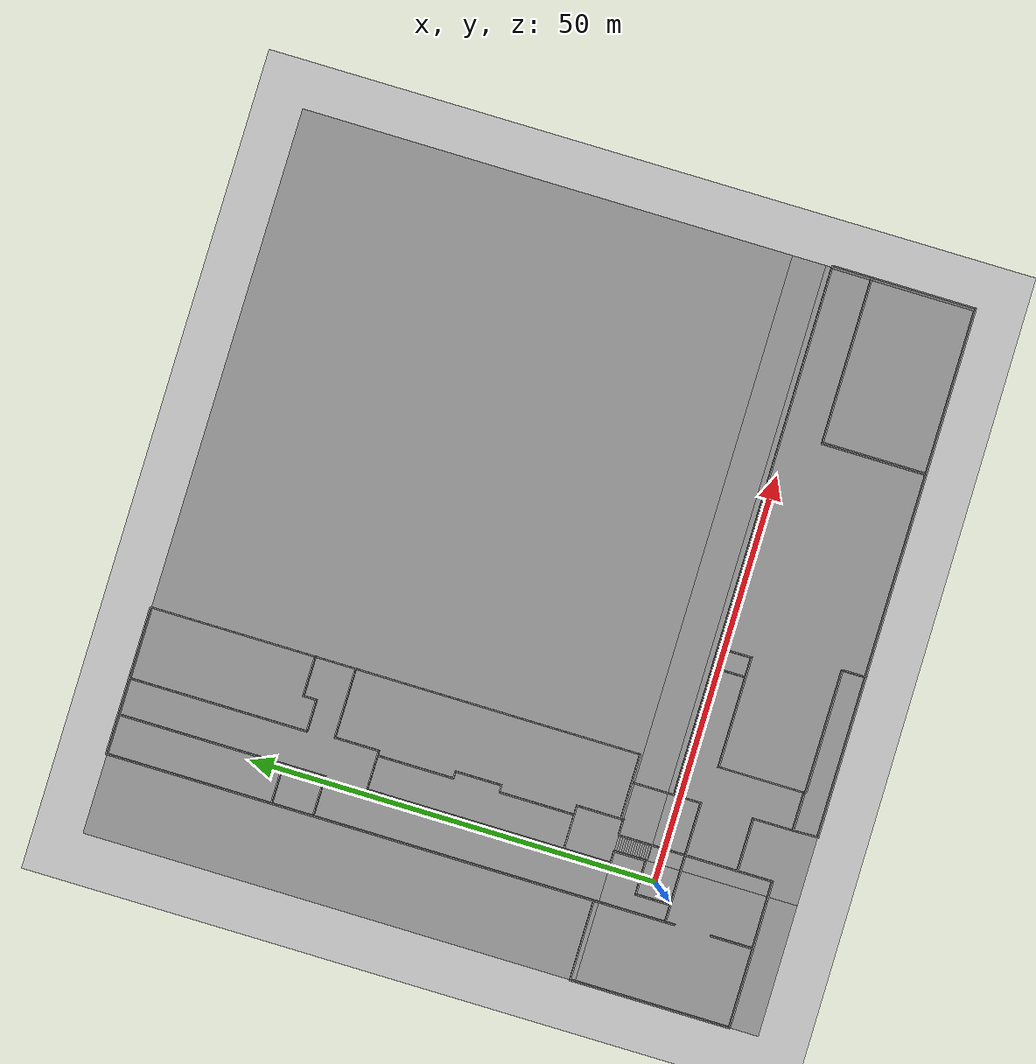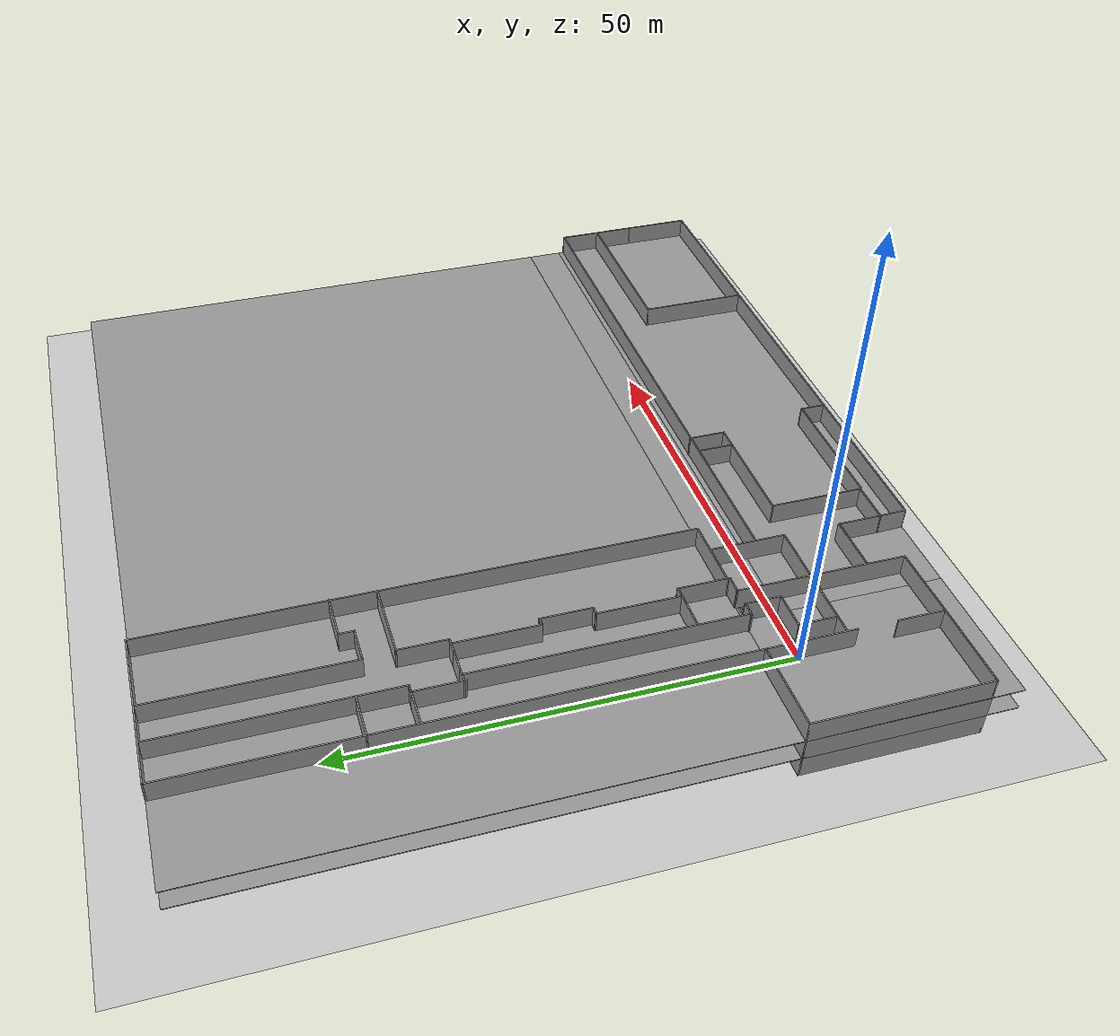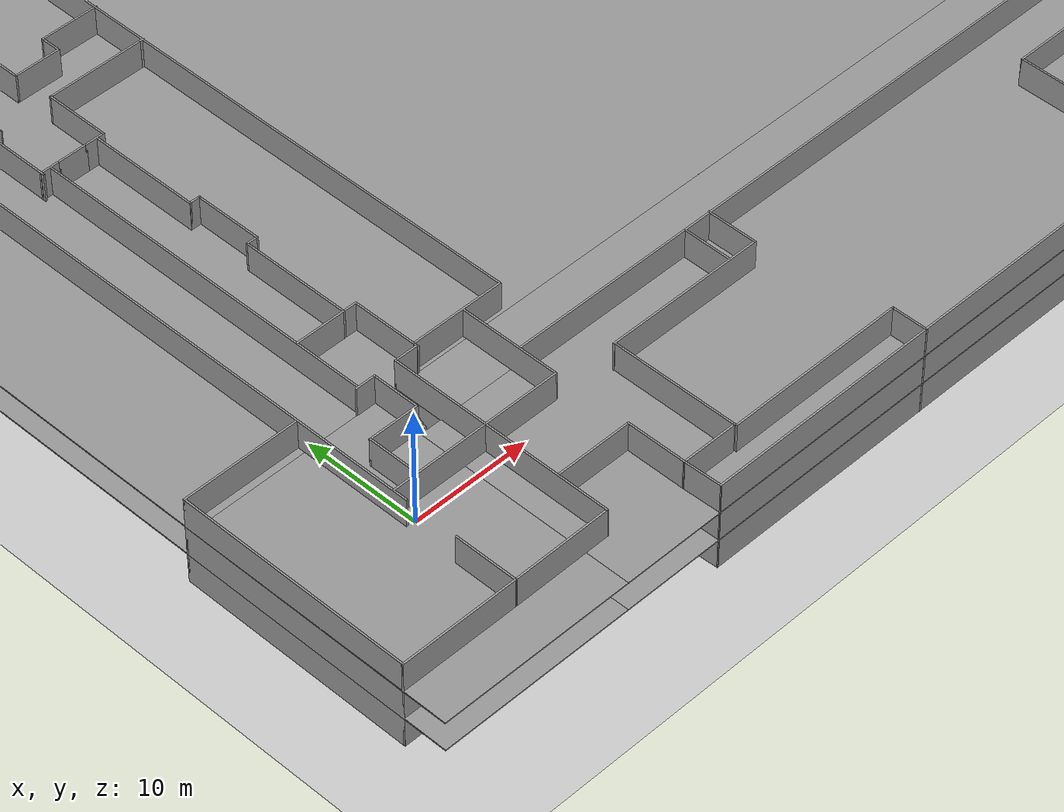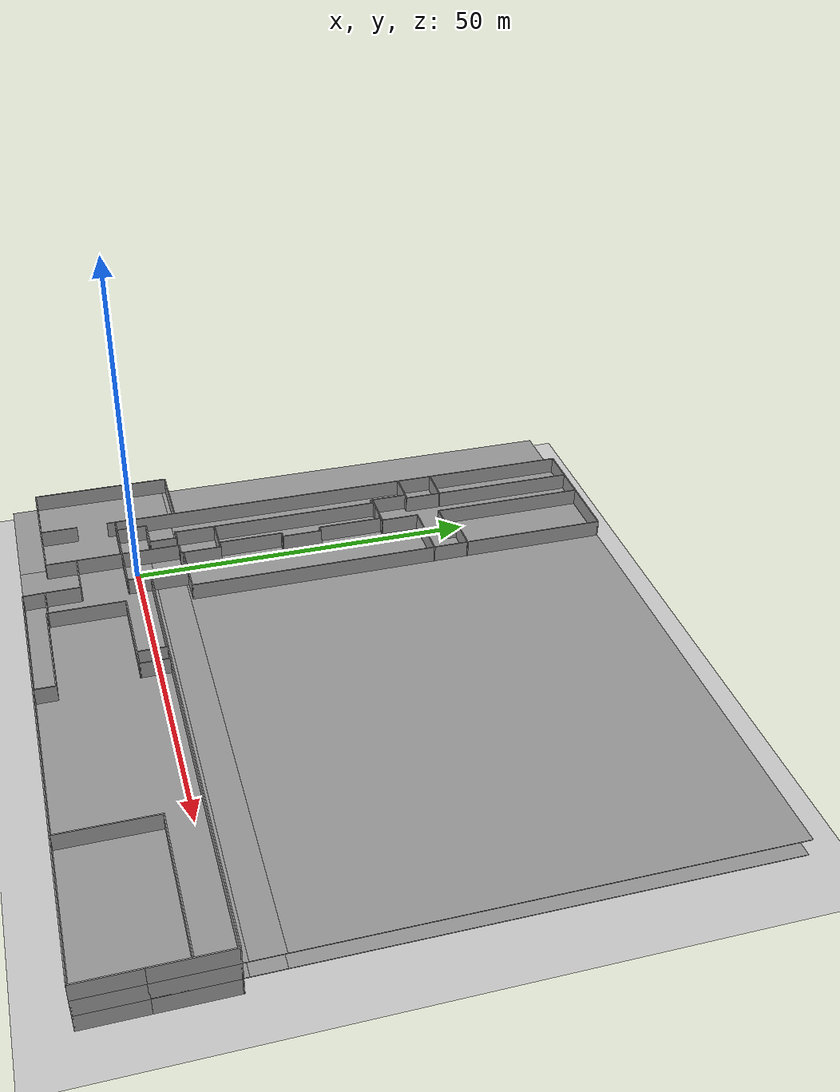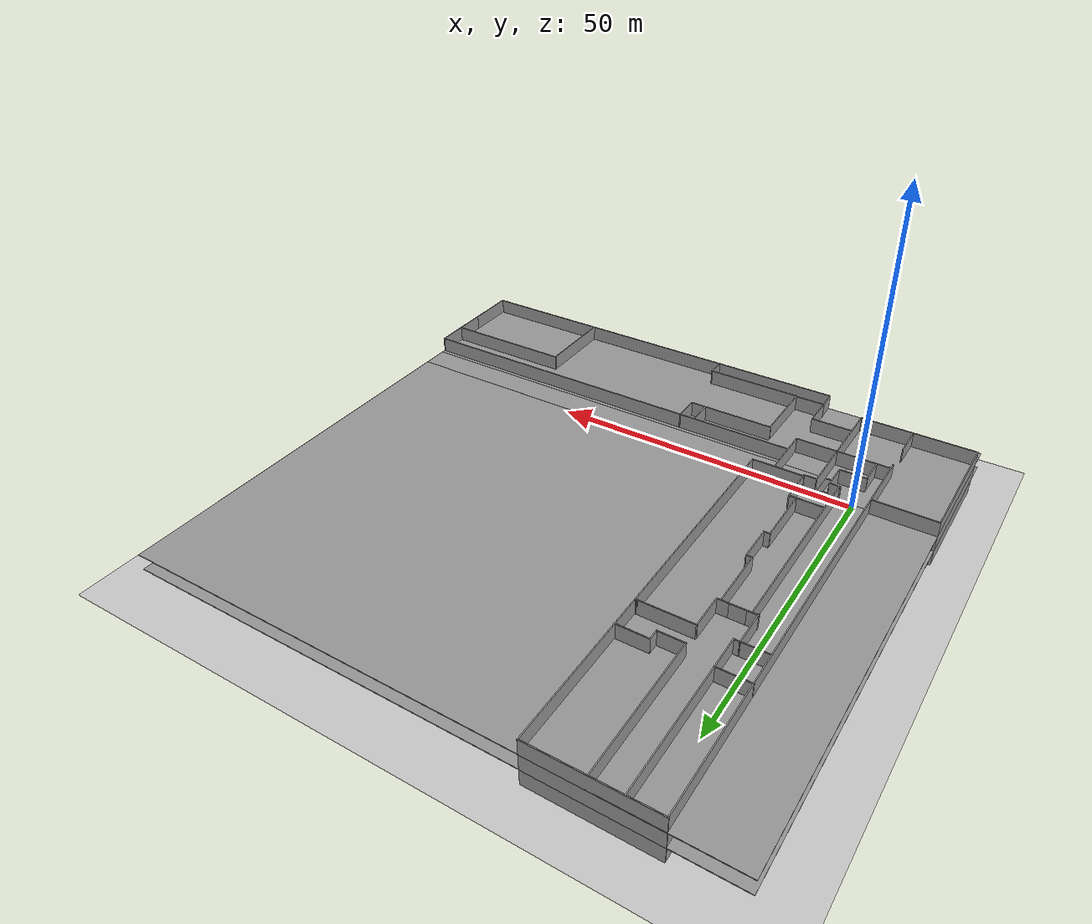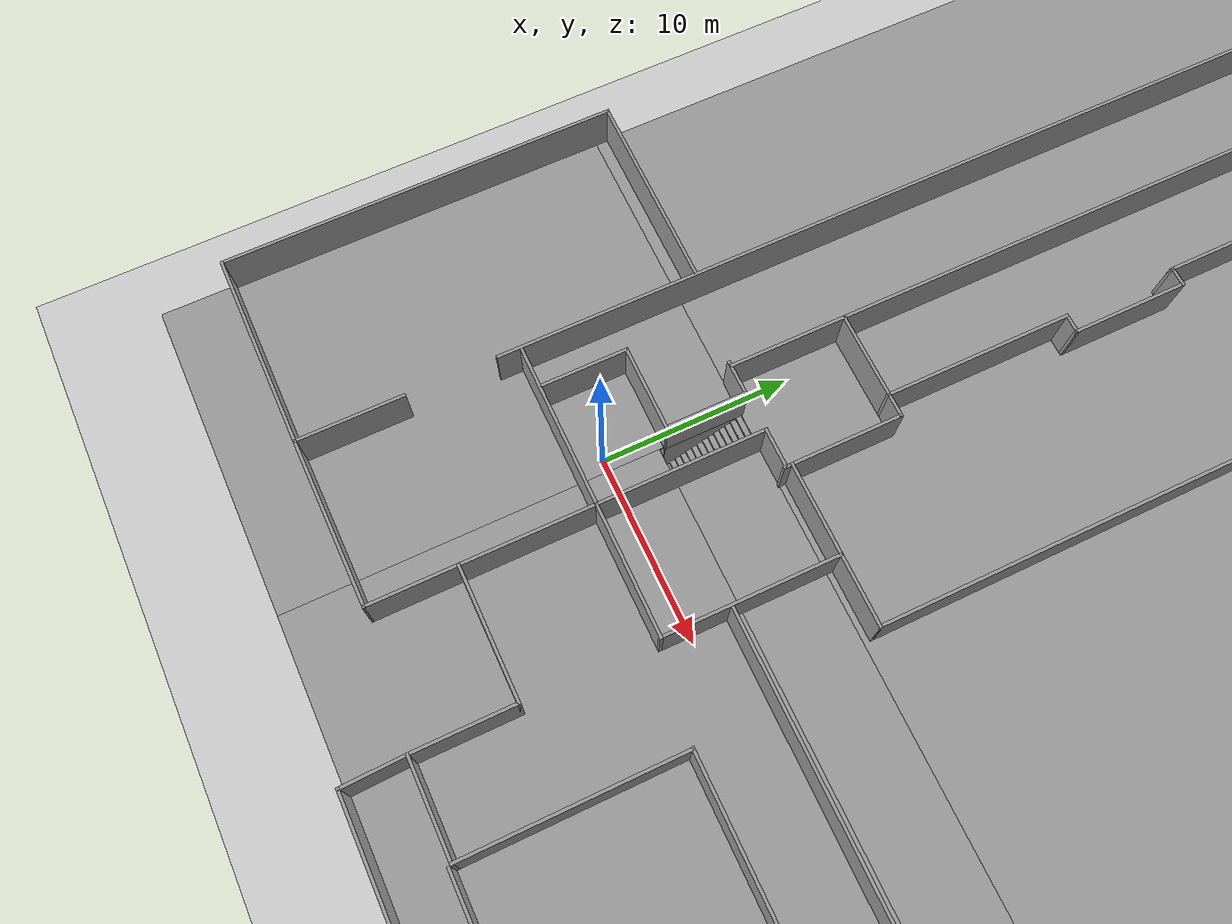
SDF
<sdf version="1.7">
 <world name="default">
  <light name="sun" type="directional">
   <pose>0 0 10 0 -0 0</pose>
   <diffuse>0.8 0.8 0.8 1</diffuse>
   <specular>0.2 0.2 0.2 1</specular>
   <attenuation>
    <range>1000</range>
    <constant>0.9</constant>
    <linear>0.01</linear>
    <quadratic>0.001</quadratic>
   </attenuation>
   <direction>-0.5 0.1 -0.9</direction>
   <spot><inner_angle>0</inner_angle><outer_angle>0</outer_angle><falloff>0</falloff></spot>
  </light>
  <model name="ground_plane">
   <pose>30 30 0 0 -0 0</pose>
   <static>1</static>
   <link name="link">
    <collision name="collision">
     <geometry><plane><normal>0 0 1</normal><size>100 100</size></plane></geometry>
     <surface><friction><ode><mu>100</mu><mu2>50</mu2></ode></friction></surface>
    </collision>
    <visual name="visual">
     <cast_shadows>0</cast_shadows>
     <geometry><plane><normal>0 0 1</normal><size>100 100</size></plane></geometry>
     <material>
      <script><uri>file://media/materials/scripts/gazebo.material</uri><name>Gazebo/Grey</name></script>
     </material>
    </visual>
   </link>
  </model>
  <gravity>0 0 -9.8</gravity>
  <magnetic_field>6e-06 2.3e-05 -4.2e-05</magnetic_field>
  <atmosphere type="adiabatic"/>
  <physics type="ode">
   <max_step_size>0.001</max_step_size>
   <real_time_factor>1</real_time_factor>
   <real_time_update_rate>1000</real_time_update_rate>
  </physics>
  <scene><ambient>0.4 0.4 0.4 1</ambient><background>0.7 0.7 0.7 1</background><shadows>1</shadows></scene>
  <spherical_coordinates>
   <surface_model>EARTH_WGS84</surface_model>
   <latitude_deg>0</latitude_deg>
   <longitude_deg>0</longitude_deg>
   <elevation>0</elevation>
   <heading_deg>0</heading_deg>
  </spherical_coordinates>
  <model name="Soterrani_AT">
   <pose>30.7763 24.7178 0 0 0 -1.57187</pose>
   <link name="Floor_1">
    <pose>2e-06 -1e-06 2.5 0 -0 0</pose>
    <visual name="Floor_1_Visual_0">
     <pose>-11.1669 0 0.05 0 -0 0</pose>
     <geometry><box><size>60.0186 88.6934 0.1</size></box></geometry>
     <material>
      <script><uri>file://media/materials/scripts/gazebo.material</uri><name>Gazebo/Grey</name></script>
      <ambient>1 1 1 1</ambient>
     </material>
     <meta><layer>1</layer></meta>
    </visual>
    <collision name="Floor_1_Collision_0">
     <geometry><box><size>60.0186 88.6934 0.1</size></box></geometry>
     <pose>-11.1669 0 0.05 0 -0 0</pose>
    </collision>
    <visual name="Floor_1_Visual_1">
     <pose>30.0093 -36.3795 0.05 0 -0 0</pose>
     <geometry><box><size>22.3339 15.9343 0.1</size></box></geometry>
     <material>
      <script><uri>file://media/materials/scripts/gazebo.material</uri><name>Gazebo/Grey</name></script>
      <ambient>1 1 1 1</ambient>
     </material>
     <meta><layer>1</layer></meta>
    </visual>
    <collision name="Floor_1_Collision_1">
     <geometry><box><size>22.3339 15.9343 0.1</size></box></geometry>
     <pose>30.0093 -36.3795 0.05 0 -0 0</pose>
    </collision>
    <visual name="Floor_1_Visual_2">
     <pose>32.0601 7.96714 0.05 0 -0 0</pose>
     <geometry><box><size>18.2324 72.7591 0.1</size></box></geometry>
     <material>
      <script><uri>file://media/materials/scripts/gazebo.material</uri><name>Gazebo/Grey</name></script>
      <ambient>1 1 1 1</ambient>
     </material>
     <meta><layer>1</layer></meta>
    </visual>
    <collision name="Floor_1_Collision_2">
     <geometry><box><size>18.2324 72.7591 0.1</size></box></geometry>
     <pose>32.0601 7.96714 0.05 0 -0 0</pose>
    </collision>
    <visual name="Floor_1_Visual_3">
     <pose>20.8931 8.88068 0.05 0 -0 0</pose>
     <geometry><box><size>4.1015 70.932 0.1</size></box></geometry>
     <material>
      <script><uri>file://media/materials/scripts/gazebo.material</uri><name>Gazebo/Grey</name></script>
      <ambient>1 1 1 1</ambient>
     </material>
     <meta><layer>1</layer></meta>
    </visual>
    <collision name="Floor_1_Collision_3">
     <geometry><box><size>4.1015 70.932 0.1</size></box></geometry>
     <pose>20.8931 8.88068 0.05 0 -0 0</pose>
    </collision>
   </link>
   <link name="Floor_2">
    <pose>2e-06 -1e-06 5 0 -0 0</pose>
    <visual name="Floor_2_Visual_0">
     <pose>-11.1613 0 0.05 0 -0 0</pose>
     <geometry><box><size>60.03 88.6934 0.1</size></box></geometry>
     <material>
      <script><uri>file://media/materials/scripts/gazebo.material</uri><name>Gazebo/Grey</name></script>
      <ambient>1 1 1 1</ambient>
     </material>
     <meta><layer>2</layer></meta>
    </visual>
    <collision name="Floor_2_Collision_0">
     <geometry><box><size>60.03 88.6934 0.1</size></box></geometry>
     <pose>-11.1613 0 0.05 0 -0 0</pose>
    </collision>
    <visual name="Floor_2_Visual_1">
     <pose>30.015 -36.4004 0.05 0 -0 0</pose>
     <geometry><box><size>22.3226 15.8926 0.1</size></box></geometry>
     <material>
      <script><uri>file://media/materials/scripts/gazebo.material</uri><name>Gazebo/Grey</name></script>
      <ambient>1 1 1 1</ambient>
     </material>
     <meta><layer>2</layer></meta>
    </visual>
    <collision name="Floor_2_Collision_1">
     <geometry><box><size>22.3226 15.8926 0.1</size></box></geometry>
     <pose>30.015 -36.4004 0.05 0 -0 0</pose>
    </collision>
    <visual name="Floor_2_Visual_2">
     <pose>32.059 7.94632 0.05 0 -0 0</pose>
     <geometry><box><size>18.2346 72.8007 0.1</size></box></geometry>
     <material>
      <script><uri>file://media/materials/scripts/gazebo.material</uri><name>Gazebo/Grey</name></script>
      <ambient>1 1 1 1</ambient>
     </material>
     <meta><layer>2</layer></meta>
    </visual>
    <collision name="Floor_2_Collision_2">
     <geometry><box><size>18.2346 72.8007 0.1</size></box></geometry>
     <pose>32.059 7.94632 0.05 0 -0 0</pose>
    </collision>
    <visual name="Floor_2_Visual_3">
     <pose>20.8977 8.87865 0.05 0 -0 0</pose>
     <geometry><box><size>4.08797 70.9361 0.1</size></box></geometry>
     <material>
      <script><uri>file://media/materials/scripts/gazebo.material</uri><name>Gazebo/Grey</name></script>
      <ambient>1 1 1 1</ambient>
     </material>
     <meta><layer>2</layer></meta>
    </visual>
    <collision name="Floor_2_Collision_3">
     <geometry><box><size>4.08797 70.9361 0.1</size></box></geometry>
     <pose>20.8977 8.87865 0.05 0 -0 0</pose>
    </collision>
   </link>
   <link name="Stairs_1">
    <visual name="Stairs_1_Visual_0">
     <pose>22.8072 -27.4989 0.083333 0 -0 -1.5708</pose>
     <geometry><box><size>1.82706 0.273433 0.166667</size></box></geometry>
     <material>
      <script><uri>file://media/materials/scripts/gazebo.material</uri><name>Gazebo/Grey</name></script>
      <ambient>1 1 1 1</ambient>
     </material>
     <meta><layer>0</layer></meta>
    </visual>
    <collision name="Stairs_1_Collision_0">
     <geometry><box><size>1.82706 0.273433 0.166667</size></box></geometry>
     <pose>22.8072 -27.4989 0.083333 0 -0 -1.5708</pose>
    </collision>
    <visual name="Stairs_1_Visual_1">
     <pose>22.5337 -27.4989 0.25 0 -0 -1.5708</pose>
     <geometry><box><size>1.82706 0.273433 0.166667</size></box></geometry>
     <material>
      <script><uri>file://media/materials/scripts/gazebo.material</uri><name>Gazebo/Grey</name></script>
      <ambient>1 1 1 1</ambient>
     </material>
     <meta><layer>0</layer></meta>
    </visual>
    <collision name="Stairs_1_Collision_1">
     <geometry><box><size>1.82706 0.273433 0.166667</size></box></geometry>
     <pose>22.5337 -27.4989 0.25 0 -0 -1.5708</pose>
    </collision>
    <visual name="Stairs_1_Visual_2">
     <pose>22.2603 -27.4989 0.416667 0 -0 -1.5708</pose>
     <geometry><box><size>1.82706 0.273433 0.166667</size></box></geometry>
     <material>
      <script><uri>file://media/materials/scripts/gazebo.material</uri><name>Gazebo/Grey</name></script>
      <ambient>1 1 1 1</ambient>
     </material>
     <meta><layer>0</layer></meta>
    </visual>
    <collision name="Stairs_1_Collision_2">
     <geometry><box><size>1.82706 0.273433 0.166667</size></box></geometry>
     <pose>22.2603 -27.4989 0.416667 0 -0 -1.5708</pose>
    </collision>
    <visual name="Stairs_1_Visual_3">
     <pose>21.9869 -27.4989 0.583333 0 -0 -1.5708</pose>
     <geometry><box><size>1.82706 0.273433 0.166667</size></box></geometry>
     <material>
      <script><uri>file://media/materials/scripts/gazebo.material</uri><name>Gazebo/Grey</name></script>
      <ambient>1 1 1 1</ambient>
     </material>
     <meta><layer>0</layer></meta>
    </visual>
    <collision name="Stairs_1_Collision_3">
     <geometry><box><size>1.82706 0.273433 0.166667</size></box></geometry>
     <pose>21.9869 -27.4989 0.583333 0 -0 -1.5708</pose>
    </collision>
    <visual name="Stairs_1_Visual_4">
     <pose>21.7134 -27.4989 0.75 0 -0 -1.5708</pose>
     <geometry><box><size>1.82706 0.273433 0.166667</size></box></geometry>
     <material>
      <script><uri>file://media/materials/scripts/gazebo.material</uri><name>Gazebo/Grey</name></script>
      <ambient>1 1 1 1</ambient>
     </material>
     <meta><layer>0</layer></meta>
    </visual>
    <collision name="Stairs_1_Collision_4">
     <geometry><box><size>1.82706 0.273433 0.166667</size></box></geometry>
     <pose>21.7134 -27.4989 0.75 0 -0 -1.5708</pose>
    </collision>
    <visual name="Stairs_1_Visual_5">
     <pose>21.44 -27.4989 0.916667 0 -0 -1.5708</pose>
     <geometry><box><size>1.82706 0.273433 0.166667</size></box></geometry>
     <material>
      <script><uri>file://media/materials/scripts/gazebo.material</uri><name>Gazebo/Grey</name></script>
      <ambient>1 1 1 1</ambient>
     </material>
     <meta><layer>0</layer></meta>
    </visual>
    <collision name="Stairs_1_Collision_5">
     <geometry><box><size>1.82706 0.273433 0.166667</size></box></geometry>
     <pose>21.44 -27.4989 0.916667 0 -0 -1.5708</pose>
    </collision>
    <visual name="Stairs_1_Visual_6">
     <pose>21.1666 -27.4989 1.08333 0 -0 -1.5708</pose>
     <geometry><box><size>1.82706 0.273433 0.166667</size></box></geometry>
     <material>
      <script><uri>file://media/materials/scripts/gazebo.material</uri><name>Gazebo/Grey</name></script>
      <ambient>1 1 1 1</ambient>
     </material>
     <meta><layer>0</layer></meta>
    </visual>
    <collision name="Stairs_1_Collision_6">
     <geometry><box><size>1.82706 0.273433 0.166667</size></box></geometry>
     <pose>21.1666 -27.4989 1.08333 0 -0 -1.5708</pose>
    </collision>
    <visual name="Stairs_1_Visual_7">
     <pose>20.8931 -27.4989 1.25 0 -0 -1.5708</pose>
     <geometry><box><size>1.82706 0.273433 0.166667</size></box></geometry>
     <material>
      <script><uri>file://media/materials/scripts/gazebo.material</uri><name>Gazebo/Grey</name></script>
      <ambient>1 1 1 1</ambient>
     </material>
     <meta><layer>0</layer></meta>
    </visual>
    <collision name="Stairs_1_Collision_7">
     <geometry><box><size>1.82706 0.273433 0.166667</size></box></geometry>
     <pose>20.8931 -27.4989 1.25 0 -0 -1.5708</pose>
    </collision>
    <visual name="Stairs_1_Visual_8">
     <pose>20.6197 -27.4989 1.41667 0 -0 -1.5708</pose>
     <geometry><box><size>1.82706 0.273433 0.166667</size></box></geometry>
     <material>
      <script><uri>file://media/materials/scripts/gazebo.material</uri><name>Gazebo/Grey</name></script>
      <ambient>1 1 1 1</ambient>
     </material>
     <meta><layer>0</layer></meta>
    </visual>
    <collision name="Stairs_1_Collision_8">
     <geometry><box><size>1.82706 0.273433 0.166667</size></box></geometry>
     <pose>20.6197 -27.4989 1.41667 0 -0 -1.5708</pose>
    </collision>
    <visual name="Stairs_1_Visual_9">
     <pose>20.3463 -27.4989 1.58333 0 -0 -1.5708</pose>
     <geometry><box><size>1.82706 0.273433 0.166667</size></box></geometry>
     <material>
      <script><uri>file://media/materials/scripts/gazebo.material</uri><name>Gazebo/Grey</name></script>
      <ambient>1 1 1 1</ambient>
     </material>
     <meta><layer>0</layer></meta>
    </visual>
    <collision name="Stairs_1_Collision_9">
     <geometry><box><size>1.82706 0.273433 0.166667</size></box></geometry>
     <pose>20.3463 -27.4989 1.58333 0 -0 -1.5708</pose>
    </collision>
    <visual name="Stairs_1_Visual_10">
     <pose>20.0728 -27.4989 1.75 0 -0 -1.5708</pose>
     <geometry><box><size>1.82706 0.273433 0.166667</size></box></geometry>
     <material>
      <script><uri>file://media/materials/scripts/gazebo.material</uri><name>Gazebo/Grey</name></script>
      <ambient>1 1 1 1</ambient>
     </material>
     <meta><layer>0</layer></meta>
    </visual>
    <collision name="Stairs_1_Collision_10">
     <geometry><box><size>1.82706 0.273433 0.166667</size></box></geometry>
     <pose>20.0728 -27.4989 1.75 0 -0 -1.5708</pose>
    </collision>
    <visual name="Stairs_1_Visual_11">
     <pose>19.7994 -27.4989 1.91667 0 -0 -1.5708</pose>
     <geometry><box><size>1.82706 0.273433 0.166667</size></box></geometry>
     <material>
      <script><uri>file://media/materials/scripts/gazebo.material</uri><name>Gazebo/Grey</name></script>
      <ambient>1 1 1 1</ambient>
     </material>
     <meta><layer>0</layer></meta>
    </visual>
    <collision name="Stairs_1_Collision_11">
     <geometry><box><size>1.82706 0.273433 0.166667</size></box></geometry>
     <pose>19.7994 -27.4989 1.91667 0 -0 -1.5708</pose>
    </collision>
    <visual name="Stairs_1_Visual_12">
     <pose>19.526 -27.4989 2.08333 0 -0 -1.5708</pose>
     <geometry><box><size>1.82706 0.273433 0.166667</size></box></geometry>
     <material>
      <script><uri>file://media/materials/scripts/gazebo.material</uri><name>Gazebo/Grey</name></script>
      <ambient>1 1 1 1</ambient>
     </material>
     <meta><layer>0</layer></meta>
    </visual>
    <collision name="Stairs_1_Collision_12">
     <geometry><box><size>1.82706 0.273433 0.166667</size></box></geometry>
     <pose>19.526 -27.4989 2.08333 0 -0 -1.5708</pose>
    </collision>
    <visual name="Stairs_1_Visual_13">
     <pose>19.2525 -27.4989 2.25 0 -0 -1.5708</pose>
     <geometry><box><size>1.82706 0.273433 0.166667</size></box></geometry>
     <material>
      <script><uri>file://media/materials/scripts/gazebo.material</uri><name>Gazebo/Grey</name></script>
      <ambient>1 1 1 1</ambient>
     </material>
     <meta><layer>0</layer></meta>
    </visual>
    <collision name="Stairs_1_Collision_13">
     <geometry><box><size>1.82706 0.273433 0.166667</size></box></geometry>
     <pose>19.2525 -27.4989 2.25 0 -0 -1.5708</pose>
    </collision>
    <visual name="Stairs_1_Visual_14">
     <pose>18.9791 -27.4989 2.41667 0 -0 -1.5708</pose>
     <geometry><box><size>1.82706 0.273433 0.166667</size></box></geometry>
     <material>
      <script><uri>file://media/materials/scripts/gazebo.material</uri><name>Gazebo/Grey</name></script>
      <ambient>1 1 1 1</ambient>
     </material>
     <meta><layer>0</layer></meta>
    </visual>
    <collision name="Stairs_1_Collision_14">
     <geometry><box><size>1.82706 0.273433 0.166667</size></box></geometry>
     <pose>18.9791 -27.4989 2.41667 0 -0 -1.5708</pose>
    </collision>
   </link>
   <link name="Stairs_2">
    <visual name="Stairs_2_Visual_0">
     <pose>22.8054 -27.5217 2.58333 0 -0 -1.5708</pose>
     <geometry><box><size>1.86465 0.272531 0.166667</size></box></geometry>
     <material>
      <script><uri>file://media/materials/scripts/gazebo.material</uri><name>Gazebo/Grey</name></script>
      <ambient>1 1 1 1</ambient>
     </material>
     <meta><layer>1</layer></meta>
    </visual>
    <collision name="Stairs_2_Collision_0">
     <geometry><box><size>1.86465 0.272531 0.166667</size></box></geometry>
     <pose>22.8054 -27.5217 2.58333 0 -0 -1.5708</pose>
    </collision>
    <visual name="Stairs_2_Visual_1">
     <pose>22.5329 -27.5217 2.75 0 -0 -1.5708</pose>
     <geometry><box><size>1.86465 0.272531 0.166667</size></box></geometry>
     <material>
      <script><uri>file://media/materials/scripts/gazebo.material</uri><name>Gazebo/Grey</name></script>
      <ambient>1 1 1 1</ambient>
     </material>
     <meta><layer>1</layer></meta>
    </visual>
    <collision name="Stairs_2_Collision_1">
     <geometry><box><size>1.86465 0.272531 0.166667</size></box></geometry>
     <pose>22.5329 -27.5217 2.75 0 -0 -1.5708</pose>
    </collision>
    <visual name="Stairs_2_Visual_2">
     <pose>22.2603 -27.5217 2.91667 0 -0 -1.5708</pose>
     <geometry><box><size>1.86465 0.272531 0.166667</size></box></geometry>
     <material>
      <script><uri>file://media/materials/scripts/gazebo.material</uri><name>Gazebo/Grey</name></script>
      <ambient>1 1 1 1</ambient>
     </material>
     <meta><layer>1</layer></meta>
    </visual>
    <collision name="Stairs_2_Collision_2">
     <geometry><box><size>1.86465 0.272531 0.166667</size></box></geometry>
     <pose>22.2603 -27.5217 2.91667 0 -0 -1.5708</pose>
    </collision>
    <visual name="Stairs_2_Visual_3">
     <pose>21.9878 -27.5217 3.08333 0 -0 -1.5708</pose>
     <geometry><box><size>1.86465 0.272531 0.166667</size></box></geometry>
     <material>
      <script><uri>file://media/materials/scripts/gazebo.material</uri><name>Gazebo/Grey</name></script>
      <ambient>1 1 1 1</ambient>
     </material>
     <meta><layer>1</layer></meta>
    </visual>
    <collision name="Stairs_2_Collision_3">
     <geometry><box><size>1.86465 0.272531 0.166667</size></box></geometry>
     <pose>21.9878 -27.5217 3.08333 0 -0 -1.5708</pose>
    </collision>
    <visual name="Stairs_2_Visual_4">
     <pose>21.7153 -27.5217 3.25 0 -0 -1.5708</pose>
     <geometry><box><size>1.86465 0.272531 0.166667</size></box></geometry>
     <material>
      <script><uri>file://media/materials/scripts/gazebo.material</uri><name>Gazebo/Grey</name></script>
      <ambient>1 1 1 1</ambient>
     </material>
     <meta><layer>1</layer></meta>
    </visual>
    <collision name="Stairs_2_Collision_4">
     <geometry><box><size>1.86465 0.272531 0.166667</size></box></geometry>
     <pose>21.7153 -27.5217 3.25 0 -0 -1.5708</pose>
    </collision>
    <visual name="Stairs_2_Visual_5">
     <pose>21.4427 -27.5217 3.41667 0 -0 -1.5708</pose>
     <geometry><box><size>1.86465 0.272531 0.166667</size></box></geometry>
     <material>
      <script><uri>file://media/materials/scripts/gazebo.material</uri><name>Gazebo/Grey</name></script>
      <ambient>1 1 1 1</ambient>
     </material>
     <meta><layer>1</layer></meta>
    </visual>
    <collision name="Stairs_2_Collision_5">
     <geometry><box><size>1.86465 0.272531 0.166667</size></box></geometry>
     <pose>21.4427 -27.5217 3.41667 0 -0 -1.5708</pose>
    </collision>
    <visual name="Stairs_2_Visual_6">
     <pose>21.1702 -27.5217 3.58333 0 -0 -1.5708</pose>
     <geometry><box><size>1.86465 0.272531 0.166667</size></box></geometry>
     <material>
      <script><uri>file://media/materials/scripts/gazebo.material</uri><name>Gazebo/Grey</name></script>
      <ambient>1 1 1 1</ambient>
     </material>
     <meta><layer>1</layer></meta>
    </visual>
    <collision name="Stairs_2_Collision_6">
     <geometry><box><size>1.86465 0.272531 0.166667</size></box></geometry>
     <pose>21.1702 -27.5217 3.58333 0 -0 -1.5708</pose>
    </collision>
    <visual name="Stairs_2_Visual_7">
     <pose>20.8977 -27.5217 3.75 0 -0 -1.5708</pose>
     <geometry><box><size>1.86465 0.272531 0.166667</size></box></geometry>
     <material>
      <script><uri>file://media/materials/scripts/gazebo.material</uri><name>Gazebo/Grey</name></script>
      <ambient>1 1 1 1</ambient>
     </material>
     <meta><layer>1</layer></meta>
    </visual>
    <collision name="Stairs_2_Collision_7">
     <geometry><box><size>1.86465 0.272531 0.166667</size></box></geometry>
     <pose>20.8977 -27.5217 3.75 0 -0 -1.5708</pose>
    </collision>
    <visual name="Stairs_2_Visual_8">
     <pose>20.6251 -27.5217 3.91667 0 -0 -1.5708</pose>
     <geometry><box><size>1.86465 0.272531 0.166667</size></box></geometry>
     <material>
      <script><uri>file://media/materials/scripts/gazebo.material</uri><name>Gazebo/Grey</name></script>
      <ambient>1 1 1 1</ambient>
     </material>
     <meta><layer>1</layer></meta>
    </visual>
    <collision name="Stairs_2_Collision_8">
     <geometry><box><size>1.86465 0.272531 0.166667</size></box></geometry>
     <pose>20.6251 -27.5217 3.91667 0 -0 -1.5708</pose>
    </collision>
    <visual name="Stairs_2_Visual_9">
     <pose>20.3526 -27.5217 4.08333 0 -0 -1.5708</pose>
     <geometry><box><size>1.86465 0.272531 0.166667</size></box></geometry>
     <material>
      <script><uri>file://media/materials/scripts/gazebo.material</uri><name>Gazebo/Grey</name></script>
      <ambient>1 1 1 1</ambient>
     </material>
     <meta><layer>1</layer></meta>
    </visual>
    <collision name="Stairs_2_Collision_9">
     <geometry><box><size>1.86465 0.272531 0.166667</size></box></geometry>
     <pose>20.3526 -27.5217 4.08333 0 -0 -1.5708</pose>
    </collision>
    <visual name="Stairs_2_Visual_10">
     <pose>20.0801 -27.5217 4.25 0 -0 -1.5708</pose>
     <geometry><box><size>1.86465 0.272531 0.166667</size></box></geometry>
     <material>
      <script><uri>file://media/materials/scripts/gazebo.material</uri><name>Gazebo/Grey</name></script>
      <ambient>1 1 1 1</ambient>
     </material>
     <meta><layer>1</layer></meta>
    </visual>
    <collision name="Stairs_2_Collision_10">
     <geometry><box><size>1.86465 0.272531 0.166667</size></box></geometry>
     <pose>20.0801 -27.5217 4.25 0 -0 -1.5708</pose>
    </collision>
    <visual name="Stairs_2_Visual_11">
     <pose>19.8076 -27.5217 4.41667 0 -0 -1.5708</pose>
     <geometry><box><size>1.86465 0.272531 0.166667</size></box></geometry>
     <material>
      <script><uri>file://media/materials/scripts/gazebo.material</uri><name>Gazebo/Grey</name></script>
      <ambient>1 1 1 1</ambient>
     </material>
     <meta><layer>1</layer></meta>
    </visual>
    <collision name="Stairs_2_Collision_11">
     <geometry><box><size>1.86465 0.272531 0.166667</size></box></geometry>
     <pose>19.8076 -27.5217 4.41667 0 -0 -1.5708</pose>
    </collision>
    <visual name="Stairs_2_Visual_12">
     <pose>19.535 -27.5217 4.58333 0 -0 -1.5708</pose>
     <geometry><box><size>1.86465 0.272531 0.166667</size></box></geometry>
     <material>
      <script><uri>file://media/materials/scripts/gazebo.material</uri><name>Gazebo/Grey</name></script>
      <ambient>1 1 1 1</ambient>
     </material>
     <meta><layer>1</layer></meta>
    </visual>
    <collision name="Stairs_2_Collision_12">
     <geometry><box><size>1.86465 0.272531 0.166667</size></box></geometry>
     <pose>19.535 -27.5217 4.58333 0 -0 -1.5708</pose>
    </collision>
    <visual name="Stairs_2_Visual_13">
     <pose>19.2625 -27.5217 4.75 0 -0 -1.5708</pose>
     <geometry><box><size>1.86465 0.272531 0.166667</size></box></geometry>
     <material>
      <script><uri>file://media/materials/scripts/gazebo.material</uri><name>Gazebo/Grey</name></script>
      <ambient>1 1 1 1</ambient>
     </material>
     <meta><layer>1</layer></meta>
    </visual>
    <collision name="Stairs_2_Collision_13">
     <geometry><box><size>1.86465 0.272531 0.166667</size></box></geometry>
     <pose>19.2625 -27.5217 4.75 0 -0 -1.5708</pose>
    </collision>
    <visual name="Stairs_2_Visual_14">
     <pose>18.99 -27.5217 4.91667 0 -0 -1.5708</pose>
     <geometry><box><size>1.86465 0.272531 0.166667</size></box></geometry>
     <material>
      <script><uri>file://media/materials/scripts/gazebo.material</uri><name>Gazebo/Grey</name></script>
      <ambient>1 1 1 1</ambient>
     </material>
     <meta><layer>1</layer></meta>
    </visual>
    <collision name="Stairs_2_Collision_14">
     <geometry><box><size>1.86465 0.272531 0.166667</size></box></geometry>
     <pose>18.99 -27.5217 4.91667 0 -0 -1.5708</pose>
    </collision>
   </link>
   <link name="Wall_1">
    <collision name="Wall_1_Collision">
     <geometry><box><size>69.25 0.15 2.5</size></box></geometry>
     <pose>0 0 1.25 0 -0 0</pose>
    </collision>
    <visual name="Wall_1_Visual">
     <pose>0 0 1.25 0 -0 0</pose>
     <geometry><box><size>69.25 0.15 2.5</size></box></geometry>
     <material>
      <script><uri>file://media/materials/scripts/gazebo.material</uri><name>Gazebo/Grey</name></script>
      <ambient>1 1 1 1</ambient>
     </material>
     <meta><layer>0</layer></meta>
    </visual>
    <pose>-6.55126 -34.6495 0 0 -0 3.14159</pose>
   </link>
   <link name="Wall_11">
    <collision name="Wall_11_Collision">
     <geometry><box><size>1 0.15 2.5</size></box></geometry>
     <pose>0 0 1.25 0 -0 0</pose>
    </collision>
    <visual name="Wall_11_Visual">
     <pose>0 0 1.25 0 -0 0</pose>
     <geometry><box><size>1 0.15 2.5</size></box></geometry>
     <material>
      <script><uri>file://media/materials/scripts/gazebo.material</uri><name>Gazebo/Grey</name></script>
      <ambient>1 1 1 1</ambient>
     </material>
     <meta><layer>0</layer></meta>
    </visual>
    <pose>4.04874 -25.3245 0 0 -0 1.5708</pose>
   </link>
   <link name="Wall_12">
    <collision name="Wall_12_Collision">
     <geometry><box><size>5.75 0.15 2.5</size></box></geometry>
     <pose>0 0 1.25 0 -0 0</pose>
    </collision>
    <visual name="Wall_12_Visual">
     <pose>0 0 1.25 0 -0 0</pose>
     <geometry><box><size>5.75 0.15 2.5</size></box></geometry>
     <material>
      <script><uri>file://media/materials/scripts/gazebo.material</uri><name>Gazebo/Grey</name></script>
      <ambient>1 1 1 1</ambient>
     </material>
     <meta><layer>0</layer></meta>
    </visual>
    <pose>1.24874 -24.8995 0 0 -0 3.14159</pose>
   </link>
   <link name="Wall_13">
    <collision name="Wall_13_Collision">
     <geometry><box><size>1 0.15 2.5</size></box></geometry>
     <pose>0 0 1.25 0 -0 0</pose>
    </collision>
    <visual name="Wall_13_Visual">
     <pose>0 0 1.25 0 -0 0</pose>
     <geometry><box><size>1 0.15 2.5</size></box></geometry>
     <material>
      <script><uri>file://media/materials/scripts/gazebo.material</uri><name>Gazebo/Grey</name></script>
      <ambient>1 1 1 1</ambient>
     </material>
     <meta><layer>0</layer></meta>
    </visual>
    <pose>-1.55126 -25.3245 0 0 -0 -1.5708</pose>
   </link>
   <link name="Wall_14">
    <collision name="Wall_14_Collision">
     <geometry><box><size>9.25 0.15 2.5</size></box></geometry>
     <pose>0 0 1.25 0 -0 0</pose>
    </collision>
    <visual name="Wall_14_Visual">
     <pose>0 0 1.25 0 -0 0</pose>
     <geometry><box><size>9.25 0.15 2.5</size></box></geometry>
     <material>
      <script><uri>file://media/materials/scripts/gazebo.material</uri><name>Gazebo/Grey</name></script>
      <ambient>1 1 1 1</ambient>
     </material>
     <meta><layer>0</layer></meta>
    </visual>
    <pose>-6.10126 -25.7495 0 0 -0 3.14159</pose>
   </link>
   <link name="Wall_149">
    <collision name="Wall_149_Collision">
     <geometry><box><size>69.25 0.15 2.5</size></box></geometry>
     <pose>0 0 1.25 0 -0 0</pose>
    </collision>
    <visual name="Wall_149_Visual">
     <pose>0 0 1.25 0 -0 0</pose>
     <geometry><box><size>69.25 0.15 2.5</size></box></geometry>
     <material>
      <script><uri>file://media/materials/scripts/gazebo.material</uri><name>Gazebo/Grey</name></script>
      <ambient>1 1 1 1</ambient>
     </material>
     <meta><layer>1</layer></meta>
    </visual>
    <pose>-6.55126 -34.6495 2.5 0 -0 3.14159</pose>
   </link>
   <link name="Wall_150">
    <collision name="Wall_150_Collision">
     <geometry><box><size>18 0.15 2.5</size></box></geometry>
     <pose>0 0 1.25 0 -0 0</pose>
    </collision>
    <visual name="Wall_150_Visual">
     <pose>0 0 1.25 0 -0 0</pose>
     <geometry><box><size>18 0.15 2.5</size></box></geometry>
     <material>
      <script><uri>file://media/materials/scripts/gazebo.material</uri><name>Gazebo/Grey</name></script>
      <ambient>1 1 1 1</ambient>
     </material>
     <meta><layer>1</layer></meta>
    </visual>
    <pose>-41.1013 -25.7245 2.5 0 -0 1.5708</pose>
   </link>
   <link name="Wall_151">
    <collision name="Wall_151_Collision">
     <geometry><box><size>59.75 0.15 2.5</size></box></geometry>
     <pose>0 0 1.25 0 -0 0</pose>
    </collision>
    <visual name="Wall_151_Visual">
     <pose>0 0 1.25 0 -0 0</pose>
     <geometry><box><size>59.75 0.15 2.5</size></box></geometry>
     <material>
      <script><uri>file://media/materials/scripts/gazebo.material</uri><name>Gazebo/Grey</name></script>
      <ambient>1 1 1 1</ambient>
     </material>
     <meta><layer>1</layer></meta>
    </visual>
    <pose>-11.3013 -16.7995 2.5 0 -0 0</pose>
   </link>
   <link name="Wall_152">
    <collision name="Wall_152_Collision">
     <geometry><box><size>8 0.15 2.5</size></box></geometry>
     <pose>0 0 1.25 0 -0 0</pose>
    </collision>
    <visual name="Wall_152_Visual">
     <pose>0 0 1.25 0 -0 0</pose>
     <geometry><box><size>8 0.15 2.5</size></box></geometry>
     <material>
      <script><uri>file://media/materials/scripts/gazebo.material</uri><name>Gazebo/Grey</name></script>
      <ambient>1 1 1 1</ambient>
     </material>
     <meta><layer>1</layer></meta>
    </visual>
    <pose>18.4987 -20.7245 2.5 0 -0 -1.5708</pose>
   </link>
   <link name="Wall_153">
    <collision name="Wall_153_Collision">
     <geometry><box><size>5.5 0.15 2.5</size></box></geometry>
     <pose>0 0 1.25 0 -0 0</pose>
    </collision>
    <visual name="Wall_153_Visual">
     <pose>0 0 1.25 0 -0 0</pose>
     <geometry><box><size>5.5 0.15 2.5</size></box></geometry>
     <material>
      <script><uri>file://media/materials/scripts/gazebo.material</uri><name>Gazebo/Grey</name></script>
      <ambient>1 1 1 1</ambient>
     </material>
     <meta><layer>1</layer></meta>
    </visual>
    <pose>15.8237 -24.6495 2.5 0 -0 3.14159</pose>
   </link>
   <link name="Wall_154">
    <collision name="Wall_154_Collision">
     <geometry><box><size>1.25 0.15 2.5</size></box></geometry>
     <pose>0 0 1.25 0 -0 0</pose>
    </collision>
    <visual name="Wall_154_Visual">
     <pose>0 0 1.25 0 -0 0</pose>
     <geometry><box><size>1.25 0.15 2.5</size></box></geometry>
     <material>
      <script><uri>file://media/materials/scripts/gazebo.material</uri><name>Gazebo/Grey</name></script>
      <ambient>1 1 1 1</ambient>
     </material>
     <meta><layer>1</layer></meta>
    </visual>
    <pose>13.1487 -25.1995 2.5 0 -0 -1.5708</pose>
   </link>
   <link name="Wall_155">
    <collision name="Wall_155_Collision">
     <geometry><box><size>9.25 0.15 2.5</size></box></geometry>
     <pose>0 0 1.25 0 -0 0</pose>
    </collision>
    <visual name="Wall_155_Visual">
     <pose>0 0 1.25 0 -0 0</pose>
     <geometry><box><size>9.25 0.15 2.5</size></box></geometry>
     <material>
      <script><uri>file://media/materials/scripts/gazebo.material</uri><name>Gazebo/Grey</name></script>
      <ambient>1 1 1 1</ambient>
     </material>
     <meta><layer>1</layer></meta>
    </visual>
    <pose>8.59874 -25.7495 2.5 0 -0 3.14159</pose>
   </link>
   <link name="Wall_156">
    <collision name="Wall_156_Collision">
     <geometry><box><size>1 0.15 2.5</size></box></geometry>
     <pose>0 0 1.25 0 -0 0</pose>
    </collision>
    <visual name="Wall_156_Visual">
     <pose>0 0 1.25 0 -0 0</pose>
     <geometry><box><size>1 0.15 2.5</size></box></geometry>
     <material>
      <script><uri>file://media/materials/scripts/gazebo.material</uri><name>Gazebo/Grey</name></script>
      <ambient>1 1 1 1</ambient>
     </material>
     <meta><layer>1</layer></meta>
    </visual>
    <pose>4.04874 -25.3245 2.5 0 -0 1.5708</pose>
   </link>
   <link name="Wall_157">
    <collision name="Wall_157_Collision">
     <geometry><box><size>5.75 0.15 2.5</size></box></geometry>
     <pose>0 0 1.25 0 -0 0</pose>
    </collision>
    <visual name="Wall_157_Visual">
     <pose>0 0 1.25 0 -0 0</pose>
     <geometry><box><size>5.75 0.15 2.5</size></box></geometry>
     <material>
      <script><uri>file://media/materials/scripts/gazebo.material</uri><name>Gazebo/Grey</name></script>
      <ambient>1 1 1 1</ambient>
     </material>
     <meta><layer>1</layer></meta>
    </visual>
    <pose>1.24874 -24.8995 2.5 0 -0 3.14159</pose>
   </link>
   <link name="Wall_158">
    <collision name="Wall_158_Collision">
     <geometry><box><size>1 0.15 2.5</size></box></geometry>
     <pose>0 0 1.25 0 -0 0</pose>
    </collision>
    <visual name="Wall_158_Visual">
     <pose>0 0 1.25 0 -0 0</pose>
     <geometry><box><size>1 0.15 2.5</size></box></geometry>
     <material>
      <script><uri>file://media/materials/scripts/gazebo.material</uri><name>Gazebo/Grey</name></script>
      <ambient>1 1 1 1</ambient>
     </material>
     <meta><layer>1</layer></meta>
    </visual>
    <pose>-1.55126 -25.3245 2.5 0 -0 -1.5708</pose>
   </link>
   <link name="Wall_159">
    <collision name="Wall_159_Collision">
     <geometry><box><size>9.25 0.15 2.5</size></box></geometry>
     <pose>0 0 1.25 0 -0 0</pose>
    </collision>
    <visual name="Wall_159_Visual">
     <pose>0 0 1.25 0 -0 0</pose>
     <geometry><box><size>9.25 0.15 2.5</size></box></geometry>
     <material>
      <script><uri>file://media/materials/scripts/gazebo.material</uri><name>Gazebo/Grey</name></script>
      <ambient>1 1 1 1</ambient>
     </material>
     <meta><layer>1</layer></meta>
    </visual>
    <pose>-6.10126 -25.7495 2.5 0 -0 3.14159</pose>
   </link>
   <link name="Wall_16">
    <collision name="Wall_16_Collision">
     <geometry><box><size>5.5 0.15 2.5</size></box></geometry>
     <pose>0 0 1.25 0 -0 0</pose>
    </collision>
    <visual name="Wall_16_Visual">
     <pose>0 0 1.25 0 -0 0</pose>
     <geometry><box><size>5.5 0.15 2.5</size></box></geometry>
     <material>
      <script><uri>file://media/materials/scripts/gazebo.material</uri><name>Gazebo/Grey</name></script>
      <ambient>1 1 1 1</ambient>
     </material>
     <meta><layer>0</layer></meta>
    </visual>
    <pose>-13.4816 -25.1699 0 0 -0 3.14159</pose>
   </link>
   <link name="Wall_160">
    <collision name="Wall_160_Collision">
     <geometry><box><size>5.5 0.15 2.5</size></box></geometry>
     <pose>0 0 1.25 0 -0 0</pose>
    </collision>
    <visual name="Wall_160_Visual">
     <pose>0 0 1.25 0 -0 0</pose>
     <geometry><box><size>5.5 0.15 2.5</size></box></geometry>
     <material>
      <script><uri>file://media/materials/scripts/gazebo.material</uri><name>Gazebo/Grey</name></script>
      <ambient>1 1 1 1</ambient>
     </material>
     <meta><layer>1</layer></meta>
    </visual>
    <pose>-13.4816 -25.1699 2.5 0 -0 3.14159</pose>
   </link>
   <link name="Wall_161">
    <collision name="Wall_161_Collision">
     <geometry><box><size>8.25 0.15 2.5</size></box></geometry>
     <pose>0 0 1.25 0 -0 0</pose>
    </collision>
    <visual name="Wall_161_Visual">
     <pose>0 0 1.25 0 -0 0</pose>
     <geometry><box><size>8.25 0.15 2.5</size></box></geometry>
     <material>
      <script><uri>file://media/materials/scripts/gazebo.material</uri><name>Gazebo/Grey</name></script>
      <ambient>1 1 1 1</ambient>
     </material>
     <meta><layer>1</layer></meta>
    </visual>
    <pose>-16.1566 -21.1199 2.5 0 -0 1.5708</pose>
   </link>
   <link name="Wall_162">
    <collision name="Wall_162_Collision">
     <geometry><box><size>0.464195 0.15 2.5</size></box></geometry>
     <pose>0 0 1.25 0 -0 0</pose>
    </collision>
    <visual name="Wall_162_Visual">
     <pose>0 0 1.25 0 -0 0</pose>
     <geometry><box><size>0.464195 0.15 2.5</size></box></geometry>
     <material>
      <script><uri>file://media/materials/scripts/gazebo.material</uri><name>Gazebo/Grey</name></script>
      <ambient>1 1 1 1</ambient>
     </material>
     <meta><layer>1</layer></meta>
    </visual>
    <pose>-16.1522 -16.9129 2.5 0 -0 -1.59848</pose>
   </link>
   <link name="Wall_163">
    <collision name="Wall_163_Collision">
     <geometry><box><size>5 0.15 2.5</size></box></geometry>
     <pose>0 0 1.25 0 -0 0</pose>
    </collision>
    <visual name="Wall_163_Visual">
     <pose>0 0 1.25 0 -0 0</pose>
     <geometry><box><size>5 0.15 2.5</size></box></geometry>
     <material>
      <script><uri>file://media/materials/scripts/gazebo.material</uri><name>Gazebo/Grey</name></script>
      <ambient>1 1 1 1</ambient>
     </material>
     <meta><layer>1</layer></meta>
    </visual>
    <pose>-21.0847 -19.1578 2.5 0 -0 -1.5708</pose>
   </link>
   <link name="Wall_164">
    <collision name="Wall_164_Collision">
     <geometry><box><size>1.75 0.15 2.5</size></box></geometry>
     <pose>0 0 1.25 0 -0 0</pose>
    </collision>
    <visual name="Wall_164_Visual">
     <pose>0 0 1.25 0 -0 0</pose>
     <geometry><box><size>1.75 0.15 2.5</size></box></geometry>
     <material>
      <script><uri>file://media/materials/scripts/gazebo.material</uri><name>Gazebo/Grey</name></script>
      <ambient>1 1 1 1</ambient>
     </material>
     <meta><layer>1</layer></meta>
    </visual>
    <pose>-20.2847 -21.5828 2.5 0 -0 0</pose>
   </link>
   <link name="Wall_165">
    <collision name="Wall_165_Collision">
     <geometry><box><size>4 0.15 2.5</size></box></geometry>
     <pose>0 0 1.25 0 -0 0</pose>
    </collision>
    <visual name="Wall_165_Visual">
     <pose>0 0 1.25 0 -0 0</pose>
     <geometry><box><size>4 0.15 2.5</size></box></geometry>
     <material>
      <script><uri>file://media/materials/scripts/gazebo.material</uri><name>Gazebo/Grey</name></script>
      <ambient>1 1 1 1</ambient>
     </material>
     <meta><layer>1</layer></meta>
    </visual>
    <pose>-19.4847 -23.5078 2.5 0 -0 -1.5708</pose>
   </link>
   <link name="Wall_166">
    <collision name="Wall_166_Collision">
     <geometry><box><size>21.75 0.15 2.5</size></box></geometry>
     <pose>0 0 1.25 0 -0 0</pose>
    </collision>
    <visual name="Wall_166_Visual">
     <pose>0 0 1.25 0 -0 0</pose>
     <geometry><box><size>21.75 0.15 2.5</size></box></geometry>
     <material>
      <script><uri>file://media/materials/scripts/gazebo.material</uri><name>Gazebo/Grey</name></script>
      <ambient>1 1 1 1</ambient>
     </material>
     <meta><layer>1</layer></meta>
    </visual>
    <pose>-30.2847 -25.4328 2.5 0 -0 3.14159</pose>
   </link>
   <link name="Wall_167">
    <collision name="Wall_167_Collision">
     <geometry><box><size>25.25 0.15 2.5</size></box></geometry>
     <pose>0 0 1.25 0 -0 0</pose>
    </collision>
    <visual name="Wall_167_Visual">
     <pose>0 0 1.25 0 -0 0</pose>
     <geometry><box><size>25.25 0.15 2.5</size></box></geometry>
     <material>
      <script><uri>file://media/materials/scripts/gazebo.material</uri><name>Gazebo/Grey</name></script>
      <ambient>1 1 1 1</ambient>
     </material>
     <meta><layer>1</layer></meta>
    </visual>
    <pose>-28.4987 -29.8428 2.5 0 -0 0</pose>
   </link>
   <link name="Wall_168">
    <collision name="Wall_168_Collision">
     <geometry><box><size>1 0.15 2.5</size></box></geometry>
     <pose>0 0 1.25 0 -0 0</pose>
    </collision>
    <visual name="Wall_168_Visual">
     <pose>0 0 1.25 0 -0 0</pose>
     <geometry><box><size>1 0.15 2.5</size></box></geometry>
     <material>
      <script><uri>file://media/materials/scripts/gazebo.material</uri><name>Gazebo/Grey</name></script>
      <ambient>1 1 1 1</ambient>
     </material>
     <meta><layer>1</layer></meta>
    </visual>
    <pose>-15.9487 -30.2678 2.5 0 -0 -1.5708</pose>
   </link>
   <link name="Wall_169">
    <collision name="Wall_169_Collision">
     <geometry><box><size>5.5 0.15 2.5</size></box></geometry>
     <pose>0 0 1.25 0 -0 0</pose>
    </collision>
    <visual name="Wall_169_Visual">
     <pose>0 0 1.25 0 -0 0</pose>
     <geometry><box><size>5.5 0.15 2.5</size></box></geometry>
     <material>
      <script><uri>file://media/materials/scripts/gazebo.material</uri><name>Gazebo/Grey</name></script>
      <ambient>1 1 1 1</ambient>
     </material>
     <meta><layer>1</layer></meta>
    </visual>
    <pose>-13.2737 -30.6928 2.5 0 -0 0</pose>
   </link>
   <link name="Wall_17">
    <collision name="Wall_17_Collision">
     <geometry><box><size>8.25 0.15 2.5</size></box></geometry>
     <pose>0 0 1.25 0 -0 0</pose>
    </collision>
    <visual name="Wall_17_Visual">
     <pose>0 0 1.25 0 -0 0</pose>
     <geometry><box><size>8.25 0.15 2.5</size></box></geometry>
     <material>
      <script><uri>file://media/materials/scripts/gazebo.material</uri><name>Gazebo/Grey</name></script>
      <ambient>1 1 1 1</ambient>
     </material>
     <meta><layer>0</layer></meta>
    </visual>
    <pose>-16.1566 -21.1199 0 0 -0 1.5708</pose>
   </link>
   <link name="Wall_170">
    <collision name="Wall_170_Collision">
     <geometry><box><size>1.75 0.15 2.5</size></box></geometry>
     <pose>0 0 1.25 0 -0 0</pose>
    </collision>
    <visual name="Wall_170_Visual">
     <pose>0 0 1.25 0 -0 0</pose>
     <geometry><box><size>1.75 0.15 2.5</size></box></geometry>
     <material>
      <script><uri>file://media/materials/scripts/gazebo.material</uri><name>Gazebo/Grey</name></script>
      <ambient>1 1 1 1</ambient>
     </material>
     <meta><layer>1</layer></meta>
    </visual>
    <pose>-10.8066 -25.9699 2.5 0 -0 -1.5708</pose>
   </link>
   <link name="Wall_171">
    <collision name="Wall_171_Collision">
     <geometry><box><size>2.5 0.15 2.5</size></box></geometry>
     <pose>0 0 1.25 0 -0 0</pose>
    </collision>
    <visual name="Wall_171_Visual">
     <pose>0 0 1.25 0 -0 0</pose>
     <geometry><box><size>2.5 0.15 2.5</size></box></geometry>
     <material>
      <script><uri>file://media/materials/scripts/gazebo.material</uri><name>Gazebo/Grey</name></script>
      <ambient>1 1 1 1</ambient>
     </material>
     <meta><layer>1</layer></meta>
    </visual>
    <pose>-10.8066 -27.9449 2.5 0 -0 -1.5708</pose>
   </link>
   <link name="Wall_172">
    <collision name="Wall_172_Collision">
     <geometry><box><size>1.75 0.15 2.5</size></box></geometry>
     <pose>0 0 1.25 0 -0 0</pose>
    </collision>
    <visual name="Wall_172_Visual">
     <pose>0 0 1.25 0 -0 0</pose>
     <geometry><box><size>1.75 0.15 2.5</size></box></geometry>
     <material>
      <script><uri>file://media/materials/scripts/gazebo.material</uri><name>Gazebo/Grey</name></script>
      <ambient>1 1 1 1</ambient>
     </material>
     <meta><layer>1</layer></meta>
    </visual>
    <pose>-10.8066 -29.9199 2.5 0 -0 -1.5708</pose>
   </link>
   <link name="Wall_173">
    <collision name="Wall_173_Collision">
     <geometry><box><size>29.75 0.15 2.5</size></box></geometry>
     <pose>0 0 1.25 0 -0 0</pose>
    </collision>
    <visual name="Wall_173_Visual">
     <pose>0 0 1.25 0 -0 0</pose>
     <geometry><box><size>29.75 0.15 2.5</size></box></geometry>
     <material>
      <script><uri>file://media/materials/scripts/gazebo.material</uri><name>Gazebo/Grey</name></script>
      <ambient>1 1 1 1</ambient>
     </material>
     <meta><layer>1</layer></meta>
    </visual>
    <pose>3.99345 -29.8968 2.5 0 -0 0</pose>
   </link>
   <link name="Wall_175">
    <collision name="Wall_175_Collision">
     <geometry><box><size>8.25 0.15 2.5</size></box></geometry>
     <pose>0 0 1.25 0 -0 0</pose>
    </collision>
    <visual name="Wall_175_Visual">
     <pose>0 0 1.25 0 -0 0</pose>
     <geometry><box><size>8.25 0.15 2.5</size></box></geometry>
     <material>
      <script><uri>file://media/materials/scripts/gazebo.material</uri><name>Gazebo/Grey</name></script>
      <ambient>1 1 1 1</ambient>
     </material>
     <meta><layer>1</layer></meta>
    </visual>
    <pose>22.8435 -26.5468 2.5 0 -0 0</pose>
   </link>
   <link name="Wall_176">
    <collision name="Wall_176_Collision">
     <geometry><box><size>8.25 0.15 2.5</size></box></geometry>
     <pose>0 0 1.25 0 -0 0</pose>
    </collision>
    <visual name="Wall_176_Visual">
     <pose>0 0 1.25 0 -0 0</pose>
     <geometry><box><size>8.25 0.15 2.5</size></box></geometry>
     <material>
      <script><uri>file://media/materials/scripts/gazebo.material</uri><name>Gazebo/Grey</name></script>
      <ambient>1 1 1 1</ambient>
     </material>
     <meta><layer>1</layer></meta>
    </visual>
    <pose>26.8935 -30.5968 2.5 0 -0 -1.5708</pose>
   </link>
   <link name="Wall_177">
    <collision name="Wall_177_Collision">
     <geometry><box><size>4 0.15 2.5</size></box></geometry>
     <pose>0 0 1.25 0 -0 0</pose>
    </collision>
    <visual name="Wall_177_Visual">
     <pose>0 0 1.25 0 -0 0</pose>
     <geometry><box><size>4 0.15 2.5</size></box></geometry>
     <material>
      <script><uri>file://media/materials/scripts/gazebo.material</uri><name>Gazebo/Grey</name></script>
      <ambient>1 1 1 1</ambient>
     </material>
     <meta><layer>1</layer></meta>
    </visual>
    <pose>20.749 -28.4624 2.5 0 -0 0</pose>
   </link>
   <link name="Wall_178">
    <collision name="Wall_178_Collision">
     <geometry><box><size>4.25 0.15 2.5</size></box></geometry>
     <pose>0 0 1.25 0 -0 0</pose>
    </collision>
    <visual name="Wall_178_Visual">
     <pose>0 0 1.25 0 -0 0</pose>
     <geometry><box><size>4.25 0.15 2.5</size></box></geometry>
     <material>
      <script><uri>file://media/materials/scripts/gazebo.material</uri><name>Gazebo/Grey</name></script>
      <ambient>1 1 1 1</ambient>
     </material>
     <meta><layer>1</layer></meta>
    </visual>
    <pose>22.674 -30.5124 2.5 0 -0 -1.5708</pose>
   </link>
   <link name="Wall_179">
    <collision name="Wall_179_Collision">
     <geometry><box><size>4.25 0.15 2.5</size></box></geometry>
     <pose>0 0 1.25 0 -0 0</pose>
    </collision>
    <visual name="Wall_179_Visual">
     <pose>0 0 1.25 0 -0 0</pose>
     <geometry><box><size>4.25 0.15 2.5</size></box></geometry>
     <material>
      <script><uri>file://media/materials/scripts/gazebo.material</uri><name>Gazebo/Grey</name></script>
      <ambient>1 1 1 1</ambient>
     </material>
     <meta><layer>1</layer></meta>
    </visual>
    <pose>24.724 -32.5624 2.5 0 -0 0</pose>
   </link>
   <link name="Wall_180">
    <collision name="Wall_180_Collision">
     <geometry><box><size>5 0.15 2.5</size></box></geometry>
     <pose>0 0 1.25 0 -0 0</pose>
    </collision>
    <visual name="Wall_180_Visual">
     <pose>0 0 1.25 0 -0 0</pose>
     <geometry><box><size>5 0.15 2.5</size></box></geometry>
     <material>
      <script><uri>file://media/materials/scripts/gazebo.material</uri><name>Gazebo/Grey</name></script>
      <ambient>1 1 1 1</ambient>
     </material>
     <meta><layer>1</layer></meta>
    </visual>
    <pose>-21.0234 -32.245 2.5 0 -0 -1.5708</pose>
   </link>
   <link name="Wall_181">
    <collision name="Wall_181_Collision">
     <geometry><box><size>4 0.15 2.5</size></box></geometry>
     <pose>0 0 1.25 0 -0 0</pose>
    </collision>
    <visual name="Wall_181_Visual">
     <pose>0 0 1.25 0 -0 0</pose>
     <geometry><box><size>4 0.15 2.5</size></box></geometry>
     <material>
      <script><uri>file://media/materials/scripts/gazebo.material</uri><name>Gazebo/Grey</name></script>
      <ambient>1 1 1 1</ambient>
     </material>
     <meta><layer>1</layer></meta>
    </visual>
    <pose>-15.9487 -32.6178 2.5 0 -0 -1.5708</pose>
   </link>
   <link name="Wall_182">
    <collision name="Wall_182_Collision">
     <geometry><box><size>6.5 0.15 2.5</size></box></geometry>
     <pose>0 0 1.25 0 -0 0</pose>
    </collision>
    <visual name="Wall_182_Visual">
     <pose>0 0 1.25 0 -0 0</pose>
     <geometry><box><size>6.5 0.15 2.5</size></box></geometry>
     <material>
      <script><uri>file://media/materials/scripts/gazebo.material</uri><name>Gazebo/Grey</name></script>
      <ambient>1 1 1 1</ambient>
     </material>
     <meta><layer>1</layer></meta>
    </visual>
    <pose>26.8935 -23.3718 2.5 0 -0 1.5708</pose>
   </link>
   <link name="Wall_183">
    <collision name="Wall_183_Collision">
     <geometry><box><size>8.5 0.15 2.5</size></box></geometry>
     <pose>0 0 1.25 0 -0 0</pose>
    </collision>
    <visual name="Wall_183_Visual">
     <pose>0 0 1.25 0 -0 0</pose>
     <geometry><box><size>8.5 0.15 2.5</size></box></geometry>
     <material>
      <script><uri>file://media/materials/scripts/gazebo.material</uri><name>Gazebo/Grey</name></script>
      <ambient>1 1 1 1</ambient>
     </material>
     <meta><layer>1</layer></meta>
    </visual>
    <pose>22.7185 -20.1968 2.5 0 -0 3.14159</pose>
   </link>
   <link name="Wall_184">
    <collision name="Wall_184_Collision">
     <geometry><box><size>9.75 0.15 2.5</size></box></geometry>
     <pose>0 0 1.25 0 -0 0</pose>
    </collision>
    <visual name="Wall_184_Visual">
     <pose>0 0 1.25 0 -0 0</pose>
     <geometry><box><size>9.75 0.15 2.5</size></box></geometry>
     <material>
      <script><uri>file://media/materials/scripts/gazebo.material</uri><name>Gazebo/Grey</name></script>
      <ambient>1 1 1 1</ambient>
     </material>
     <meta><layer>1</layer></meta>
    </visual>
    <pose>18.2089 -39.4717 2.5 0 -0 -1.5708</pose>
   </link>
   <link name="Wall_185">
    <collision name="Wall_185_Collision">
     <geometry><box><size>19.5 0.15 2.5</size></box></geometry>
     <pose>0 0 1.25 0 -0 0</pose>
    </collision>
    <visual name="Wall_185_Visual">
     <pose>0 0 1.25 0 -0 0</pose>
     <geometry><box><size>19.5 0.15 2.5</size></box></geometry>
     <material>
      <script><uri>file://media/materials/scripts/gazebo.material</uri><name>Gazebo/Grey</name></script>
      <ambient>1 1 1 1</ambient>
     </material>
     <meta><layer>1</layer></meta>
    </visual>
    <pose>27.8839 -44.2717 2.5 0 -0 0</pose>
   </link>
   <link name="Wall_186">
    <collision name="Wall_186_Collision">
     <geometry><box><size>9.75 0.15 2.5</size></box></geometry>
     <pose>0 0 1.25 0 -0 0</pose>
    </collision>
    <visual name="Wall_186_Visual">
     <pose>0 0 1.25 0 -0 0</pose>
     <geometry><box><size>9.75 0.15 2.5</size></box></geometry>
     <material>
      <script><uri>file://media/materials/scripts/gazebo.material</uri><name>Gazebo/Grey</name></script>
      <ambient>1 1 1 1</ambient>
     </material>
     <meta><layer>1</layer></meta>
    </visual>
    <pose>37.5589 -39.4717 2.5 0 -0 1.5708</pose>
   </link>
   <link name="Wall_187">
    <collision name="Wall_187_Collision">
     <geometry><box><size>5.25 0.15 2.5</size></box></geometry>
     <pose>0 0 1.25 0 -0 0</pose>
    </collision>
    <visual name="Wall_187_Visual">
     <pose>0 0 1.25 0 -0 0</pose>
     <geometry><box><size>5.25 0.15 2.5</size></box></geometry>
     <material>
      <script><uri>file://media/materials/scripts/gazebo.material</uri><name>Gazebo/Grey</name></script>
      <ambient>1 1 1 1</ambient>
     </material>
     <meta><layer>1</layer></meta>
    </visual>
    <pose>35.0089 -34.6717 2.5 0 -0 3.14159</pose>
   </link>
   <link name="Wall_188">
    <collision name="Wall_188_Collision">
     <geometry><box><size>10.75 0.15 2.5</size></box></geometry>
     <pose>0 0 1.25 0 -0 0</pose>
    </collision>
    <visual name="Wall_188_Visual">
     <pose>0 0 1.25 0 -0 0</pose>
     <geometry><box><size>10.75 0.15 2.5</size></box></geometry>
     <material>
      <script><uri>file://media/materials/scripts/gazebo.material</uri><name>Gazebo/Grey</name></script>
      <ambient>1 1 1 1</ambient>
     </material>
     <meta><layer>1</layer></meta>
    </visual>
    <pose>32.1935 -26.5468 2.5 0 -0 0</pose>
   </link>
   <link name="Wall_189">
    <collision name="Wall_189_Collision">
     <geometry><box><size>8.27518 0.15 2.5</size></box></geometry>
     <pose>0 0 1.25 0 -0 0</pose>
    </collision>
    <visual name="Wall_189_Visual">
     <pose>0 0 1.25 0 -0 0</pose>
     <geometry><box><size>8.27518 0.15 2.5</size></box></geometry>
     <material>
      <script><uri>file://media/materials/scripts/gazebo.material</uri><name>Gazebo/Grey</name></script>
      <ambient>1 1 1 1</ambient>
     </material>
     <meta><layer>1</layer></meta>
    </visual>
    <pose>37.5262 -30.6092 2.5 0 -0 -1.56274</pose>
   </link>
   <link name="Wall_19">
    <collision name="Wall_19_Collision">
     <geometry><box><size>0.464195 0.15 2.5</size></box></geometry>
     <pose>0 0 1.25 0 -0 0</pose>
    </collision>
    <visual name="Wall_19_Visual">
     <pose>0 0 1.25 0 -0 0</pose>
     <geometry><box><size>0.464195 0.15 2.5</size></box></geometry>
     <material>
      <script><uri>file://media/materials/scripts/gazebo.material</uri><name>Gazebo/Grey</name></script>
      <ambient>1 1 1 1</ambient>
     </material>
     <meta><layer>0</layer></meta>
    </visual>
    <pose>-16.1522 -16.9129 0 0 -0 -1.59848</pose>
   </link>
   <link name="Wall_190">
    <collision name="Wall_190_Collision">
     <geometry><box><size>6.5 0.15 2.5</size></box></geometry>
     <pose>0 0 1.25 0 -0 0</pose>
    </collision>
    <visual name="Wall_190_Visual">
     <pose>0 0 1.25 0 -0 0</pose>
     <geometry><box><size>6.5 0.15 2.5</size></box></geometry>
     <material>
      <script><uri>file://media/materials/scripts/gazebo.material</uri><name>Gazebo/Grey</name></script>
      <ambient>1 1 1 1</ambient>
     </material>
     <meta><layer>1</layer></meta>
    </visual>
    <pose>33.248 -23.351 2.5 0 -0 1.5708</pose>
   </link>
   <link name="Wall_191">
    <collision name="Wall_191_Collision">
     <geometry><box><size>5 0.15 2.5</size></box></geometry>
     <pose>0 0 1.25 0 -0 0</pose>
    </collision>
    <visual name="Wall_191_Visual">
     <pose>0 0 1.25 0 -0 0</pose>
     <geometry><box><size>5 0.15 2.5</size></box></geometry>
     <material>
      <script><uri>file://media/materials/scripts/gazebo.material</uri><name>Gazebo/Grey</name></script>
      <ambient>1 1 1 1</ambient>
     </material>
     <meta><layer>1</layer></meta>
    </visual>
    <pose>35.673 -20.176 2.5 0 -0 0</pose>
   </link>
   <link name="Wall_192">
    <collision name="Wall_192_Collision">
     <geometry><box><size>4.75 0.15 2.5</size></box></geometry>
     <pose>0 0 1.25 0 -0 0</pose>
    </collision>
    <visual name="Wall_192_Visual">
     <pose>0 0 1.25 0 -0 0</pose>
     <geometry><box><size>4.75 0.15 2.5</size></box></geometry>
     <material>
      <script><uri>file://media/materials/scripts/gazebo.material</uri><name>Gazebo/Grey</name></script>
      <ambient>1 1 1 1</ambient>
     </material>
     <meta><layer>1</layer></meta>
    </visual>
    <pose>38.098 -17.876 2.5 0 -0 1.5708</pose>
   </link>
   <link name="Wall_193">
    <collision name="Wall_193_Collision">
     <geometry><box><size>10.5 0.15 2.5</size></box></geometry>
     <pose>0 0 1.25 0 -0 0</pose>
    </collision>
    <visual name="Wall_193_Visual">
     <pose>0 0 1.25 0 -0 0</pose>
     <geometry><box><size>10.5 0.15 2.5</size></box></geometry>
     <material>
      <script><uri>file://media/materials/scripts/gazebo.material</uri><name>Gazebo/Grey</name></script>
      <ambient>1 1 1 1</ambient>
     </material>
     <meta><layer>1</layer></meta>
    </visual>
    <pose>32.923 -15.576 2.5 0 -0 3.14159</pose>
   </link>
   <link name="Wall_194">
    <collision name="Wall_194_Collision">
     <geometry><box><size>64.5 0.15 2.5</size></box></geometry>
     <pose>0 0 1.25 0 -0 0</pose>
    </collision>
    <visual name="Wall_194_Visual">
     <pose>0 0 1.25 0 -0 0</pose>
     <geometry><box><size>64.5 0.15 2.5</size></box></geometry>
     <material>
      <script><uri>file://media/materials/scripts/gazebo.material</uri><name>Gazebo/Grey</name></script>
      <ambient>1 1 1 1</ambient>
     </material>
     <meta><layer>1</layer></meta>
    </visual>
    <pose>23.6394 12.0967 2.5 0 -0 -1.5708</pose>
   </link>
   <link name="Wall_195">
    <collision name="Wall_195_Collision">
     <geometry><box><size>9.75 0.15 2.5</size></box></geometry>
     <pose>0 0 1.25 0 -0 0</pose>
    </collision>
    <visual name="Wall_195_Visual">
     <pose>0 0 1.25 0 -0 0</pose>
     <geometry><box><size>9.75 0.15 2.5</size></box></geometry>
     <material>
      <script><uri>file://media/materials/scripts/gazebo.material</uri><name>Gazebo/Grey</name></script>
      <ambient>1 1 1 1</ambient>
     </material>
     <meta><layer>1</layer></meta>
    </visual>
    <pose>28.4394 44.2717 2.5 0 -0 0</pose>
   </link>
   <link name="Wall_196">
    <collision name="Wall_196_Collision">
     <geometry><box><size>8 0.15 2.5</size></box></geometry>
     <pose>0 0 1.25 0 -0 0</pose>
    </collision>
    <visual name="Wall_196_Visual">
     <pose>0 0 1.25 0 -0 0</pose>
     <geometry><box><size>8 0.15 2.5</size></box></geometry>
     <material>
      <script><uri>file://media/materials/scripts/gazebo.material</uri><name>Gazebo/Grey</name></script>
      <ambient>1 1 1 1</ambient>
     </material>
     <meta><layer>1</layer></meta>
    </visual>
    <pose>37.1644 44.2717 2.5 0 -0 0</pose>
   </link>
   <link name="Wall_197">
    <collision name="Wall_197_Collision">
     <geometry><box><size>64.5 0.15 2.5</size></box></geometry>
     <pose>0 0 1.25 0 -0 0</pose>
    </collision>
    <visual name="Wall_197_Visual">
     <pose>0 0 1.25 0 -0 0</pose>
     <geometry><box><size>64.5 0.15 2.5</size></box></geometry>
     <material>
      <script><uri>file://media/materials/scripts/gazebo.material</uri><name>Gazebo/Grey</name></script>
      <ambient>1 1 1 1</ambient>
     </material>
     <meta><layer>1</layer></meta>
    </visual>
    <pose>41.0894 12.0967 2.5 0 -0 -1.5708</pose>
   </link>
   <link name="Wall_198">
    <collision name="Wall_198_Collision">
     <geometry><box><size>3.14295 0.15 2.5</size></box></geometry>
     <pose>0 0 1.25 0 -0 0</pose>
    </collision>
    <visual name="Wall_198_Visual">
     <pose>0 0 1.25 0 -0 0</pose>
     <geometry><box><size>3.14295 0.15 2.5</size></box></geometry>
     <material>
      <script><uri>file://media/materials/scripts/gazebo.material</uri><name>Gazebo/Grey</name></script>
      <ambient>1 1 1 1</ambient>
     </material>
     <meta><layer>1</layer></meta>
    </visual>
    <pose>39.5937 -20.1272 2.5 0 -0 -3.10893</pose>
   </link>
   <link name="Wall_199">
    <collision name="Wall_199_Collision">
     <geometry><box><size>4.25 0.15 2.5</size></box></geometry>
     <pose>0 0 1.25 0 -0 0</pose>
    </collision>
    <visual name="Wall_199_Visual">
     <pose>0 0 1.25 0 -0 0</pose>
     <geometry><box><size>4.25 0.15 2.5</size></box></geometry>
     <material>
      <script><uri>file://media/materials/scripts/gazebo.material</uri><name>Gazebo/Grey</name></script>
      <ambient>1 1 1 1</ambient>
     </material>
     <meta><layer>1</layer></meta>
    </visual>
    <pose>25.625 -2.2556 2.5 0 -0 0</pose>
   </link>
   <link name="Wall_2">
    <collision name="Wall_2_Collision">
     <geometry><box><size>18 0.15 2.5</size></box></geometry>
     <pose>0 0 1.25 0 -0 0</pose>
    </collision>
    <visual name="Wall_2_Visual">
     <pose>0 0 1.25 0 -0 0</pose>
     <geometry><box><size>18 0.15 2.5</size></box></geometry>
     <material>
      <script><uri>file://media/materials/scripts/gazebo.material</uri><name>Gazebo/Grey</name></script>
      <ambient>1 1 1 1</ambient>
     </material>
     <meta><layer>0</layer></meta>
    </visual>
    <pose>-41.1013 -25.7245 0 0 -0 1.5708</pose>
   </link>
   <link name="Wall_200">
    <collision name="Wall_200_Collision">
     <geometry><box><size>13.5 0.15 2.5</size></box></geometry>
     <pose>0 0 1.25 0 -0 0</pose>
    </collision>
    <visual name="Wall_200_Visual">
     <pose>0 0 1.25 0 -0 0</pose>
     <geometry><box><size>13.5 0.15 2.5</size></box></geometry>
     <material>
      <script><uri>file://media/materials/scripts/gazebo.material</uri><name>Gazebo/Grey</name></script>
      <ambient>1 1 1 1</ambient>
     </material>
     <meta><layer>1</layer></meta>
    </visual>
    <pose>27.675 -8.9306 2.5 0 -0 -1.5708</pose>
   </link>
   <link name="Wall_201">
    <collision name="Wall_201_Collision">
     <geometry><box><size>4 0.15 2.5</size></box></geometry>
     <pose>0 0 1.25 0 -0 0</pose>
    </collision>
    <visual name="Wall_201_Visual">
     <pose>0 0 1.25 0 -0 0</pose>
     <geometry><box><size>4 0.15 2.5</size></box></geometry>
     <material>
      <script><uri>file://media/materials/scripts/gazebo.material</uri><name>Gazebo/Grey</name></script>
      <ambient>1 1 1 1</ambient>
     </material>
     <meta><layer>1</layer></meta>
    </visual>
    <pose>25.6446 -4.64164 2.5 0 -0 0</pose>
   </link>
   <link name="Wall_202">
    <collision name="Wall_202_Collision">
     <geometry><box><size>3 0.15 2.5</size></box></geometry>
     <pose>0 0 1.25 0 -0 0</pose>
    </collision>
    <visual name="Wall_202_Visual">
     <pose>0 0 1.25 0 -0 0</pose>
     <geometry><box><size>3 0.15 2.5</size></box></geometry>
     <material>
      <script><uri>file://media/materials/scripts/gazebo.material</uri><name>Gazebo/Grey</name></script>
      <ambient>1 1 1 1</ambient>
     </material>
     <meta><layer>1</layer></meta>
    </visual>
    <pose>39.6763 -0.615775 2.5 0 -0 3.14159</pose>
   </link>
   <link name="Wall_203">
    <collision name="Wall_203_Collision">
     <geometry><box><size>15 0.15 2.5</size></box></geometry>
     <pose>0 0 1.25 0 -0 0</pose>
    </collision>
    <visual name="Wall_203_Visual">
     <pose>0 0 1.25 0 -0 0</pose>
     <geometry><box><size>15 0.15 2.5</size></box></geometry>
     <material>
      <script><uri>file://media/materials/scripts/gazebo.material</uri><name>Gazebo/Grey</name></script>
      <ambient>1 1 1 1</ambient>
     </material>
     <meta><layer>1</layer></meta>
    </visual>
    <pose>38.2513 -8.04078 2.5 0 -0 -1.5708</pose>
   </link>
   <link name="Wall_204">
    <collision name="Wall_204_Collision">
     <geometry><box><size>20.25 0.15 2.5</size></box></geometry>
     <pose>0 0 1.25 0 -0 0</pose>
    </collision>
    <visual name="Wall_204_Visual">
     <pose>0 0 1.25 0 -0 0</pose>
     <geometry><box><size>20.25 0.15 2.5</size></box></geometry>
     <material>
      <script><uri>file://media/materials/scripts/gazebo.material</uri><name>Gazebo/Grey</name></script>
      <ambient>1 1 1 1</ambient>
     </material>
     <meta><layer>1</layer></meta>
    </visual>
    <pose>28.4396 34.1822 2.5 0 -0 -1.5708</pose>
   </link>
   <link name="Wall_205">
    <collision name="Wall_205_Collision">
     <geometry><box><size>12.75 0.15 2.5</size></box></geometry>
     <pose>0 0 1.25 0 -0 0</pose>
    </collision>
    <visual name="Wall_205_Visual">
     <pose>0 0 1.25 0 -0 0</pose>
     <geometry><box><size>12.75 0.15 2.5</size></box></geometry>
     <material>
      <script><uri>file://media/materials/scripts/gazebo.material</uri><name>Gazebo/Grey</name></script>
      <ambient>1 1 1 1</ambient>
     </material>
     <meta><layer>1</layer></meta>
    </visual>
    <pose>34.7396 24.1322 2.5 0 -0 0</pose>
   </link>
   <link name="Wall_206">
    <collision name="Wall_206_Collision">
     <geometry><box><size>4.25 0.15 2.5</size></box></geometry>
     <pose>0 0 1.25 0 -0 0</pose>
    </collision>
    <visual name="Wall_206_Visual">
     <pose>0 0 1.25 0 -0 0</pose>
     <geometry><box><size>4.25 0.15 2.5</size></box></geometry>
     <material>
      <script><uri>file://media/materials/scripts/gazebo.material</uri><name>Gazebo/Grey</name></script>
      <ambient>1 1 1 1</ambient>
     </material>
     <meta><layer>1</layer></meta>
    </visual>
    <pose>13.1487 -27.7995 2.5 0 -0 -1.5708</pose>
   </link>
   <link name="Wall_208">
    <collision name="Wall_208_Collision">
     <geometry><box><size>2 0.15 2.5</size></box></geometry>
     <pose>0 0 1.25 0 -0 0</pose>
    </collision>
    <visual name="Wall_208_Visual">
     <pose>0 0 1.25 0 -0 0</pose>
     <geometry><box><size>2 0.15 2.5</size></box></geometry>
     <material>
      <script><uri>file://media/materials/scripts/gazebo.material</uri><name>Gazebo/Grey</name></script>
      <ambient>1 1 1 1</ambient>
     </material>
     <meta><layer>1</layer></meta>
    </visual>
    <pose>18.7935 -25.6218 2.5 0 -0 1.5708</pose>
   </link>
   <link name="Wall_21">
    <collision name="Wall_21_Collision">
     <geometry><box><size>5 0.15 2.5</size></box></geometry>
     <pose>0 0 1.25 0 -0 0</pose>
    </collision>
    <visual name="Wall_21_Visual">
     <pose>0 0 1.25 0 -0 0</pose>
     <geometry><box><size>5 0.15 2.5</size></box></geometry>
     <material>
      <script><uri>file://media/materials/scripts/gazebo.material</uri><name>Gazebo/Grey</name></script>
      <ambient>1 1 1 1</ambient>
     </material>
     <meta><layer>0</layer></meta>
    </visual>
    <pose>-21.0847 -19.1578 0 0 -0 -1.5708</pose>
   </link>
   <link name="Wall_210">
    <collision name="Wall_210_Collision">
     <geometry><box><size>0.5 0.15 2.5</size></box></geometry>
     <pose>0 0 1.25 0 -0 0</pose>
    </collision>
    <visual name="Wall_210_Visual">
     <pose>0 0 1.25 0 -0 0</pose>
     <geometry><box><size>0.5 0.15 2.5</size></box></geometry>
     <material>
      <script><uri>file://media/materials/scripts/gazebo.material</uri><name>Gazebo/Grey</name></script>
      <ambient>1 1 1 1</ambient>
     </material>
     <meta><layer>1</layer></meta>
    </visual>
    <pose>18.6737 -24.6495 2.5 0 -0 0</pose>
   </link>
   <link name="Wall_218">
    <collision name="Wall_218_Collision">
     <geometry><box><size>1.75 0.15 2.5</size></box></geometry>
     <pose>0 0 1.25 0 -0 0</pose>
    </collision>
    <visual name="Wall_218_Visual">
     <pose>0 0 1.25 0 -0 0</pose>
     <geometry><box><size>1.75 0.15 2.5</size></box></geometry>
     <material>
      <script><uri>file://media/materials/scripts/gazebo.material</uri><name>Gazebo/Grey</name></script>
      <ambient>1 1 1 1</ambient>
     </material>
     <meta><layer>1</layer></meta>
    </visual>
    <pose>18.824 -29.2624 2.5 0 -0 -1.5708</pose>
   </link>
   <link name="Wall_22">
    <collision name="Wall_22_Collision">
     <geometry><box><size>1.75 0.15 2.5</size></box></geometry>
     <pose>0 0 1.25 0 -0 0</pose>
    </collision>
    <visual name="Wall_22_Visual">
     <pose>0 0 1.25 0 -0 0</pose>
     <geometry><box><size>1.75 0.15 2.5</size></box></geometry>
     <material>
      <script><uri>file://media/materials/scripts/gazebo.material</uri><name>Gazebo/Grey</name></script>
      <ambient>1 1 1 1</ambient>
     </material>
     <meta><layer>0</layer></meta>
    </visual>
    <pose>-20.2847 -21.5828 0 0 -0 0</pose>
   </link>
   <link name="Wall_220">
    <collision name="Wall_220_Collision">
     <geometry><box><size>69.25 0.15 2.5</size></box></geometry>
     <pose>0 0 1.25 0 -0 0</pose>
    </collision>
    <visual name="Wall_220_Visual">
     <pose>0 0 1.25 0 -0 0</pose>
     <geometry><box><size>69.25 0.15 2.5</size></box></geometry>
     <material>
      <script><uri>file://media/materials/scripts/gazebo.material</uri><name>Gazebo/Grey</name></script>
      <ambient>1 1 1 1</ambient>
     </material>
     <meta><layer>2</layer></meta>
    </visual>
    <pose>-6.55126 -34.6495 5 0 -0 3.14159</pose>
   </link>
   <link name="Wall_221">
    <collision name="Wall_221_Collision">
     <geometry><box><size>18 0.15 2.5</size></box></geometry>
     <pose>0 0 1.25 0 -0 0</pose>
    </collision>
    <visual name="Wall_221_Visual">
     <pose>0 0 1.25 0 -0 0</pose>
     <geometry><box><size>18 0.15 2.5</size></box></geometry>
     <material>
      <script><uri>file://media/materials/scripts/gazebo.material</uri><name>Gazebo/Grey</name></script>
      <ambient>1 1 1 1</ambient>
     </material>
     <meta><layer>2</layer></meta>
    </visual>
    <pose>-41.1013 -25.7245 5 0 -0 1.5708</pose>
   </link>
   <link name="Wall_222">
    <collision name="Wall_222_Collision">
     <geometry><box><size>59.75 0.15 2.5</size></box></geometry>
     <pose>0 0 1.25 0 -0 0</pose>
    </collision>
    <visual name="Wall_222_Visual">
     <pose>0 0 1.25 0 -0 0</pose>
     <geometry><box><size>59.75 0.15 2.5</size></box></geometry>
     <material>
      <script><uri>file://media/materials/scripts/gazebo.material</uri><name>Gazebo/Grey</name></script>
      <ambient>1 1 1 1</ambient>
     </material>
     <meta><layer>2</layer></meta>
    </visual>
    <pose>-11.3013 -16.7995 5 0 -0 0</pose>
   </link>
   <link name="Wall_223">
    <collision name="Wall_223_Collision">
     <geometry><box><size>8 0.15 2.5</size></box></geometry>
     <pose>0 0 1.25 0 -0 0</pose>
    </collision>
    <visual name="Wall_223_Visual">
     <pose>0 0 1.25 0 -0 0</pose>
     <geometry><box><size>8 0.15 2.5</size></box></geometry>
     <material>
      <script><uri>file://media/materials/scripts/gazebo.material</uri><name>Gazebo/Grey</name></script>
      <ambient>1 1 1 1</ambient>
     </material>
     <meta><layer>2</layer></meta>
    </visual>
    <pose>18.4987 -20.7245 5 0 -0 -1.5708</pose>
   </link>
   <link name="Wall_224">
    <collision name="Wall_224_Collision">
     <geometry><box><size>5.5 0.15 2.5</size></box></geometry>
     <pose>0 0 1.25 0 -0 0</pose>
    </collision>
    <visual name="Wall_224_Visual">
     <pose>0 0 1.25 0 -0 0</pose>
     <geometry><box><size>5.5 0.15 2.5</size></box></geometry>
     <material>
      <script><uri>file://media/materials/scripts/gazebo.material</uri><name>Gazebo/Grey</name></script>
      <ambient>1 1 1 1</ambient>
     </material>
     <meta><layer>2</layer></meta>
    </visual>
    <pose>15.8237 -24.6495 5 0 -0 3.14159</pose>
   </link>
   <link name="Wall_225">
    <collision name="Wall_225_Collision">
     <geometry><box><size>1.25 0.15 2.5</size></box></geometry>
     <pose>0 0 1.25 0 -0 0</pose>
    </collision>
    <visual name="Wall_225_Visual">
     <pose>0 0 1.25 0 -0 0</pose>
     <geometry><box><size>1.25 0.15 2.5</size></box></geometry>
     <material>
      <script><uri>file://media/materials/scripts/gazebo.material</uri><name>Gazebo/Grey</name></script>
      <ambient>1 1 1 1</ambient>
     </material>
     <meta><layer>2</layer></meta>
    </visual>
    <pose>13.1487 -25.1995 5 0 -0 -1.5708</pose>
   </link>
   <link name="Wall_226">
    <collision name="Wall_226_Collision">
     <geometry><box><size>9.25 0.15 2.5</size></box></geometry>
     <pose>0 0 1.25 0 -0 0</pose>
    </collision>
    <visual name="Wall_226_Visual">
     <pose>0 0 1.25 0 -0 0</pose>
     <geometry><box><size>9.25 0.15 2.5</size></box></geometry>
     <material>
      <script><uri>file://media/materials/scripts/gazebo.material</uri><name>Gazebo/Grey</name></script>
      <ambient>1 1 1 1</ambient>
     </material>
     <meta><layer>2</layer></meta>
    </visual>
    <pose>8.59874 -25.7495 5 0 -0 3.14159</pose>
   </link>
   <link name="Wall_227">
    <collision name="Wall_227_Collision">
     <geometry><box><size>1 0.15 2.5</size></box></geometry>
     <pose>0 0 1.25 0 -0 0</pose>
    </collision>
    <visual name="Wall_227_Visual">
     <pose>0 0 1.25 0 -0 0</pose>
     <geometry><box><size>1 0.15 2.5</size></box></geometry>
     <material>
      <script><uri>file://media/materials/scripts/gazebo.material</uri><name>Gazebo/Grey</name></script>
      <ambient>1 1 1 1</ambient>
     </material>
     <meta><layer>2</layer></meta>
    </visual>
    <pose>4.04874 -25.3245 5 0 -0 1.5708</pose>
   </link>
   <link name="Wall_228">
    <collision name="Wall_228_Collision">
     <geometry><box><size>5.75 0.15 2.5</size></box></geometry>
     <pose>0 0 1.25 0 -0 0</pose>
    </collision>
    <visual name="Wall_228_Visual">
     <pose>0 0 1.25 0 -0 0</pose>
     <geometry><box><size>5.75 0.15 2.5</size></box></geometry>
     <material>
      <script><uri>file://media/materials/scripts/gazebo.material</uri><name>Gazebo/Grey</name></script>
      <ambient>1 1 1 1</ambient>
     </material>
     <meta><layer>2</layer></meta>
    </visual>
    <pose>1.24874 -24.8995 5 0 -0 3.14159</pose>
   </link>
   <link name="Wall_229">
    <collision name="Wall_229_Collision">
     <geometry><box><size>1 0.15 2.5</size></box></geometry>
     <pose>0 0 1.25 0 -0 0</pose>
    </collision>
    <visual name="Wall_229_Visual">
     <pose>0 0 1.25 0 -0 0</pose>
     <geometry><box><size>1 0.15 2.5</size></box></geometry>
     <material>
      <script><uri>file://media/materials/scripts/gazebo.material</uri><name>Gazebo/Grey</name></script>
      <ambient>1 1 1 1</ambient>
     </material>
     <meta><layer>2</layer></meta>
    </visual>
    <pose>-1.55126 -25.3245 5 0 -0 -1.5708</pose>
   </link>
   <link name="Wall_23">
    <collision name="Wall_23_Collision">
     <geometry><box><size>4 0.15 2.5</size></box></geometry>
     <pose>0 0 1.25 0 -0 0</pose>
    </collision>
    <visual name="Wall_23_Visual">
     <pose>0 0 1.25 0 -0 0</pose>
     <geometry><box><size>4 0.15 2.5</size></box></geometry>
     <material>
      <script><uri>file://media/materials/scripts/gazebo.material</uri><name>Gazebo/Grey</name></script>
      <ambient>1 1 1 1</ambient>
     </material>
     <meta><layer>0</layer></meta>
    </visual>
    <pose>-19.4847 -23.5078 0 0 -0 -1.5708</pose>
   </link>
   <link name="Wall_230">
    <collision name="Wall_230_Collision">
     <geometry><box><size>9.25 0.15 2.5</size></box></geometry>
     <pose>0 0 1.25 0 -0 0</pose>
    </collision>
    <visual name="Wall_230_Visual">
     <pose>0 0 1.25 0 -0 0</pose>
     <geometry><box><size>9.25 0.15 2.5</size></box></geometry>
     <material>
      <script><uri>file://media/materials/scripts/gazebo.material</uri><name>Gazebo/Grey</name></script>
      <ambient>1 1 1 1</ambient>
     </material>
     <meta><layer>2</layer></meta>
    </visual>
    <pose>-6.10126 -25.7495 5 0 -0 3.14159</pose>
   </link>
   <link name="Wall_231">
    <collision name="Wall_231_Collision">
     <geometry><box><size>5.5 0.15 2.5</size></box></geometry>
     <pose>0 0 1.25 0 -0 0</pose>
    </collision>
    <visual name="Wall_231_Visual">
     <pose>0 0 1.25 0 -0 0</pose>
     <geometry><box><size>5.5 0.15 2.5</size></box></geometry>
     <material>
      <script><uri>file://media/materials/scripts/gazebo.material</uri><name>Gazebo/Grey</name></script>
      <ambient>1 1 1 1</ambient>
     </material>
     <meta><layer>2</layer></meta>
    </visual>
    <pose>-13.4816 -25.1699 5 0 -0 3.14159</pose>
   </link>
   <link name="Wall_232">
    <collision name="Wall_232_Collision">
     <geometry><box><size>8.25 0.15 2.5</size></box></geometry>
     <pose>0 0 1.25 0 -0 0</pose>
    </collision>
    <visual name="Wall_232_Visual">
     <pose>0 0 1.25 0 -0 0</pose>
     <geometry><box><size>8.25 0.15 2.5</size></box></geometry>
     <material>
      <script><uri>file://media/materials/scripts/gazebo.material</uri><name>Gazebo/Grey</name></script>
      <ambient>1 1 1 1</ambient>
     </material>
     <meta><layer>2</layer></meta>
    </visual>
    <pose>-16.1566 -21.1199 5 0 -0 1.5708</pose>
   </link>
   <link name="Wall_233">
    <collision name="Wall_233_Collision">
     <geometry><box><size>0.464195 0.15 2.5</size></box></geometry>
     <pose>0 0 1.25 0 -0 0</pose>
    </collision>
    <visual name="Wall_233_Visual">
     <pose>0 0 1.25 0 -0 0</pose>
     <geometry><box><size>0.464195 0.15 2.5</size></box></geometry>
     <material>
      <script><uri>file://media/materials/scripts/gazebo.material</uri><name>Gazebo/Grey</name></script>
      <ambient>1 1 1 1</ambient>
     </material>
     <meta><layer>2</layer></meta>
    </visual>
    <pose>-16.1522 -16.9129 5 0 -0 -1.59848</pose>
   </link>
   <link name="Wall_234">
    <collision name="Wall_234_Collision">
     <geometry><box><size>5 0.15 2.5</size></box></geometry>
     <pose>0 0 1.25 0 -0 0</pose>
    </collision>
    <visual name="Wall_234_Visual">
     <pose>0 0 1.25 0 -0 0</pose>
     <geometry><box><size>5 0.15 2.5</size></box></geometry>
     <material>
      <script><uri>file://media/materials/scripts/gazebo.material</uri><name>Gazebo/Grey</name></script>
      <ambient>1 1 1 1</ambient>
     </material>
     <meta><layer>2</layer></meta>
    </visual>
    <pose>-21.0847 -19.1578 5 0 -0 -1.5708</pose>
   </link>
   <link name="Wall_235">
    <collision name="Wall_235_Collision">
     <geometry><box><size>1.75 0.15 2.5</size></box></geometry>
     <pose>0 0 1.25 0 -0 0</pose>
    </collision>
    <visual name="Wall_235_Visual">
     <pose>0 0 1.25 0 -0 0</pose>
     <geometry><box><size>1.75 0.15 2.5</size></box></geometry>
     <material>
      <script><uri>file://media/materials/scripts/gazebo.material</uri><name>Gazebo/Grey</name></script>
      <ambient>1 1 1 1</ambient>
     </material>
     <meta><layer>2</layer></meta>
    </visual>
    <pose>-20.2847 -21.5828 5 0 -0 0</pose>
   </link>
   <link name="Wall_236">
    <collision name="Wall_236_Collision">
     <geometry><box><size>4 0.15 2.5</size></box></geometry>
     <pose>0 0 1.25 0 -0 0</pose>
    </collision>
    <visual name="Wall_236_Visual">
     <pose>0 0 1.25 0 -0 0</pose>
     <geometry><box><size>4 0.15 2.5</size></box></geometry>
     <material>
      <script><uri>file://media/materials/scripts/gazebo.material</uri><name>Gazebo/Grey</name></script>
      <ambient>1 1 1 1</ambient>
     </material>
     <meta><layer>2</layer></meta>
    </visual>
    <pose>-19.4847 -23.5078 5 0 -0 -1.5708</pose>
   </link>
   <link name="Wall_237">
    <collision name="Wall_237_Collision">
     <geometry><box><size>21.75 0.15 2.5</size></box></geometry>
     <pose>0 0 1.25 0 -0 0</pose>
    </collision>
    <visual name="Wall_237_Visual">
     <pose>0 0 1.25 0 -0 0</pose>
     <geometry><box><size>21.75 0.15 2.5</size></box></geometry>
     <material>
      <script><uri>file://media/materials/scripts/gazebo.material</uri><name>Gazebo/Grey</name></script>
      <ambient>1 1 1 1</ambient>
     </material>
     <meta><layer>2</layer></meta>
    </visual>
    <pose>-30.2847 -25.4328 5 0 -0 3.14159</pose>
   </link>
   <link name="Wall_238">
    <collision name="Wall_238_Collision">
     <geometry><box><size>25.25 0.15 2.5</size></box></geometry>
     <pose>0 0 1.25 0 -0 0</pose>
    </collision>
    <visual name="Wall_238_Visual">
     <pose>0 0 1.25 0 -0 0</pose>
     <geometry><box><size>25.25 0.15 2.5</size></box></geometry>
     <material>
      <script><uri>file://media/materials/scripts/gazebo.material</uri><name>Gazebo/Grey</name></script>
      <ambient>1 1 1 1</ambient>
     </material>
     <meta><layer>2</layer></meta>
    </visual>
    <pose>-28.4987 -29.8428 5 0 -0 0</pose>
   </link>
   <link name="Wall_239">
    <collision name="Wall_239_Collision">
     <geometry><box><size>1 0.15 2.5</size></box></geometry>
     <pose>0 0 1.25 0 -0 0</pose>
    </collision>
    <visual name="Wall_239_Visual">
     <pose>0 0 1.25 0 -0 0</pose>
     <geometry><box><size>1 0.15 2.5</size></box></geometry>
     <material>
      <script><uri>file://media/materials/scripts/gazebo.material</uri><name>Gazebo/Grey</name></script>
      <ambient>1 1 1 1</ambient>
     </material>
     <meta><layer>2</layer></meta>
    </visual>
    <pose>-15.9487 -30.2678 5 0 -0 -1.5708</pose>
   </link>
   <link name="Wall_24">
    <collision name="Wall_24_Collision">
     <geometry><box><size>21.75 0.15 2.5</size></box></geometry>
     <pose>0 0 1.25 0 -0 0</pose>
    </collision>
    <visual name="Wall_24_Visual">
     <pose>0 0 1.25 0 -0 0</pose>
     <geometry><box><size>21.75 0.15 2.5</size></box></geometry>
     <material>
      <script><uri>file://media/materials/scripts/gazebo.material</uri><name>Gazebo/Grey</name></script>
      <ambient>1 1 1 1</ambient>
     </material>
     <meta><layer>0</layer></meta>
    </visual>
    <pose>-30.2847 -25.4328 0 0 -0 3.14159</pose>
   </link>
   <link name="Wall_240">
    <collision name="Wall_240_Collision">
     <geometry><box><size>5.5 0.15 2.5</size></box></geometry>
     <pose>0 0 1.25 0 -0 0</pose>
    </collision>
    <visual name="Wall_240_Visual">
     <pose>0 0 1.25 0 -0 0</pose>
     <geometry><box><size>5.5 0.15 2.5</size></box></geometry>
     <material>
      <script><uri>file://media/materials/scripts/gazebo.material</uri><name>Gazebo/Grey</name></script>
      <ambient>1 1 1 1</ambient>
     </material>
     <meta><layer>2</layer></meta>
    </visual>
    <pose>-13.2737 -30.6928 5 0 -0 0</pose>
   </link>
   <link name="Wall_241">
    <collision name="Wall_241_Collision">
     <geometry><box><size>1.75 0.15 2.5</size></box></geometry>
     <pose>0 0 1.25 0 -0 0</pose>
    </collision>
    <visual name="Wall_241_Visual">
     <pose>0 0 1.25 0 -0 0</pose>
     <geometry><box><size>1.75 0.15 2.5</size></box></geometry>
     <material>
      <script><uri>file://media/materials/scripts/gazebo.material</uri><name>Gazebo/Grey</name></script>
      <ambient>1 1 1 1</ambient>
     </material>
     <meta><layer>2</layer></meta>
    </visual>
    <pose>-10.8066 -25.9699 5 0 -0 -1.5708</pose>
   </link>
   <link name="Wall_242">
    <collision name="Wall_242_Collision">
     <geometry><box><size>2.5 0.15 2.5</size></box></geometry>
     <pose>0 0 1.25 0 -0 0</pose>
    </collision>
    <visual name="Wall_242_Visual">
     <pose>0 0 1.25 0 -0 0</pose>
     <geometry><box><size>2.5 0.15 2.5</size></box></geometry>
     <material>
      <script><uri>file://media/materials/scripts/gazebo.material</uri><name>Gazebo/Grey</name></script>
      <ambient>1 1 1 1</ambient>
     </material>
     <meta><layer>2</layer></meta>
    </visual>
    <pose>-10.8066 -27.9449 5 0 -0 -1.5708</pose>
   </link>
   <link name="Wall_243">
    <collision name="Wall_243_Collision">
     <geometry><box><size>1.75 0.15 2.5</size></box></geometry>
     <pose>0 0 1.25 0 -0 0</pose>
    </collision>
    <visual name="Wall_243_Visual">
     <pose>0 0 1.25 0 -0 0</pose>
     <geometry><box><size>1.75 0.15 2.5</size></box></geometry>
     <material>
      <script><uri>file://media/materials/scripts/gazebo.material</uri><name>Gazebo/Grey</name></script>
      <ambient>1 1 1 1</ambient>
     </material>
     <meta><layer>2</layer></meta>
    </visual>
    <pose>-10.8066 -29.9199 5 0 -0 -1.5708</pose>
   </link>
   <link name="Wall_244">
    <collision name="Wall_244_Collision">
     <geometry><box><size>29.75 0.15 2.5</size></box></geometry>
     <pose>0 0 1.25 0 -0 0</pose>
    </collision>
    <visual name="Wall_244_Visual">
     <pose>0 0 1.25 0 -0 0</pose>
     <geometry><box><size>29.75 0.15 2.5</size></box></geometry>
     <material>
      <script><uri>file://media/materials/scripts/gazebo.material</uri><name>Gazebo/Grey</name></script>
      <ambient>1 1 1 1</ambient>
     </material>
     <meta><layer>2</layer></meta>
    </visual>
    <pose>3.99345 -29.8968 5 0 -0 0</pose>
   </link>
   <link name="Wall_245">
    <collision name="Wall_245_Collision">
     <geometry><box><size>8.25 0.15 2.5</size></box></geometry>
     <pose>0 0 1.25 0 -0 0</pose>
    </collision>
    <visual name="Wall_245_Visual">
     <pose>0 0 1.25 0 -0 0</pose>
     <geometry><box><size>8.25 0.15 2.5</size></box></geometry>
     <material>
      <script><uri>file://media/materials/scripts/gazebo.material</uri><name>Gazebo/Grey</name></script>
      <ambient>1 1 1 1</ambient>
     </material>
     <meta><layer>2</layer></meta>
    </visual>
    <pose>22.8435 -26.5468 5 0 -0 0</pose>
   </link>
   <link name="Wall_246">
    <collision name="Wall_246_Collision">
     <geometry><box><size>8.25 0.15 2.5</size></box></geometry>
     <pose>0 0 1.25 0 -0 0</pose>
    </collision>
    <visual name="Wall_246_Visual">
     <pose>0 0 1.25 0 -0 0</pose>
     <geometry><box><size>8.25 0.15 2.5</size></box></geometry>
     <material>
      <script><uri>file://media/materials/scripts/gazebo.material</uri><name>Gazebo/Grey</name></script>
      <ambient>1 1 1 1</ambient>
     </material>
     <meta><layer>2</layer></meta>
    </visual>
    <pose>26.8935 -30.5968 5 0 -0 -1.5708</pose>
   </link>
   <link name="Wall_247">
    <collision name="Wall_247_Collision">
     <geometry><box><size>4 0.15 2.5</size></box></geometry>
     <pose>0 0 1.25 0 -0 0</pose>
    </collision>
    <visual name="Wall_247_Visual">
     <pose>0 0 1.25 0 -0 0</pose>
     <geometry><box><size>4 0.15 2.5</size></box></geometry>
     <material>
      <script><uri>file://media/materials/scripts/gazebo.material</uri><name>Gazebo/Grey</name></script>
      <ambient>1 1 1 1</ambient>
     </material>
     <meta><layer>2</layer></meta>
    </visual>
    <pose>20.749 -28.4624 5 0 -0 0</pose>
   </link>
   <link name="Wall_248">
    <collision name="Wall_248_Collision">
     <geometry><box><size>4.25 0.15 2.5</size></box></geometry>
     <pose>0 0 1.25 0 -0 0</pose>
    </collision>
    <visual name="Wall_248_Visual">
     <pose>0 0 1.25 0 -0 0</pose>
     <geometry><box><size>4.25 0.15 2.5</size></box></geometry>
     <material>
      <script><uri>file://media/materials/scripts/gazebo.material</uri><name>Gazebo/Grey</name></script>
      <ambient>1 1 1 1</ambient>
     </material>
     <meta><layer>2</layer></meta>
    </visual>
    <pose>22.674 -30.5124 5 0 -0 -1.5708</pose>
   </link>
   <link name="Wall_249">
    <collision name="Wall_249_Collision">
     <geometry><box><size>4.25 0.15 2.5</size></box></geometry>
     <pose>0 0 1.25 0 -0 0</pose>
    </collision>
    <visual name="Wall_249_Visual">
     <pose>0 0 1.25 0 -0 0</pose>
     <geometry><box><size>4.25 0.15 2.5</size></box></geometry>
     <material>
      <script><uri>file://media/materials/scripts/gazebo.material</uri><name>Gazebo/Grey</name></script>
      <ambient>1 1 1 1</ambient>
     </material>
     <meta><layer>2</layer></meta>
    </visual>
    <pose>24.724 -32.5624 5 0 -0 0</pose>
   </link>
   <link name="Wall_250">
    <collision name="Wall_250_Collision">
     <geometry><box><size>5 0.15 2.5</size></box></geometry>
     <pose>0 0 1.25 0 -0 0</pose>
    </collision>
    <visual name="Wall_250_Visual">
     <pose>0 0 1.25 0 -0 0</pose>
     <geometry><box><size>5 0.15 2.5</size></box></geometry>
     <material>
      <script><uri>file://media/materials/scripts/gazebo.material</uri><name>Gazebo/Grey</name></script>
      <ambient>1 1 1 1</ambient>
     </material>
     <meta><layer>2</layer></meta>
    </visual>
    <pose>-21.0234 -32.245 5 0 -0 -1.5708</pose>
   </link>
   <link name="Wall_251">
    <collision name="Wall_251_Collision">
     <geometry><box><size>4 0.15 2.5</size></box></geometry>
     <pose>0 0 1.25 0 -0 0</pose>
    </collision>
    <visual name="Wall_251_Visual">
     <pose>0 0 1.25 0 -0 0</pose>
     <geometry><box><size>4 0.15 2.5</size></box></geometry>
     <material>
      <script><uri>file://media/materials/scripts/gazebo.material</uri><name>Gazebo/Grey</name></script>
      <ambient>1 1 1 1</ambient>
     </material>
     <meta><layer>2</layer></meta>
    </visual>
    <pose>-15.9487 -32.6178 5 0 -0 -1.5708</pose>
   </link>
   <link name="Wall_252">
    <collision name="Wall_252_Collision">
     <geometry><box><size>6.5 0.15 2.5</size></box></geometry>
     <pose>0 0 1.25 0 -0 0</pose>
    </collision>
    <visual name="Wall_252_Visual">
     <pose>0 0 1.25 0 -0 0</pose>
     <geometry><box><size>6.5 0.15 2.5</size></box></geometry>
     <material>
      <script><uri>file://media/materials/scripts/gazebo.material</uri><name>Gazebo/Grey</name></script>
      <ambient>1 1 1 1</ambient>
     </material>
     <meta><layer>2</layer></meta>
    </visual>
    <pose>26.8935 -23.3718 5 0 -0 1.5708</pose>
   </link>
   <link name="Wall_253">
    <collision name="Wall_253_Collision">
     <geometry><box><size>8.5 0.15 2.5</size></box></geometry>
     <pose>0 0 1.25 0 -0 0</pose>
    </collision>
    <visual name="Wall_253_Visual">
     <pose>0 0 1.25 0 -0 0</pose>
     <geometry><box><size>8.5 0.15 2.5</size></box></geometry>
     <material>
      <script><uri>file://media/materials/scripts/gazebo.material</uri><name>Gazebo/Grey</name></script>
      <ambient>1 1 1 1</ambient>
     </material>
     <meta><layer>2</layer></meta>
    </visual>
    <pose>22.7185 -20.1968 5 0 -0 3.14159</pose>
   </link>
   <link name="Wall_254">
    <collision name="Wall_254_Collision">
     <geometry><box><size>9.75 0.15 2.5</size></box></geometry>
     <pose>0 0 1.25 0 -0 0</pose>
    </collision>
    <visual name="Wall_254_Visual">
     <pose>0 0 1.25 0 -0 0</pose>
     <geometry><box><size>9.75 0.15 2.5</size></box></geometry>
     <material>
      <script><uri>file://media/materials/scripts/gazebo.material</uri><name>Gazebo/Grey</name></script>
      <ambient>1 1 1 1</ambient>
     </material>
     <meta><layer>2</layer></meta>
    </visual>
    <pose>18.2089 -39.4717 5 0 -0 -1.5708</pose>
   </link>
   <link name="Wall_255">
    <collision name="Wall_255_Collision">
     <geometry><box><size>19.5 0.15 2.5</size></box></geometry>
     <pose>0 0 1.25 0 -0 0</pose>
    </collision>
    <visual name="Wall_255_Visual">
     <pose>0 0 1.25 0 -0 0</pose>
     <geometry><box><size>19.5 0.15 2.5</size></box></geometry>
     <material>
      <script><uri>file://media/materials/scripts/gazebo.material</uri><name>Gazebo/Grey</name></script>
      <ambient>1 1 1 1</ambient>
     </material>
     <meta><layer>2</layer></meta>
    </visual>
    <pose>27.8839 -44.2717 5 0 -0 0</pose>
   </link>
   <link name="Wall_256">
    <collision name="Wall_256_Collision">
     <geometry><box><size>9.75 0.15 2.5</size></box></geometry>
     <pose>0 0 1.25 0 -0 0</pose>
    </collision>
    <visual name="Wall_256_Visual">
     <pose>0 0 1.25 0 -0 0</pose>
     <geometry><box><size>9.75 0.15 2.5</size></box></geometry>
     <material>
      <script><uri>file://media/materials/scripts/gazebo.material</uri><name>Gazebo/Grey</name></script>
      <ambient>1 1 1 1</ambient>
     </material>
     <meta><layer>2</layer></meta>
    </visual>
    <pose>37.5589 -39.4717 5 0 -0 1.5708</pose>
   </link>
   <link name="Wall_257">
    <collision name="Wall_257_Collision">
     <geometry><box><size>5.25 0.15 2.5</size></box></geometry>
     <pose>0 0 1.25 0 -0 0</pose>
    </collision>
    <visual name="Wall_257_Visual">
     <pose>0 0 1.25 0 -0 0</pose>
     <geometry><box><size>5.25 0.15 2.5</size></box></geometry>
     <material>
      <script><uri>file://media/materials/scripts/gazebo.material</uri><name>Gazebo/Grey</name></script>
      <ambient>1 1 1 1</ambient>
     </material>
     <meta><layer>2</layer></meta>
    </visual>
    <pose>35.0089 -34.6717 5 0 -0 3.14159</pose>
   </link>
   <link name="Wall_258">
    <collision name="Wall_258_Collision">
     <geometry><box><size>10.75 0.15 2.5</size></box></geometry>
     <pose>0 0 1.25 0 -0 0</pose>
    </collision>
    <visual name="Wall_258_Visual">
     <pose>0 0 1.25 0 -0 0</pose>
     <geometry><box><size>10.75 0.15 2.5</size></box></geometry>
     <material>
      <script><uri>file://media/materials/scripts/gazebo.material</uri><name>Gazebo/Grey</name></script>
      <ambient>1 1 1 1</ambient>
     </material>
     <meta><layer>2</layer></meta>
    </visual>
    <pose>32.1935 -26.5468 5 0 -0 0</pose>
   </link>
   <link name="Wall_259">
    <collision name="Wall_259_Collision">
     <geometry><box><size>8.27518 0.15 2.5</size></box></geometry>
     <pose>0 0 1.25 0 -0 0</pose>
    </collision>
    <visual name="Wall_259_Visual">
     <pose>0 0 1.25 0 -0 0</pose>
     <geometry><box><size>8.27518 0.15 2.5</size></box></geometry>
     <material>
      <script><uri>file://media/materials/scripts/gazebo.material</uri><name>Gazebo/Grey</name></script>
      <ambient>1 1 1 1</ambient>
     </material>
     <meta><layer>2</layer></meta>
    </visual>
    <pose>37.5262 -30.6092 5 0 -0 -1.56274</pose>
   </link>
   <link name="Wall_26">
    <pose>-28.4987 -29.8428 0 0 -0 0</pose>
    <visual name="Wall_26_Visual_0">
     <pose>-1.71901 0 1.25 0 -0 0</pose>
     <geometry><box><size>21.812 0.15 2.5</size></box></geometry>
     <material>
      <script><uri>file://media/materials/scripts/gazebo.material</uri><name>Gazebo/Grey</name></script>
      <ambient>1 1 1 1</ambient>
     </material>
     <meta><layer>0</layer></meta>
    </visual>
    <collision name="Wall_26_Collision_0">
     <geometry><box><size>21.812 0.15 2.5</size></box></geometry>
     <pose>-1.71901 0 1.25 0 -0 0</pose>
    </collision>
    <visual name="Wall_26_Visual_1">
     <pose>11.806 0 1.25 0 -0 0</pose>
     <geometry><box><size>1.63803 0.15 2.5</size></box></geometry>
     <material>
      <script><uri>file://media/materials/scripts/gazebo.material</uri><name>Gazebo/Grey</name></script>
      <ambient>1 1 1 1</ambient>
     </material>
     <meta><layer>0</layer></meta>
    </visual>
    <collision name="Wall_26_Collision_1">
     <geometry><box><size>1.63803 0.15 2.5</size></box></geometry>
     <pose>11.806 0 1.25 0 -0 0</pose>
    </collision>
    <visual name="Wall_26_Visual_2">
     <pose>10.087 0 2.25 0 -0 0</pose>
     <geometry><box><size>1.8 0.15 0.5</size></box></geometry>
     <material>
      <script><uri>file://media/materials/scripts/gazebo.material</uri><name>Gazebo/Grey</name></script>
      <ambient>1 1 1 1</ambient>
     </material>
     <meta><layer>0</layer></meta>
    </visual>
    <collision name="Wall_26_Collision_2">
     <geometry><box><size>1.8 0.15 0.5</size></box></geometry>
     <pose>10.087 0 2.25 0 -0 0</pose>
    </collision>
   </link>
   <link name="Wall_260">
    <collision name="Wall_260_Collision">
     <geometry><box><size>6.5 0.15 2.5</size></box></geometry>
     <pose>0 0 1.25 0 -0 0</pose>
    </collision>
    <visual name="Wall_260_Visual">
     <pose>0 0 1.25 0 -0 0</pose>
     <geometry><box><size>6.5 0.15 2.5</size></box></geometry>
     <material>
      <script><uri>file://media/materials/scripts/gazebo.material</uri><name>Gazebo/Grey</name></script>
      <ambient>1 1 1 1</ambient>
     </material>
     <meta><layer>2</layer></meta>
    </visual>
    <pose>33.248 -23.351 5 0 -0 1.5708</pose>
   </link>
   <link name="Wall_261">
    <collision name="Wall_261_Collision">
     <geometry><box><size>5 0.15 2.5</size></box></geometry>
     <pose>0 0 1.25 0 -0 0</pose>
    </collision>
    <visual name="Wall_261_Visual">
     <pose>0 0 1.25 0 -0 0</pose>
     <geometry><box><size>5 0.15 2.5</size></box></geometry>
     <material>
      <script><uri>file://media/materials/scripts/gazebo.material</uri><name>Gazebo/Grey</name></script>
      <ambient>1 1 1 1</ambient>
     </material>
     <meta><layer>2</layer></meta>
    </visual>
    <pose>35.673 -20.176 5 0 -0 0</pose>
   </link>
   <link name="Wall_262">
    <collision name="Wall_262_Collision">
     <geometry><box><size>4.75 0.15 2.5</size></box></geometry>
     <pose>0 0 1.25 0 -0 0</pose>
    </collision>
    <visual name="Wall_262_Visual">
     <pose>0 0 1.25 0 -0 0</pose>
     <geometry><box><size>4.75 0.15 2.5</size></box></geometry>
     <material>
      <script><uri>file://media/materials/scripts/gazebo.material</uri><name>Gazebo/Grey</name></script>
      <ambient>1 1 1 1</ambient>
     </material>
     <meta><layer>2</layer></meta>
    </visual>
    <pose>38.098 -17.876 5 0 -0 1.5708</pose>
   </link>
   <link name="Wall_263">
    <collision name="Wall_263_Collision">
     <geometry><box><size>10.5 0.15 2.5</size></box></geometry>
     <pose>0 0 1.25 0 -0 0</pose>
    </collision>
    <visual name="Wall_263_Visual">
     <pose>0 0 1.25 0 -0 0</pose>
     <geometry><box><size>10.5 0.15 2.5</size></box></geometry>
     <material>
      <script><uri>file://media/materials/scripts/gazebo.material</uri><name>Gazebo/Grey</name></script>
      <ambient>1 1 1 1</ambient>
     </material>
     <meta><layer>2</layer></meta>
    </visual>
    <pose>32.923 -15.576 5 0 -0 3.14159</pose>
   </link>
   <link name="Wall_264">
    <collision name="Wall_264_Collision">
     <geometry><box><size>64.5 0.15 2.5</size></box></geometry>
     <pose>0 0 1.25 0 -0 0</pose>
    </collision>
    <visual name="Wall_264_Visual">
     <pose>0 0 1.25 0 -0 0</pose>
     <geometry><box><size>64.5 0.15 2.5</size></box></geometry>
     <material>
      <script><uri>file://media/materials/scripts/gazebo.material</uri><name>Gazebo/Grey</name></script>
      <ambient>1 1 1 1</ambient>
     </material>
     <meta><layer>2</layer></meta>
    </visual>
    <pose>23.6394 12.0967 5 0 -0 -1.5708</pose>
   </link>
   <link name="Wall_265">
    <collision name="Wall_265_Collision">
     <geometry><box><size>9.75 0.15 2.5</size></box></geometry>
     <pose>0 0 1.25 0 -0 0</pose>
    </collision>
    <visual name="Wall_265_Visual">
     <pose>0 0 1.25 0 -0 0</pose>
     <geometry><box><size>9.75 0.15 2.5</size></box></geometry>
     <material>
      <script><uri>file://media/materials/scripts/gazebo.material</uri><name>Gazebo/Grey</name></script>
      <ambient>1 1 1 1</ambient>
     </material>
     <meta><layer>2</layer></meta>
    </visual>
    <pose>28.4394 44.2717 5 0 -0 0</pose>
   </link>
   <link name="Wall_266">
    <collision name="Wall_266_Collision">
     <geometry><box><size>8 0.15 2.5</size></box></geometry>
     <pose>0 0 1.25 0 -0 0</pose>
    </collision>
    <visual name="Wall_266_Visual">
     <pose>0 0 1.25 0 -0 0</pose>
     <geometry><box><size>8 0.15 2.5</size></box></geometry>
     <material>
      <script><uri>file://media/materials/scripts/gazebo.material</uri><name>Gazebo/Grey</name></script>
      <ambient>1 1 1 1</ambient>
     </material>
     <meta><layer>2</layer></meta>
    </visual>
    <pose>37.1644 44.2717 5 0 -0 0</pose>
   </link>
   <link name="Wall_267">
    <collision name="Wall_267_Collision">
     <geometry><box><size>64.5 0.15 2.5</size></box></geometry>
     <pose>0 0 1.25 0 -0 0</pose>
    </collision>
    <visual name="Wall_267_Visual">
     <pose>0 0 1.25 0 -0 0</pose>
     <geometry><box><size>64.5 0.15 2.5</size></box></geometry>
     <material>
      <script><uri>file://media/materials/scripts/gazebo.material</uri><name>Gazebo/Grey</name></script>
      <ambient>1 1 1 1</ambient>
     </material>
     <meta><layer>2</layer></meta>
    </visual>
    <pose>41.0894 12.0967 5 0 -0 -1.5708</pose>
   </link>
   <link name="Wall_268">
    <collision name="Wall_268_Collision">
     <geometry><box><size>3.14295 0.15 2.5</size></box></geometry>
     <pose>0 0 1.25 0 -0 0</pose>
    </collision>
    <visual name="Wall_268_Visual">
     <pose>0 0 1.25 0 -0 0</pose>
     <geometry><box><size>3.14295 0.15 2.5</size></box></geometry>
     <material>
      <script><uri>file://media/materials/scripts/gazebo.material</uri><name>Gazebo/Grey</name></script>
      <ambient>1 1 1 1</ambient>
     </material>
     <meta><layer>2</layer></meta>
    </visual>
    <pose>39.5937 -20.1272 5 0 -0 -3.10893</pose>
   </link>
   <link name="Wall_269">
    <collision name="Wall_269_Collision">
     <geometry><box><size>4.25 0.15 2.5</size></box></geometry>
     <pose>0 0 1.25 0 -0 0</pose>
    </collision>
    <visual name="Wall_269_Visual">
     <pose>0 0 1.25 0 -0 0</pose>
     <geometry><box><size>4.25 0.15 2.5</size></box></geometry>
     <material>
      <script><uri>file://media/materials/scripts/gazebo.material</uri><name>Gazebo/Grey</name></script>
      <ambient>1 1 1 1</ambient>
     </material>
     <meta><layer>2</layer></meta>
    </visual>
    <pose>25.625 -2.2556 5 0 -0 0</pose>
   </link>
   <link name="Wall_27">
    <collision name="Wall_27_Collision">
     <geometry><box><size>1 0.15 2.5</size></box></geometry>
     <pose>0 0 1.25 0 -0 0</pose>
    </collision>
    <visual name="Wall_27_Visual">
     <pose>0 0 1.25 0 -0 0</pose>
     <geometry><box><size>1 0.15 2.5</size></box></geometry>
     <material>
      <script><uri>file://media/materials/scripts/gazebo.material</uri><name>Gazebo/Grey</name></script>
      <ambient>1 1 1 1</ambient>
     </material>
     <meta><layer>0</layer></meta>
    </visual>
    <pose>-15.9487 -30.2678 0 0 -0 -1.5708</pose>
   </link>
   <link name="Wall_270">
    <collision name="Wall_270_Collision">
     <geometry><box><size>13.5 0.15 2.5</size></box></geometry>
     <pose>0 0 1.25 0 -0 0</pose>
    </collision>
    <visual name="Wall_270_Visual">
     <pose>0 0 1.25 0 -0 0</pose>
     <geometry><box><size>13.5 0.15 2.5</size></box></geometry>
     <material>
      <script><uri>file://media/materials/scripts/gazebo.material</uri><name>Gazebo/Grey</name></script>
      <ambient>1 1 1 1</ambient>
     </material>
     <meta><layer>2</layer></meta>
    </visual>
    <pose>27.675 -8.9306 5 0 -0 -1.5708</pose>
   </link>
   <link name="Wall_271">
    <collision name="Wall_271_Collision">
     <geometry><box><size>4 0.15 2.5</size></box></geometry>
     <pose>0 0 1.25 0 -0 0</pose>
    </collision>
    <visual name="Wall_271_Visual">
     <pose>0 0 1.25 0 -0 0</pose>
     <geometry><box><size>4 0.15 2.5</size></box></geometry>
     <material>
      <script><uri>file://media/materials/scripts/gazebo.material</uri><name>Gazebo/Grey</name></script>
      <ambient>1 1 1 1</ambient>
     </material>
     <meta><layer>2</layer></meta>
    </visual>
    <pose>25.6446 -4.64164 5 0 -0 0</pose>
   </link>
   <link name="Wall_272">
    <collision name="Wall_272_Collision">
     <geometry><box><size>3 0.15 2.5</size></box></geometry>
     <pose>0 0 1.25 0 -0 0</pose>
    </collision>
    <visual name="Wall_272_Visual">
     <pose>0 0 1.25 0 -0 0</pose>
     <geometry><box><size>3 0.15 2.5</size></box></geometry>
     <material>
      <script><uri>file://media/materials/scripts/gazebo.material</uri><name>Gazebo/Grey</name></script>
      <ambient>1 1 1 1</ambient>
     </material>
     <meta><layer>2</layer></meta>
    </visual>
    <pose>39.6763 -0.615775 5 0 -0 3.14159</pose>
   </link>
   <link name="Wall_273">
    <collision name="Wall_273_Collision">
     <geometry><box><size>15 0.15 2.5</size></box></geometry>
     <pose>0 0 1.25 0 -0 0</pose>
    </collision>
    <visual name="Wall_273_Visual">
     <pose>0 0 1.25 0 -0 0</pose>
     <geometry><box><size>15 0.15 2.5</size></box></geometry>
     <material>
      <script><uri>file://media/materials/scripts/gazebo.material</uri><name>Gazebo/Grey</name></script>
      <ambient>1 1 1 1</ambient>
     </material>
     <meta><layer>2</layer></meta>
    </visual>
    <pose>38.2513 -8.04078 5 0 -0 -1.5708</pose>
   </link>
   <link name="Wall_274">
    <collision name="Wall_274_Collision">
     <geometry><box><size>20.25 0.15 2.5</size></box></geometry>
     <pose>0 0 1.25 0 -0 0</pose>
    </collision>
    <visual name="Wall_274_Visual">
     <pose>0 0 1.25 0 -0 0</pose>
     <geometry><box><size>20.25 0.15 2.5</size></box></geometry>
     <material>
      <script><uri>file://media/materials/scripts/gazebo.material</uri><name>Gazebo/Grey</name></script>
      <ambient>1 1 1 1</ambient>
     </material>
     <meta><layer>2</layer></meta>
    </visual>
    <pose>28.4396 34.1822 5 0 -0 -1.5708</pose>
   </link>
   <link name="Wall_275">
    <collision name="Wall_275_Collision">
     <geometry><box><size>12.75 0.15 2.5</size></box></geometry>
     <pose>0 0 1.25 0 -0 0</pose>
    </collision>
    <visual name="Wall_275_Visual">
     <pose>0 0 1.25 0 -0 0</pose>
     <geometry><box><size>12.75 0.15 2.5</size></box></geometry>
     <material>
      <script><uri>file://media/materials/scripts/gazebo.material</uri><name>Gazebo/Grey</name></script>
      <ambient>1 1 1 1</ambient>
     </material>
     <meta><layer>2</layer></meta>
    </visual>
    <pose>34.7396 24.1322 5 0 -0 0</pose>
   </link>
   <link name="Wall_276">
    <collision name="Wall_276_Collision">
     <geometry><box><size>4.25 0.15 2.5</size></box></geometry>
     <pose>0 0 1.25 0 -0 0</pose>
    </collision>
    <visual name="Wall_276_Visual">
     <pose>0 0 1.25 0 -0 0</pose>
     <geometry><box><size>4.25 0.15 2.5</size></box></geometry>
     <material>
      <script><uri>file://media/materials/scripts/gazebo.material</uri><name>Gazebo/Grey</name></script>
      <ambient>1 1 1 1</ambient>
     </material>
     <meta><layer>2</layer></meta>
    </visual>
    <pose>13.1487 -27.7995 5 0 -0 -1.5708</pose>
   </link>
   <link name="Wall_277">
    <collision name="Wall_277_Collision">
     <geometry><box><size>2 0.15 2.5</size></box></geometry>
     <pose>0 0 1.25 0 -0 0</pose>
    </collision>
    <visual name="Wall_277_Visual">
     <pose>0 0 1.25 0 -0 0</pose>
     <geometry><box><size>2 0.15 2.5</size></box></geometry>
     <material>
      <script><uri>file://media/materials/scripts/gazebo.material</uri><name>Gazebo/Grey</name></script>
      <ambient>1 1 1 1</ambient>
     </material>
     <meta><layer>2</layer></meta>
    </visual>
    <pose>18.7935 -25.6218 5 0 -0 1.5708</pose>
   </link>
   <link name="Wall_278">
    <collision name="Wall_278_Collision">
     <geometry><box><size>0.5 0.15 2.5</size></box></geometry>
     <pose>0 0 1.25 0 -0 0</pose>
    </collision>
    <visual name="Wall_278_Visual">
     <pose>0 0 1.25 0 -0 0</pose>
     <geometry><box><size>0.5 0.15 2.5</size></box></geometry>
     <material>
      <script><uri>file://media/materials/scripts/gazebo.material</uri><name>Gazebo/Grey</name></script>
      <ambient>1 1 1 1</ambient>
     </material>
     <meta><layer>2</layer></meta>
    </visual>
    <pose>18.6737 -24.6495 5 0 -0 0</pose>
   </link>
   <link name="Wall_279">
    <collision name="Wall_279_Collision">
     <geometry><box><size>1.75 0.15 2.5</size></box></geometry>
     <pose>0 0 1.25 0 -0 0</pose>
    </collision>
    <visual name="Wall_279_Visual">
     <pose>0 0 1.25 0 -0 0</pose>
     <geometry><box><size>1.75 0.15 2.5</size></box></geometry>
     <material>
      <script><uri>file://media/materials/scripts/gazebo.material</uri><name>Gazebo/Grey</name></script>
      <ambient>1 1 1 1</ambient>
     </material>
     <meta><layer>2</layer></meta>
    </visual>
    <pose>18.824 -29.2624 5 0 -0 -1.5708</pose>
   </link>
   <link name="Wall_28">
    <collision name="Wall_28_Collision">
     <geometry><box><size>5.5 0.15 2.5</size></box></geometry>
     <pose>0 0 1.25 0 -0 0</pose>
    </collision>
    <visual name="Wall_28_Visual">
     <pose>0 0 1.25 0 -0 0</pose>
     <geometry><box><size>5.5 0.15 2.5</size></box></geometry>
     <material>
      <script><uri>file://media/materials/scripts/gazebo.material</uri><name>Gazebo/Grey</name></script>
      <ambient>1 1 1 1</ambient>
     </material>
     <meta><layer>0</layer></meta>
    </visual>
    <pose>-13.2737 -30.6928 0 0 -0 0</pose>
   </link>
   <link name="Wall_3">
    <collision name="Wall_3_Collision">
     <geometry><box><size>59.75 0.15 2.5</size></box></geometry>
     <pose>0 0 1.25 0 -0 0</pose>
    </collision>
    <visual name="Wall_3_Visual">
     <pose>0 0 1.25 0 -0 0</pose>
     <geometry><box><size>59.75 0.15 2.5</size></box></geometry>
     <material>
      <script><uri>file://media/materials/scripts/gazebo.material</uri><name>Gazebo/Grey</name></script>
      <ambient>1 1 1 1</ambient>
     </material>
     <meta><layer>0</layer></meta>
    </visual>
    <pose>-11.3013 -16.7995 0 0 -0 0</pose>
   </link>
   <link name="Wall_30">
    <collision name="Wall_30_Collision">
     <geometry><box><size>1.75 0.15 2.5</size></box></geometry>
     <pose>0 0 1.25 0 -0 0</pose>
    </collision>
    <visual name="Wall_30_Visual">
     <pose>0 0 1.25 0 -0 0</pose>
     <geometry><box><size>1.75 0.15 2.5</size></box></geometry>
     <material>
      <script><uri>file://media/materials/scripts/gazebo.material</uri><name>Gazebo/Grey</name></script>
      <ambient>1 1 1 1</ambient>
     </material>
     <meta><layer>0</layer></meta>
    </visual>
    <pose>-10.8066 -25.9699 0 0 -0 -1.5708</pose>
   </link>
   <link name="Wall_31">
    <pose>-10.8066 -27.9449 0 0 -0 -1.5708</pose>
    <visual name="Wall_31_Visual_0">
     <pose>-1.21908 0 1.25 0 -0 0</pose>
     <geometry><box><size>0.061834 0.15 2.5</size></box></geometry>
     <material>
      <script><uri>file://media/materials/scripts/gazebo.material</uri><name>Gazebo/Grey</name></script>
      <ambient>1 1 1 1</ambient>
     </material>
     <meta><layer>0</layer></meta>
    </visual>
    <collision name="Wall_31_Collision_0">
     <geometry><box><size>0.061834 0.15 2.5</size></box></geometry>
     <pose>-1.21908 0 1.25 0 -0 0</pose>
    </collision>
    <visual name="Wall_31_Visual_1">
     <pose>1.15559 0 1.25 0 -0 0</pose>
     <geometry><box><size>0.188829 0.15 2.5</size></box></geometry>
     <material>
      <script><uri>file://media/materials/scripts/gazebo.material</uri><name>Gazebo/Grey</name></script>
      <ambient>1 1 1 1</ambient>
     </material>
     <meta><layer>0</layer></meta>
    </visual>
    <collision name="Wall_31_Collision_1">
     <geometry><box><size>0.188829 0.15 2.5</size></box></geometry>
     <pose>1.15559 0 1.25 0 -0 0</pose>
    </collision>
    <visual name="Wall_31_Visual_2">
     <pose>-0.063498 0 2.25 0 -0 0</pose>
     <geometry><box><size>2.24934 0.15 0.5</size></box></geometry>
     <material>
      <script><uri>file://media/materials/scripts/gazebo.material</uri><name>Gazebo/Grey</name></script>
      <ambient>1 1 1 1</ambient>
     </material>
     <meta><layer>0</layer></meta>
    </visual>
    <collision name="Wall_31_Collision_2">
     <geometry><box><size>2.24934 0.15 0.5</size></box></geometry>
     <pose>-0.063498 0 2.25 0 -0 0</pose>
    </collision>
   </link>
   <link name="Wall_32">
    <collision name="Wall_32_Collision">
     <geometry><box><size>1.75 0.15 2.5</size></box></geometry>
     <pose>0 0 1.25 0 -0 0</pose>
    </collision>
    <visual name="Wall_32_Visual">
     <pose>0 0 1.25 0 -0 0</pose>
     <geometry><box><size>1.75 0.15 2.5</size></box></geometry>
     <material>
      <script><uri>file://media/materials/scripts/gazebo.material</uri><name>Gazebo/Grey</name></script>
      <ambient>1 1 1 1</ambient>
     </material>
     <meta><layer>0</layer></meta>
    </visual>
    <pose>-10.8066 -29.9199 0 0 -0 -1.5708</pose>
   </link>
   <link name="Wall_34">
    <collision name="Wall_34_Collision">
     <geometry><box><size>29.75 0.15 2.5</size></box></geometry>
     <pose>0 0 1.25 0 -0 0</pose>
    </collision>
    <visual name="Wall_34_Visual">
     <pose>0 0 1.25 0 -0 0</pose>
     <geometry><box><size>29.75 0.15 2.5</size></box></geometry>
     <material>
      <script><uri>file://media/materials/scripts/gazebo.material</uri><name>Gazebo/Grey</name></script>
      <ambient>1 1 1 1</ambient>
     </material>
     <meta><layer>0</layer></meta>
    </visual>
    <pose>3.99345 -29.8968 0 0 -0 0</pose>
   </link>
   <link name="Wall_36">
    <collision name="Wall_36_Collision">
     <geometry><box><size>3.5 0.15 2.5</size></box></geometry>
     <pose>0 0 1.25 0 -0 0</pose>
    </collision>
    <visual name="Wall_36_Visual">
     <pose>0 0 1.25 0 -0 0</pose>
     <geometry><box><size>3.5 0.15 2.5</size></box></geometry>
     <material>
      <script><uri>file://media/materials/scripts/gazebo.material</uri><name>Gazebo/Grey</name></script>
      <ambient>1 1 1 1</ambient>
     </material>
     <meta><layer>0</layer></meta>
    </visual>
    <pose>18.7935 -28.2218 0 0 -0 1.5708</pose>
   </link>
   <link name="Wall_4">
    <collision name="Wall_4_Collision">
     <geometry><box><size>8 0.15 2.5</size></box></geometry>
     <pose>0 0 1.25 0 -0 0</pose>
    </collision>
    <visual name="Wall_4_Visual">
     <pose>0 0 1.25 0 -0 0</pose>
     <geometry><box><size>8 0.15 2.5</size></box></geometry>
     <material>
      <script><uri>file://media/materials/scripts/gazebo.material</uri><name>Gazebo/Grey</name></script>
      <ambient>1 1 1 1</ambient>
     </material>
     <meta><layer>0</layer></meta>
    </visual>
    <pose>18.4987 -20.7245 0 0 -0 -1.5708</pose>
   </link>
   <link name="Wall_41">
    <pose>22.8435 -26.5468 0 0 -0 0</pose>
    <visual name="Wall_41_Visual_0">
     <pose>-1.01658 0 1.25 0 -0 0</pose>
     <geometry><box><size>6.21685 0.15 2.5</size></box></geometry>
     <material>
      <script><uri>file://media/materials/scripts/gazebo.material</uri><name>Gazebo/Grey</name></script>
      <ambient>1 1 1 1</ambient>
     </material>
     <meta><layer>0</layer></meta>
    </visual>
    <collision name="Wall_41_Collision_0">
     <geometry><box><size>6.21685 0.15 2.5</size></box></geometry>
     <pose>-1.01658 0 1.25 0 -0 0</pose>
    </collision>
    <visual name="Wall_41_Visual_1">
     <pose>3.85842 0 1.25 0 -0 0</pose>
     <geometry><box><size>0.533155 0.15 2.5</size></box></geometry>
     <material>
      <script><uri>file://media/materials/scripts/gazebo.material</uri><name>Gazebo/Grey</name></script>
      <ambient>1 1 1 1</ambient>
     </material>
     <meta><layer>0</layer></meta>
    </visual>
    <collision name="Wall_41_Collision_1">
     <geometry><box><size>0.533155 0.15 2.5</size></box></geometry>
     <pose>3.85842 0 1.25 0 -0 0</pose>
    </collision>
    <visual name="Wall_41_Visual_2">
     <pose>2.84185 0 2.25 0 -0 0</pose>
     <geometry><box><size>1.5 0.15 0.5</size></box></geometry>
     <material>
      <script><uri>file://media/materials/scripts/gazebo.material</uri><name>Gazebo/Grey</name></script>
      <ambient>1 1 1 1</ambient>
     </material>
     <meta><layer>0</layer></meta>
    </visual>
    <collision name="Wall_41_Collision_2">
     <geometry><box><size>1.5 0.15 0.5</size></box></geometry>
     <pose>2.84185 0 2.25 0 -0 0</pose>
    </collision>
   </link>
   <link name="Wall_43">
    <collision name="Wall_43_Collision">
     <geometry><box><size>8.25 0.15 2.5</size></box></geometry>
     <pose>0 0 1.25 0 -0 0</pose>
    </collision>
    <visual name="Wall_43_Visual">
     <pose>0 0 1.25 0 -0 0</pose>
     <geometry><box><size>8.25 0.15 2.5</size></box></geometry>
     <material>
      <script><uri>file://media/materials/scripts/gazebo.material</uri><name>Gazebo/Grey</name></script>
      <ambient>1 1 1 1</ambient>
     </material>
     <meta><layer>0</layer></meta>
    </visual>
    <pose>26.8935 -30.5968 0 0 -0 -1.5708</pose>
   </link>
   <link name="Wall_45">
    <collision name="Wall_45_Collision">
     <geometry><box><size>4 0.15 2.5</size></box></geometry>
     <pose>0 0 1.25 0 -0 0</pose>
    </collision>
    <visual name="Wall_45_Visual">
     <pose>0 0 1.25 0 -0 0</pose>
     <geometry><box><size>4 0.15 2.5</size></box></geometry>
     <material>
      <script><uri>file://media/materials/scripts/gazebo.material</uri><name>Gazebo/Grey</name></script>
      <ambient>1 1 1 1</ambient>
     </material>
     <meta><layer>0</layer></meta>
    </visual>
    <pose>20.749 -28.4624 0 0 -0 0</pose>
   </link>
   <link name="Wall_46">
    <collision name="Wall_46_Collision">
     <geometry><box><size>4.25 0.15 2.5</size></box></geometry>
     <pose>0 0 1.25 0 -0 0</pose>
    </collision>
    <visual name="Wall_46_Visual">
     <pose>0 0 1.25 0 -0 0</pose>
     <geometry><box><size>4.25 0.15 2.5</size></box></geometry>
     <material>
      <script><uri>file://media/materials/scripts/gazebo.material</uri><name>Gazebo/Grey</name></script>
      <ambient>1 1 1 1</ambient>
     </material>
     <meta><layer>0</layer></meta>
    </visual>
    <pose>22.674 -30.5124 0 0 -0 -1.5708</pose>
   </link>
   <link name="Wall_47">
    <collision name="Wall_47_Collision">
     <geometry><box><size>4.25 0.15 2.5</size></box></geometry>
     <pose>0 0 1.25 0 -0 0</pose>
    </collision>
    <visual name="Wall_47_Visual">
     <pose>0 0 1.25 0 -0 0</pose>
     <geometry><box><size>4.25 0.15 2.5</size></box></geometry>
     <material>
      <script><uri>file://media/materials/scripts/gazebo.material</uri><name>Gazebo/Grey</name></script>
      <ambient>1 1 1 1</ambient>
     </material>
     <meta><layer>0</layer></meta>
    </visual>
    <pose>24.724 -32.5624 0 0 -0 0</pose>
   </link>
   <link name="Wall_49">
    <collision name="Wall_49_Collision">
     <geometry><box><size>5 0.15 2.5</size></box></geometry>
     <pose>0 0 1.25 0 -0 0</pose>
    </collision>
    <visual name="Wall_49_Visual">
     <pose>0 0 1.25 0 -0 0</pose>
     <geometry><box><size>5 0.15 2.5</size></box></geometry>
     <material>
      <script><uri>file://media/materials/scripts/gazebo.material</uri><name>Gazebo/Grey</name></script>
      <ambient>1 1 1 1</ambient>
     </material>
     <meta><layer>0</layer></meta>
    </visual>
    <pose>-21.0234 -32.245 0 0 -0 -1.5708</pose>
   </link>
   <link name="Wall_5">
    <collision name="Wall_5_Collision">
     <geometry><box><size>5.5 0.15 2.5</size></box></geometry>
     <pose>0 0 1.25 0 -0 0</pose>
    </collision>
    <visual name="Wall_5_Visual">
     <pose>0 0 1.25 0 -0 0</pose>
     <geometry><box><size>5.5 0.15 2.5</size></box></geometry>
     <material>
      <script><uri>file://media/materials/scripts/gazebo.material</uri><name>Gazebo/Grey</name></script>
      <ambient>1 1 1 1</ambient>
     </material>
     <meta><layer>0</layer></meta>
    </visual>
    <pose>15.8237 -24.6495 0 0 -0 3.14159</pose>
   </link>
   <link name="Wall_51">
    <collision name="Wall_51_Collision">
     <geometry><box><size>4 0.15 2.5</size></box></geometry>
     <pose>0 0 1.25 0 -0 0</pose>
    </collision>
    <visual name="Wall_51_Visual">
     <pose>0 0 1.25 0 -0 0</pose>
     <geometry><box><size>4 0.15 2.5</size></box></geometry>
     <material>
      <script><uri>file://media/materials/scripts/gazebo.material</uri><name>Gazebo/Grey</name></script>
      <ambient>1 1 1 1</ambient>
     </material>
     <meta><layer>0</layer></meta>
    </visual>
    <pose>-15.9487 -32.6178 0 0 -0 -1.5708</pose>
   </link>
   <link name="Wall_55">
    <collision name="Wall_55_Collision">
     <geometry><box><size>6.5 0.15 2.5</size></box></geometry>
     <pose>0 0 1.25 0 -0 0</pose>
    </collision>
    <visual name="Wall_55_Visual">
     <pose>0 0 1.25 0 -0 0</pose>
     <geometry><box><size>6.5 0.15 2.5</size></box></geometry>
     <material>
      <script><uri>file://media/materials/scripts/gazebo.material</uri><name>Gazebo/Grey</name></script>
      <ambient>1 1 1 1</ambient>
     </material>
     <meta><layer>0</layer></meta>
    </visual>
    <pose>26.8935 -23.3718 0 0 -0 1.5708</pose>
   </link>
   <link name="Wall_56">
    <pose>22.7185 -20.1968 0 0 -0 3.14159</pose>
    <visual name="Wall_56_Visual_0">
     <pose>-3.91307 0 1.25 0 -0 0</pose>
     <geometry><box><size>0.673859 0.15 2.5</size></box></geometry>
     <material>
      <script><uri>file://media/materials/scripts/gazebo.material</uri><name>Gazebo/Grey</name></script>
      <ambient>1 1 1 1</ambient>
     </material>
     <meta><layer>0</layer></meta>
    </visual>
    <collision name="Wall_56_Collision_0">
     <geometry><box><size>0.673859 0.15 2.5</size></box></geometry>
     <pose>-3.91307 0 1.25 0 -0 0</pose>
    </collision>
    <visual name="Wall_56_Visual_1">
     <pose>1.08693 0 1.25 0 -0 0</pose>
     <geometry><box><size>6.32614 0.15 2.5</size></box></geometry>
     <material>
      <script><uri>file://media/materials/scripts/gazebo.material</uri><name>Gazebo/Grey</name></script>
      <ambient>1 1 1 1</ambient>
     </material>
     <meta><layer>0</layer></meta>
    </visual>
    <collision name="Wall_56_Collision_1">
     <geometry><box><size>6.32614 0.15 2.5</size></box></geometry>
     <pose>1.08693 0 1.25 0 -0 0</pose>
    </collision>
    <visual name="Wall_56_Visual_2">
     <pose>-2.82614 0 2.25 0 -0 0</pose>
     <geometry><box><size>1.5 0.15 0.5</size></box></geometry>
     <material>
      <script><uri>file://media/materials/scripts/gazebo.material</uri><name>Gazebo/Grey</name></script>
      <ambient>1 1 1 1</ambient>
     </material>
     <meta><layer>0</layer></meta>
    </visual>
    <collision name="Wall_56_Collision_2">
     <geometry><box><size>1.5 0.15 0.5</size></box></geometry>
     <pose>-2.82614 0 2.25 0 -0 0</pose>
    </collision>
   </link>
   <link name="Wall_58">
    <collision name="Wall_58_Collision">
     <geometry><box><size>9.75 0.15 2.5</size></box></geometry>
     <pose>0 0 1.25 0 -0 0</pose>
    </collision>
    <visual name="Wall_58_Visual">
     <pose>0 0 1.25 0 -0 0</pose>
     <geometry><box><size>9.75 0.15 2.5</size></box></geometry>
     <material>
      <script><uri>file://media/materials/scripts/gazebo.material</uri><name>Gazebo/Grey</name></script>
      <ambient>1 1 1 1</ambient>
     </material>
     <meta><layer>0</layer></meta>
    </visual>
    <pose>18.2089 -39.4717 0 0 -0 -1.5708</pose>
   </link>
   <link name="Wall_59">
    <collision name="Wall_59_Collision">
     <geometry><box><size>19.5 0.15 2.5</size></box></geometry>
     <pose>0 0 1.25 0 -0 0</pose>
    </collision>
    <visual name="Wall_59_Visual">
     <pose>0 0 1.25 0 -0 0</pose>
     <geometry><box><size>19.5 0.15 2.5</size></box></geometry>
     <material>
      <script><uri>file://media/materials/scripts/gazebo.material</uri><name>Gazebo/Grey</name></script>
      <ambient>1 1 1 1</ambient>
     </material>
     <meta><layer>0</layer></meta>
    </visual>
    <pose>27.8839 -44.2717 0 0 -0 0</pose>
   </link>
   <link name="Wall_6">
    <collision name="Wall_6_Collision">
     <geometry><box><size>1.25 0.15 2.5</size></box></geometry>
     <pose>0 0 1.25 0 -0 0</pose>
    </collision>
    <visual name="Wall_6_Visual">
     <pose>0 0 1.25 0 -0 0</pose>
     <geometry><box><size>1.25 0.15 2.5</size></box></geometry>
     <material>
      <script><uri>file://media/materials/scripts/gazebo.material</uri><name>Gazebo/Grey</name></script>
      <ambient>1 1 1 1</ambient>
     </material>
     <meta><layer>0</layer></meta>
    </visual>
    <pose>13.1487 -25.1995 0 0 -0 -1.5708</pose>
   </link>
   <link name="Wall_60">
    <collision name="Wall_60_Collision">
     <geometry><box><size>9.75 0.15 2.5</size></box></geometry>
     <pose>0 0 1.25 0 -0 0</pose>
    </collision>
    <visual name="Wall_60_Visual">
     <pose>0 0 1.25 0 -0 0</pose>
     <geometry><box><size>9.75 0.15 2.5</size></box></geometry>
     <material>
      <script><uri>file://media/materials/scripts/gazebo.material</uri><name>Gazebo/Grey</name></script>
      <ambient>1 1 1 1</ambient>
     </material>
     <meta><layer>0</layer></meta>
    </visual>
    <pose>37.5589 -39.4717 0 0 -0 1.5708</pose>
   </link>
   <link name="Wall_61">
    <collision name="Wall_61_Collision">
     <geometry><box><size>5.25 0.15 2.5</size></box></geometry>
     <pose>0 0 1.25 0 -0 0</pose>
    </collision>
    <visual name="Wall_61_Visual">
     <pose>0 0 1.25 0 -0 0</pose>
     <geometry><box><size>5.25 0.15 2.5</size></box></geometry>
     <material>
      <script><uri>file://media/materials/scripts/gazebo.material</uri><name>Gazebo/Grey</name></script>
      <ambient>1 1 1 1</ambient>
     </material>
     <meta><layer>0</layer></meta>
    </visual>
    <pose>35.0089 -34.6717 0 0 -0 3.14159</pose>
   </link>
   <link name="Wall_63">
    <pose>32.1935 -26.5468 0 0 -0 0</pose>
    <visual name="Wall_63_Visual_0">
     <pose>-4.43025 0 1.25 0 -0 0</pose>
     <geometry><box><size>1.8895 0.15 2.5</size></box></geometry>
     <material>
      <script><uri>file://media/materials/scripts/gazebo.material</uri><name>Gazebo/Grey</name></script>
      <ambient>1 1 1 1</ambient>
     </material>
     <meta><layer>0</layer></meta>
    </visual>
    <collision name="Wall_63_Collision_0">
     <geometry><box><size>1.8895 0.15 2.5</size></box></geometry>
     <pose>-4.43025 0 1.25 0 -0 0</pose>
    </collision>
    <visual name="Wall_63_Visual_1">
     <pose>2.20294 0 1.25 0 -0 0</pose>
     <geometry><box><size>6.34413 0.15 2.5</size></box></geometry>
     <material>
      <script><uri>file://media/materials/scripts/gazebo.material</uri><name>Gazebo/Grey</name></script>
      <ambient>1 1 1 1</ambient>
     </material>
     <meta><layer>0</layer></meta>
    </visual>
    <collision name="Wall_63_Collision_1">
     <geometry><box><size>6.34413 0.15 2.5</size></box></geometry>
     <pose>2.20294 0 1.25 0 -0 0</pose>
    </collision>
    <visual name="Wall_63_Visual_2">
     <pose>-2.22731 0 2.25 0 -0 0</pose>
     <geometry><box><size>2.51637 0.15 0.5</size></box></geometry>
     <material>
      <script><uri>file://media/materials/scripts/gazebo.material</uri><name>Gazebo/Grey</name></script>
      <ambient>1 1 1 1</ambient>
     </material>
     <meta><layer>0</layer></meta>
    </visual>
    <collision name="Wall_63_Collision_2">
     <geometry><box><size>2.51637 0.15 0.5</size></box></geometry>
     <pose>-2.22731 0 2.25 0 -0 0</pose>
    </collision>
   </link>
   <link name="Wall_64">
    <collision name="Wall_64_Collision">
     <geometry><box><size>8.27518 0.15 2.5</size></box></geometry>
     <pose>0 0 1.25 0 -0 0</pose>
    </collision>
    <visual name="Wall_64_Visual">
     <pose>0 0 1.25 0 -0 0</pose>
     <geometry><box><size>8.27518 0.15 2.5</size></box></geometry>
     <material>
      <script><uri>file://media/materials/scripts/gazebo.material</uri><name>Gazebo/Grey</name></script>
      <ambient>1 1 1 1</ambient>
     </material>
     <meta><layer>0</layer></meta>
    </visual>
    <pose>37.5262 -30.6092 0 0 -0 -1.56274</pose>
   </link>
   <link name="Wall_66">
    <collision name="Wall_66_Collision">
     <geometry><box><size>6.5 0.15 2.5</size></box></geometry>
     <pose>0 0 1.25 0 -0 0</pose>
    </collision>
    <visual name="Wall_66_Visual">
     <pose>0 0 1.25 0 -0 0</pose>
     <geometry><box><size>6.5 0.15 2.5</size></box></geometry>
     <material>
      <script><uri>file://media/materials/scripts/gazebo.material</uri><name>Gazebo/Grey</name></script>
      <ambient>1 1 1 1</ambient>
     </material>
     <meta><layer>0</layer></meta>
    </visual>
    <pose>33.248 -23.351 0 0 -0 1.5708</pose>
   </link>
   <link name="Wall_67">
    <collision name="Wall_67_Collision">
     <geometry><box><size>5 0.15 2.5</size></box></geometry>
     <pose>0 0 1.25 0 -0 0</pose>
    </collision>
    <visual name="Wall_67_Visual">
     <pose>0 0 1.25 0 -0 0</pose>
     <geometry><box><size>5 0.15 2.5</size></box></geometry>
     <material>
      <script><uri>file://media/materials/scripts/gazebo.material</uri><name>Gazebo/Grey</name></script>
      <ambient>1 1 1 1</ambient>
     </material>
     <meta><layer>0</layer></meta>
    </visual>
    <pose>35.673 -20.176 0 0 -0 0</pose>
   </link>
   <link name="Wall_68">
    <collision name="Wall_68_Collision">
     <geometry><box><size>4.75 0.15 2.5</size></box></geometry>
     <pose>0 0 1.25 0 -0 0</pose>
    </collision>
    <visual name="Wall_68_Visual">
     <pose>0 0 1.25 0 -0 0</pose>
     <geometry><box><size>4.75 0.15 2.5</size></box></geometry>
     <material>
      <script><uri>file://media/materials/scripts/gazebo.material</uri><name>Gazebo/Grey</name></script>
      <ambient>1 1 1 1</ambient>
     </material>
     <meta><layer>0</layer></meta>
    </visual>
    <pose>38.098 -17.876 0 0 -0 1.5708</pose>
   </link>
   <link name="Wall_69">
    <collision name="Wall_69_Collision">
     <geometry><box><size>10.5 0.15 2.5</size></box></geometry>
     <pose>0 0 1.25 0 -0 0</pose>
    </collision>
    <visual name="Wall_69_Visual">
     <pose>0 0 1.25 0 -0 0</pose>
     <geometry><box><size>10.5 0.15 2.5</size></box></geometry>
     <material>
      <script><uri>file://media/materials/scripts/gazebo.material</uri><name>Gazebo/Grey</name></script>
      <ambient>1 1 1 1</ambient>
     </material>
     <meta><layer>0</layer></meta>
    </visual>
    <pose>32.923 -15.576 0 0 -0 3.14159</pose>
   </link>
   <link name="Wall_7">
    <collision name="Wall_7_Collision">
     <geometry><box><size>9.25 0.15 2.5</size></box></geometry>
     <pose>0 0 1.25 0 -0 0</pose>
    </collision>
    <visual name="Wall_7_Visual">
     <pose>0 0 1.25 0 -0 0</pose>
     <geometry><box><size>9.25 0.15 2.5</size></box></geometry>
     <material>
      <script><uri>file://media/materials/scripts/gazebo.material</uri><name>Gazebo/Grey</name></script>
      <ambient>1 1 1 1</ambient>
     </material>
     <meta><layer>0</layer></meta>
    </visual>
    <pose>8.59874 -25.7495 0 0 -0 3.14159</pose>
   </link>
   <link name="Wall_73">
    <collision name="Wall_73_Collision">
     <geometry><box><size>64.5 0.15 2.5</size></box></geometry>
     <pose>0 0 1.25 0 -0 0</pose>
    </collision>
    <visual name="Wall_73_Visual">
     <pose>0 0 1.25 0 -0 0</pose>
     <geometry><box><size>64.5 0.15 2.5</size></box></geometry>
     <material>
      <script><uri>file://media/materials/scripts/gazebo.material</uri><name>Gazebo/Grey</name></script>
      <ambient>1 1 1 1</ambient>
     </material>
     <meta><layer>0</layer></meta>
    </visual>
    <pose>23.6394 12.0967 0 0 -0 -1.5708</pose>
   </link>
   <link name="Wall_75">
    <collision name="Wall_75_Collision">
     <geometry><box><size>9.75 0.15 2.5</size></box></geometry>
     <pose>0 0 1.25 0 -0 0</pose>
    </collision>
    <visual name="Wall_75_Visual">
     <pose>0 0 1.25 0 -0 0</pose>
     <geometry><box><size>9.75 0.15 2.5</size></box></geometry>
     <material>
      <script><uri>file://media/materials/scripts/gazebo.material</uri><name>Gazebo/Grey</name></script>
      <ambient>1 1 1 1</ambient>
     </material>
     <meta><layer>0</layer></meta>
    </visual>
    <pose>28.4394 44.2717 0 0 -0 0</pose>
   </link>
   <link name="Wall_76">
    <collision name="Wall_76_Collision">
     <geometry><box><size>8 0.15 2.5</size></box></geometry>
     <pose>0 0 1.25 0 -0 0</pose>
    </collision>
    <visual name="Wall_76_Visual">
     <pose>0 0 1.25 0 -0 0</pose>
     <geometry><box><size>8 0.15 2.5</size></box></geometry>
     <material>
      <script><uri>file://media/materials/scripts/gazebo.material</uri><name>Gazebo/Grey</name></script>
      <ambient>1 1 1 1</ambient>
     </material>
     <meta><layer>0</layer></meta>
    </visual>
    <pose>37.1644 44.2717 0 0 -0 0</pose>
   </link>
   <link name="Wall_77">
    <collision name="Wall_77_Collision">
     <geometry><box><size>64.5 0.15 2.5</size></box></geometry>
     <pose>0 0 1.25 0 -0 0</pose>
    </collision>
    <visual name="Wall_77_Visual">
     <pose>0 0 1.25 0 -0 0</pose>
     <geometry><box><size>64.5 0.15 2.5</size></box></geometry>
     <material>
      <script><uri>file://media/materials/scripts/gazebo.material</uri><name>Gazebo/Grey</name></script>
      <ambient>1 1 1 1</ambient>
     </material>
     <meta><layer>0</layer></meta>
    </visual>
    <pose>41.0894 12.0967 0 0 -0 -1.5708</pose>
   </link>
   <link name="Wall_79">
    <collision name="Wall_79_Collision">
     <geometry><box><size>3.14295 0.15 2.5</size></box></geometry>
     <pose>0 0 1.25 0 -0 0</pose>
    </collision>
    <visual name="Wall_79_Visual">
     <pose>0 0 1.25 0 -0 0</pose>
     <geometry><box><size>3.14295 0.15 2.5</size></box></geometry>
     <material>
      <script><uri>file://media/materials/scripts/gazebo.material</uri><name>Gazebo/Grey</name></script>
      <ambient>1 1 1 1</ambient>
     </material>
     <meta><layer>0</layer></meta>
    </visual>
    <pose>39.5937 -20.1272 0 0 -0 -3.10893</pose>
   </link>
   <link name="Wall_81">
    <pose>25.625 -2.2556 0 0 -0 0</pose>
    <visual name="Wall_81_Visual_0">
     <pose>-1.41343 0 1.25 0 -0 0</pose>
     <geometry><box><size>1.42314 0.15 2.5</size></box></geometry>
     <material>
      <script><uri>file://media/materials/scripts/gazebo.material</uri><name>Gazebo/Grey</name></script>
      <ambient>1 1 1 1</ambient>
     </material>
     <meta><layer>0</layer></meta>
    </visual>
    <collision name="Wall_81_Collision_0">
     <geometry><box><size>1.42314 0.15 2.5</size></box></geometry>
     <pose>-1.41343 0 1.25 0 -0 0</pose>
    </collision>
    <visual name="Wall_81_Visual_1">
     <pose>1.46157 0 1.25 0 -0 0</pose>
     <geometry><box><size>1.32686 0.15 2.5</size></box></geometry>
     <material>
      <script><uri>file://media/materials/scripts/gazebo.material</uri><name>Gazebo/Grey</name></script>
      <ambient>1 1 1 1</ambient>
     </material>
     <meta><layer>0</layer></meta>
    </visual>
    <collision name="Wall_81_Collision_1">
     <geometry><box><size>1.32686 0.15 2.5</size></box></geometry>
     <pose>1.46157 0 1.25 0 -0 0</pose>
    </collision>
    <visual name="Wall_81_Visual_2">
     <pose>0.048141 0 2.25 0 -0 0</pose>
     <geometry><box><size>1.5 0.15 0.5</size></box></geometry>
     <material>
      <script><uri>file://media/materials/scripts/gazebo.material</uri><name>Gazebo/Grey</name></script>
      <ambient>1 1 1 1</ambient>
     </material>
     <meta><layer>0</layer></meta>
    </visual>
    <collision name="Wall_81_Collision_2">
     <geometry><box><size>1.5 0.15 0.5</size></box></geometry>
     <pose>0.048141 0 2.25 0 -0 0</pose>
    </collision>
   </link>
   <link name="Wall_82">
    <collision name="Wall_82_Collision">
     <geometry><box><size>13.5 0.15 2.5</size></box></geometry>
     <pose>0 0 1.25 0 -0 0</pose>
    </collision>
    <visual name="Wall_82_Visual">
     <pose>0 0 1.25 0 -0 0</pose>
     <geometry><box><size>13.5 0.15 2.5</size></box></geometry>
     <material>
      <script><uri>file://media/materials/scripts/gazebo.material</uri><name>Gazebo/Grey</name></script>
      <ambient>1 1 1 1</ambient>
     </material>
     <meta><layer>0</layer></meta>
    </visual>
    <pose>27.675 -8.9306 0 0 -0 -1.5708</pose>
   </link>
   <link name="Wall_84">
    <pose>25.6446 -4.64164 0 0 -0 0</pose>
    <visual name="Wall_84_Visual_0">
     <pose>-1.38684 0 1.25 0 -0 0</pose>
     <geometry><box><size>1.22632 0.15 2.5</size></box></geometry>
     <material>
      <script><uri>file://media/materials/scripts/gazebo.material</uri><name>Gazebo/Grey</name></script>
      <ambient>1 1 1 1</ambient>
     </material>
     <meta><layer>0</layer></meta>
    </visual>
    <collision name="Wall_84_Collision_0">
     <geometry><box><size>1.22632 0.15 2.5</size></box></geometry>
     <pose>-1.38684 0 1.25 0 -0 0</pose>
    </collision>
    <visual name="Wall_84_Visual_1">
     <pose>1.36316 0 1.25 0 -0 0</pose>
     <geometry><box><size>1.27368 0.15 2.5</size></box></geometry>
     <material>
      <script><uri>file://media/materials/scripts/gazebo.material</uri><name>Gazebo/Grey</name></script>
      <ambient>1 1 1 1</ambient>
     </material>
     <meta><layer>0</layer></meta>
    </visual>
    <collision name="Wall_84_Collision_1">
     <geometry><box><size>1.27368 0.15 2.5</size></box></geometry>
     <pose>1.36316 0 1.25 0 -0 0</pose>
    </collision>
    <visual name="Wall_84_Visual_2">
     <pose>-0.023685 0 2.25 0 -0 0</pose>
     <geometry><box><size>1.5 0.15 0.5</size></box></geometry>
     <material>
      <script><uri>file://media/materials/scripts/gazebo.material</uri><name>Gazebo/Grey</name></script>
      <ambient>1 1 1 1</ambient>
     </material>
     <meta><layer>0</layer></meta>
    </visual>
    <collision name="Wall_84_Collision_2">
     <geometry><box><size>1.5 0.15 0.5</size></box></geometry>
     <pose>-0.023685 0 2.25 0 -0 0</pose>
    </collision>
   </link>
   <link name="Wall_86">
    <collision name="Wall_86_Collision">
     <geometry><box><size>3 0.15 2.5</size></box></geometry>
     <pose>0 0 1.25 0 -0 0</pose>
    </collision>
    <visual name="Wall_86_Visual">
     <pose>0 0 1.25 0 -0 0</pose>
     <geometry><box><size>3 0.15 2.5</size></box></geometry>
     <material>
      <script><uri>file://media/materials/scripts/gazebo.material</uri><name>Gazebo/Grey</name></script>
      <ambient>1 1 1 1</ambient>
     </material>
     <meta><layer>0</layer></meta>
    </visual>
    <pose>39.6763 -0.615775 0 0 -0 3.14159</pose>
   </link>
   <link name="Wall_87">
    <collision name="Wall_87_Collision">
     <geometry><box><size>15 0.15 2.5</size></box></geometry>
     <pose>0 0 1.25 0 -0 0</pose>
    </collision>
    <visual name="Wall_87_Visual">
     <pose>0 0 1.25 0 -0 0</pose>
     <geometry><box><size>15 0.15 2.5</size></box></geometry>
     <material>
      <script><uri>file://media/materials/scripts/gazebo.material</uri><name>Gazebo/Grey</name></script>
      <ambient>1 1 1 1</ambient>
     </material>
     <meta><layer>0</layer></meta>
    </visual>
    <pose>38.2513 -8.04078 0 0 -0 -1.5708</pose>
   </link>
   <link name="Wall_89">
    <collision name="Wall_89_Collision">
     <geometry><box><size>20.25 0.15 2.5</size></box></geometry>
     <pose>0 0 1.25 0 -0 0</pose>
    </collision>
    <visual name="Wall_89_Visual">
     <pose>0 0 1.25 0 -0 0</pose>
     <geometry><box><size>20.25 0.15 2.5</size></box></geometry>
     <material>
      <script><uri>file://media/materials/scripts/gazebo.material</uri><name>Gazebo/Grey</name></script>
      <ambient>1 1 1 1</ambient>
     </material>
     <meta><layer>0</layer></meta>
    </visual>
    <pose>28.4396 34.1822 0 0 -0 -1.5708</pose>
   </link>
   <link name="Wall_90">
    <collision name="Wall_90_Collision">
     <geometry><box><size>12.75 0.15 2.5</size></box></geometry>
     <pose>0 0 1.25 0 -0 0</pose>
    </collision>
    <visual name="Wall_90_Visual">
     <pose>0 0 1.25 0 -0 0</pose>
     <geometry><box><size>12.75 0.15 2.5</size></box></geometry>
     <material>
      <script><uri>file://media/materials/scripts/gazebo.material</uri><name>Gazebo/Grey</name></script>
      <ambient>1 1 1 1</ambient>
     </material>
     <meta><layer>0</layer></meta>
    </visual>
    <pose>34.7396 24.1322 0 0 -0 0</pose>
   </link>
   <static>1</static>
  </model>
  <model name="cabinet">
   <static>1</static>
   <link name="cabinet_bottom_plate">
    <inertial>
     <pose>0 0 -1 0 -0 0</pose>
     <inertia><ixx>2.05</ixx><ixy>0</ixy><ixz>0</ixz><iyy>2.05</iyy><iyz>0</iyz><izz>2.05</izz></inertia>
     <mass>25</mass>
    </inertial>
    <collision name="cabinet_bottom_plate_geom">
     <pose>0 0 0.01 0 -0 0</pose>
     <geometry><box><size>0.45 0.45 0.02</size></box></geometry>
    </collision>
    <visual name="cabinet_bottom_plate_geom_visual">
     <pose>0 0 0.01 0 -0 0</pose>
     <geometry><box><size>0.45 0.45 0.02</size></box></geometry>
     <material>
      <script><uri>file://media/materials/scripts/gazebo.material</uri><name>Gazebo/Wood</name></script>
     </material>
    </visual>
    <collision name="cabinet_bottom_plate_geom_cabinet_back_plate">
     <pose>0.235 0 0.51 0 -0 0</pose>
     <geometry><box><size>0.02 0.45 1.02</size></box></geometry>
    </collision>
    <visual name="cabinet_bottom_plate_geom_cabinet_back_plate_visual">
     <pose>0.235 0 0.51 0 -0 0</pose>
     <geometry><box><size>0.02 0.45 1.02</size></box></geometry>
     <material>
      <script><uri>file://media/materials/scripts/gazebo.material</uri><name>Gazebo/Wood</name></script>
     </material>
    </visual>
    <collision name="cabinet_bottom_plate_geom_cabinet_left_plate">
     <pose>0 0.235 0.51 0 -0 0</pose>
     <geometry><box><size>0.45 0.02 1.02</size></box></geometry>
    </collision>
    <visual name="cabinet_bottom_plate_geom_cabinet_left_plate_visual">
     <pose>0 0.235 0.51 0 -0 0</pose>
     <geometry><box><size>0.45 0.02 1.02</size></box></geometry>
     <material>
      <script><uri>file://media/materials/scripts/gazebo.material</uri><name>Gazebo/Wood</name></script>
     </material>
    </visual>
    <collision name="cabinet_bottom_plate_geom_cabinet_middle_plate">
     <pose>0 0 0.51 0 -0 0</pose>
     <geometry><box><size>0.45 0.45 0.02</size></box></geometry>
    </collision>
    <visual name="cabinet_bottom_plate_geom_cabinet_middle_plate_visual">
     <pose>0 0 0.51 0 -0 0</pose>
     <geometry><box><size>0.45 0.45 0.02</size></box></geometry>
     <material>
      <script><uri>file://media/materials/scripts/gazebo.material</uri><name>Gazebo/Wood</name></script>
     </material>
    </visual>
    <collision name="cabinet_bottom_plate_geom_cabinet_right_plate">
     <pose>0 -0.235 0.51 0 -0 0</pose>
     <geometry><box><size>0.45 0.02 1.02</size></box></geometry>
    </collision>
    <visual name="cabinet_bottom_plate_geom_cabinet_right_plate_visual">
     <pose>0 -0.235 0.51 0 -0 0</pose>
     <geometry><box><size>0.45 0.02 1.02</size></box></geometry>
     <material>
      <script><uri>file://media/materials/scripts/gazebo.material</uri><name>Gazebo/Wood</name></script>
     </material>
    </visual>
    <collision name="cabinet_bottom_plate_geom_cabinet_top_plate">
     <pose>0 0 1.01 0 -0 0</pose>
     <geometry><box><size>0.45 0.45 0.02</size></box></geometry>
    </collision>
    <visual name="cabinet_bottom_plate_geom_cabinet_top_plate_visual">
     <pose>0 0 1.01 0 -0 0</pose>
     <geometry><box><size>0.45 0.45 0.02</size></box></geometry>
     <material>
      <script><uri>file://media/materials/scripts/gazebo.material</uri><name>Gazebo/Wood</name></script>
     </material>
    </visual>
   </link>
   <pose>5.78209 7.80087 0 0 -0 0</pose>
  </model>
  <model name="unit_box">
   <pose>1.60005 11.5547 0.153056 0 1e-05 -9.2e-05</pose>
   <link name="link">
    <inertial>
     <mass>1</mass>
     <inertia>
      <ixx>0.166667</ixx>
      <ixy>0</ixy>
      <ixz>0</ixz>
      <iyy>0.166667</iyy>
      <iyz>0</iyz>
      <izz>0.166667</izz>
     </inertia>
    </inertial>
    <collision name="collision"><geometry><box><size>1 3.34246 0.306121</size></box></geometry></collision>
    <visual name="visual">
     <geometry><box><size>1 3.34246 0.306121</size></box></geometry>
     <material>
      <script><name>Gazebo/Grey</name><uri>file://media/materials/scripts/gazebo.material</uri></script>
     </material>
    </visual>
   </link>
  </model>
  <model name="unit_cylinder">
   <pose>6.24794 1.32283 1.24377 0 -0 0.000951</pose>
   <link name="link">
    <inertial>
     <mass>1</mass>
     <inertia><ixx>0.145833</ixx><ixy>0</ixy><ixz>0</ixz><iyy>0.145833</iyy><iyz>0</iyz><izz>0.125</izz></inertia>
    </inertial>
    <collision name="collision">
     <geometry><cylinder><radius>0.272712</radius><length>2.48755</length></cylinder></geometry>
    </collision>
    <visual name="visual">
     <geometry><cylinder><radius>0.272712</radius><length>2.48755</length></cylinder></geometry>
     <material>
      <script><name>Gazebo/Grey</name><uri>file://media/materials/scripts/gazebo.material</uri></script>
     </material>
    </visual>
   </link>
  </model>
  <model name="unit_cylinder_clone">
   <pose>5.68434 6.2627 1.24377 0 -0 0.001252</pose>
   <link name="link">
    <inertial>
     <mass>1</mass>
     <inertia><ixx>0.145833</ixx><ixy>0</ixy><ixz>0</ixz><iyy>0.145833</iyy><iyz>0</iyz><izz>0.125</izz></inertia>
    </inertial>
    <collision name="collision">
     <geometry><cylinder><radius>0.347319</radius><length>2.48755</length></cylinder></geometry>
    </collision>
    <visual name="visual">
     <geometry><cylinder><radius>0.347319</radius><length>2.48755</length></cylinder></geometry>
     <material>
      <script><name>Gazebo/Grey</name><uri>file://media/materials/scripts/gazebo.material</uri></script>
     </material>
    </visual>
   </link>
  </model>
  <model name="unit_box_clone">
   <pose>1.62306 15.158 0.293158 0 -9e-06 -0.000244</pose>
   <link name="link">
    <inertial>
     <mass>1</mass>
     <inertia>
      <ixx>0.166667</ixx>
      <ixy>0</ixy>
      <ixz>0</ixz>
      <iyy>0.166667</iyy>
      <iyz>0</iyz>
      <izz>0.166667</izz>
     </inertia>
    </inertial>
    <collision name="collision"><geometry><box><size>1 3.34246 0.586326</size></box></geometry></collision>
    <visual name="visual">
     <geometry><box><size>1 3.34246 0.586326</size></box></geometry>
     <material>
      <script><name>Gazebo/Grey</name><uri>file://media/materials/scripts/gazebo.material</uri></script>
     </material>
    </visual>
   </link>
  </model>
  <model name="unit_box_clone_clone">
   <pose>4.40625 15.9975 0.487169 -0.000188 0 0</pose>
   <link name="link">
    <inertial>
     <mass>1</mass>
     <inertia>
      <ixx>0.166667</ixx>
      <ixy>0</ixy>
      <ixz>0</ixz>
      <iyy>0.166667</iyy>
      <iyz>0</iyz>
      <izz>0.166667</izz>
     </inertia>
    </inertial>
    <collision name="collision"><geometry><box><size>1 3.34246 0.974966</size></box></geometry></collision>
    <visual name="visual">
     <geometry><box><size>1 3.34246 0.974966</size></box></geometry>
     <material>
      <script><name>Gazebo/Grey</name><uri>file://media/materials/scripts/gazebo.material</uri></script>
     </material>
    </visual>
   </link>
  </model>
  <model name="unit_box_clone_0">
   <pose>4.39597 12.7728 0.153056 0 1e-05 -0.000225</pose>
   <link name="link">
    <inertial>
     <mass>1</mass>
     <inertia>
      <ixx>0.166667</ixx>
      <ixy>0</ixy>
      <ixz>0</ixz>
      <iyy>0.166667</iyy>
      <iyz>0</iyz>
      <izz>0.166667</izz>
     </inertia>
    </inertial>
    <collision name="collision"><geometry><box><size>1 2.49805 0.306121</size></box></geometry></collision>
    <visual name="visual">
     <geometry><box><size>1 2.49805 0.306121</size></box></geometry>
     <material>
      <script><name>Gazebo/Grey</name><uri>file://media/materials/scripts/gazebo.material</uri></script>
     </material>
    </visual>
   </link>
  </model>
  <model name="unit_box_clone_clone_0">
   <pose>1.62594 18.7435 0.17935 0 9e-06 0.002257</pose>
   <link name="link">
    <inertial>
     <mass>1</mass>
     <inertia>
      <ixx>0.166667</ixx>
      <ixy>0</ixy>
      <ixz>0</ixz>
      <iyy>0.166667</iyy>
      <iyz>0</iyz>
      <izz>0.166667</izz>
     </inertia>
    </inertial>
    <collision name="collision"><geometry><box><size>1 3.34246 0.35871</size></box></geometry></collision>
    <visual name="visual">
     <geometry><box><size>1 3.34246 0.35871</size></box></geometry>
     <material>
      <script><name>Gazebo/Grey</name><uri>file://media/materials/scripts/gazebo.material</uri></script>
     </material>
    </visual>
   </link>
  </model>
  <model name="unit_box_clone_clone_0_clone">
   <pose>1.62153 24.058 0.103751 0 -1e-05 -3.9e-05</pose>
   <link name="link">
    <inertial>
     <mass>1</mass>
     <inertia>
      <ixx>0.166667</ixx>
      <ixy>0</ixy>
      <ixz>0</ixz>
      <iyy>0.166667</iyy>
      <iyz>0</iyz>
      <izz>0.166667</izz>
     </inertia>
    </inertial>
    <collision name="collision"><geometry><box><size>1 3.34246 0.207512</size></box></geometry></collision>
    <visual name="visual">
     <geometry><box><size>1 3.34246 0.207512</size></box></geometry>
     <material>
      <script><name>Gazebo/Grey</name><uri>file://media/materials/scripts/gazebo.material</uri></script>
     </material>
    </visual>
   </link>
  </model>
  <model name="table">
   <static>1</static>
   <link name="link">
    <collision name="surface">
     <pose>0 0 1 0 -0 0</pose>
     <geometry><box><size>1.5 0.8 0.03</size></box></geometry>
     <surface><friction><ode><mu>0.6</mu><mu2>0.6</mu2></ode></friction></surface>
    </collision>
    <visual name="visual1">
     <pose>0 0 1 0 -0 0</pose>
     <geometry><box><size>1.5 0.8 0.03</size></box></geometry>
     <material>
      <script><uri>file://media/materials/scripts/gazebo.material</uri><name>Gazebo/Wood</name></script>
     </material>
    </visual>
    <collision name="front_left_leg">
     <pose>0.68 0.38 0.5 0 -0 0</pose>
     <geometry><cylinder><radius>0.02</radius><length>1</length></cylinder></geometry>
    </collision>
    <visual name="front_left_leg">
     <pose>0.68 0.38 0.5 0 -0 0</pose>
     <geometry><cylinder><radius>0.02</radius><length>1</length></cylinder></geometry>
     <material>
      <script><uri>file://media/materials/scripts/gazebo.material</uri><name>Gazebo/Grey</name></script>
     </material>
    </visual>
    <collision name="front_right_leg">
     <pose>0.68 -0.38 0.5 0 -0 0</pose>
     <geometry><cylinder><radius>0.02</radius><length>1</length></cylinder></geometry>
    </collision>
    <visual name="front_right_leg">
     <pose>0.68 -0.38 0.5 0 -0 0</pose>
     <geometry><cylinder><radius>0.02</radius><length>1</length></cylinder></geometry>
     <material>
      <script><uri>file://media/materials/scripts/gazebo.material</uri><name>Gazebo/Grey</name></script>
     </material>
    </visual>
    <collision name="back_right_leg">
     <pose>-0.68 -0.38 0.5 0 -0 0</pose>
     <geometry><cylinder><radius>0.02</radius><length>1</length></cylinder></geometry>
    </collision>
    <visual name="back_right_leg">
     <pose>-0.68 -0.38 0.5 0 -0 0</pose>
     <geometry><cylinder><radius>0.02</radius><length>1</length></cylinder></geometry>
     <material>
      <script><uri>file://media/materials/scripts/gazebo.material</uri><name>Gazebo/Grey</name></script>
     </material>
    </visual>
    <collision name="back_left_leg">
     <pose>-0.68 0.38 0.5 0 -0 0</pose>
     <geometry><cylinder><radius>0.02</radius><length>1</length></cylinder></geometry>
    </collision>
    <visual name="back_left_leg">
     <pose>-0.68 0.38 0.5 0 -0 0</pose>
     <geometry><cylinder><radius>0.02</radius><length>1</length></cylinder></geometry>
     <material>
      <script><uri>file://media/materials/scripts/gazebo.material</uri><name>Gazebo/Grey</name></script>
     </material>
    </visual>
   </link>
   <pose>4.52049 28.4136 0 0 -0 1.55414</pose>
  </model>
  <model name="unit_box_0">
   <pose>4.45909 31.7974 0.499995 0 1e-05 -0.000459</pose>
   <link name="link">
    <inertial>
     <mass>1</mass>
     <inertia>
      <ixx>0.166667</ixx>
      <ixy>0</ixy>
      <ixz>0</ixz>
      <iyy>0.166667</iyy>
      <iyz>0</iyz>
      <izz>0.166667</izz>
     </inertia>
    </inertial>
    <collision name="collision"><geometry><box><size>1 1 1</size></box></geometry></collision>
    <visual name="visual">
     <geometry><box><size>1 1 1</size></box></geometry>
     <material>
      <script><name>Gazebo/Grey</name><uri>file://media/materials/scripts/gazebo.material</uri></script>
     </material>
    </visual>
   </link>
  </model>
  <model name="unit_box_2">
   <pose>4.78367 3.83237 0.434807 0 -0 0</pose>
   <link name="link">
    <inertial>
     <mass>1</mass>
     <inertia>
      <ixx>0.166667</ixx>
      <ixy>0</ixy>
      <ixz>0</ixz>
      <iyy>0.166667</iyy>
      <iyz>0</iyz>
      <izz>0.166667</izz>
     </inertia>
    </inertial>
    <collision name="collision"><geometry><box><size>1 1 0.869614</size></box></geometry></collision>
    <visual name="visual">
     <geometry><box><size>1 1 0.869614</size></box></geometry>
     <material>
      <script><name>Gazebo/Grey</name><uri>file://media/materials/scripts/gazebo.material</uri></script>
     </material>
    </visual>
   </link>
  </model>
  <model name="unit_box_2_clone">
   <pose>7.0048 5.6361 0.434807 0 -0 0</pose>
   <link name="link">
    <inertial>
     <mass>1</mass>
     <inertia>
      <ixx>0.166667</ixx>
      <ixy>0</ixy>
      <ixz>0</ixz>
      <iyy>0.166667</iyy>
      <iyz>0</iyz>
      <izz>0.166667</izz>
     </inertia>
    </inertial>
    <collision name="collision"><geometry><box><size>1 1 0.869615</size></box></geometry></collision>
    <visual name="visual">
     <geometry><box><size>1 1 0.869615</size></box></geometry>
     <material>
      <script><name>Gazebo/Grey</name><uri>file://media/materials/scripts/gazebo.material</uri></script>
     </material>
    </visual>
   </link>
  </model>
  <model name="unit_box_3">
   <pose>8.52626 3.79383 0.409128 0 -0 0.051118</pose>
   <link name="link">
    <inertial>
     <mass>1</mass>
     <inertia>
      <ixx>0.166667</ixx>
      <ixy>0</ixy>
      <ixz>0</ixz>
      <iyy>0.166667</iyy>
      <iyz>0</iyz>
      <izz>0.166667</izz>
     </inertia>
    </inertial>
    <collision name="collision"><geometry><box><size>1 1 0.818255</size></box></geometry></collision>
    <visual name="visual">
     <geometry><box><size>1 1 0.818255</size></box></geometry>
     <material>
      <script><name>Gazebo/Grey</name><uri>file://media/materials/scripts/gazebo.material</uri></script>
     </material>
    </visual>
   </link>
  </model>
  <model name="unit_box_clone_1">
   <pose>9.8125 4.47595 0.153056 -0 1e-05 0.006959</pose>
   <link name="link">
    <inertial>
     <mass>1</mass>
     <inertia>
      <ixx>0.166667</ixx>
      <ixy>0</ixy>
      <ixz>0</ixz>
      <iyy>0.166667</iyy>
      <iyz>0</iyz>
      <izz>0.166667</izz>
     </inertia>
    </inertial>
    <collision name="collision"><geometry><box><size>1 3.34246 0.306121</size></box></geometry></collision>
    <visual name="visual">
     <geometry><box><size>1 3.34246 0.306121</size></box></geometry>
     <material>
      <script><name>Gazebo/Grey</name><uri>file://media/materials/scripts/gazebo.material</uri></script>
     </material>
    </visual>
   </link>
  </model>
  <model name="unit_box_4">
   <pose>8.28718 5.41389 0.140061 0 -0 0.021277</pose>
   <link name="link">
    <inertial>
     <mass>1</mass>
     <inertia>
      <ixx>0.166667</ixx>
      <ixy>0</ixy>
      <ixz>0</ixz>
      <iyy>0.166667</iyy>
      <iyz>0</iyz>
      <izz>0.166667</izz>
     </inertia>
    </inertial>
    <collision name="collision"><geometry><box><size>1.32769 1 0.280123</size></box></geometry></collision>
    <visual name="visual">
     <geometry><box><size>1.32769 1 0.280123</size></box></geometry>
     <material>
      <script><name>Gazebo/Grey</name><uri>file://media/materials/scripts/gazebo.material</uri></script>
     </material>
    </visual>
   </link>
  </model>
  <model name="unit_box_5">
   <pose>1.47509 32.3066 1.04578 0 -0 -0.000403</pose>
   <link name="link">
    <inertial>
     <mass>1</mass>
     <inertia>
      <ixx>0.166667</ixx>
      <ixy>0</ixy>
      <ixz>0</ixz>
      <iyy>0.166667</iyy>
      <iyz>0</iyz>
      <izz>0.166667</izz>
     </inertia>
    </inertial>
    <collision name="collision"><geometry><box><size>1 0.248702 2.09156</size></box></geometry></collision>
    <visual name="visual">
     <geometry><box><size>1 0.248702 2.09156</size></box></geometry>
     <material>
      <script><name>Gazebo/Grey</name><uri>file://media/materials/scripts/gazebo.material</uri></script>
     </material>
    </visual>
   </link>
  </model>
  <model name="unit_box_5_clone">
   <pose>1.47295 31.0582 1.04577 0 -1e-06 -0.000422</pose>
   <link name="link">
    <inertial>
     <mass>1</mass>
     <inertia>
      <ixx>0.166667</ixx>
      <ixy>0</ixy>
      <ixz>0</ixz>
      <iyy>0.166667</iyy>
      <iyz>0</iyz>
      <izz>0.166667</izz>
     </inertia>
    </inertial>
    <collision name="collision"><geometry><box><size>1 0.248702 2.09156</size></box></geometry></collision>
    <visual name="visual">
     <geometry><box><size>1 0.248702 2.09156</size></box></geometry>
     <material>
      <script><name>Gazebo/Grey</name><uri>file://media/materials/scripts/gazebo.material</uri></script>
     </material>
    </visual>
   </link>
  </model>
  <model name="unit_box_5_clone_0">
   <pose>1.62296 33.6325 1.04578 0 -0 -0.000402</pose>
   <link name="link">
    <inertial>
     <mass>1</mass>
     <inertia>
      <ixx>0.166667</ixx>
      <ixy>0</ixy>
      <ixz>0</ixz>
      <iyy>0.166667</iyy>
      <iyz>0</iyz>
      <izz>0.166667</izz>
     </inertia>
    </inertial>
    <collision name="collision"><geometry><box><size>1 0.248702 2.09156</size></box></geometry></collision>
    <visual name="visual">
     <geometry><box><size>1 0.248702 2.09156</size></box></geometry>
     <material>
      <script><name>Gazebo/Grey</name><uri>file://media/materials/scripts/gazebo.material</uri></script>
     </material>
    </visual>
   </link>
  </model>
  <model name="table_0">
   <static>1</static>
   <link name="link">
    <collision name="surface">
     <pose>0 0 1 0 -0 0</pose>
     <geometry><box><size>1.5 0.8 0.03</size></box></geometry>
     <surface><friction><ode><mu>0.6</mu><mu2>0.6</mu2></ode></friction></surface>
    </collision>
    <visual name="visual1">
     <pose>0 0 1 0 -0 0</pose>
     <geometry><box><size>1.5 0.8 0.03</size></box></geometry>
     <material>
      <script><uri>file://media/materials/scripts/gazebo.material</uri><name>Gazebo/Wood</name></script>
     </material>
    </visual>
    <collision name="front_left_leg">
     <pose>0.68 0.38 0.5 0 -0 0</pose>
     <geometry><cylinder><radius>0.02</radius><length>1</length></cylinder></geometry>
    </collision>
    <visual name="front_left_leg">
     <pose>0.68 0.38 0.5 0 -0 0</pose>
     <geometry><cylinder><radius>0.02</radius><length>1</length></cylinder></geometry>
     <material>
      <script><uri>file://media/materials/scripts/gazebo.material</uri><name>Gazebo/Grey</name></script>
     </material>
    </visual>
    <collision name="front_right_leg">
     <pose>0.68 -0.38 0.5 0 -0 0</pose>
     <geometry><cylinder><radius>0.02</radius><length>1</length></cylinder></geometry>
    </collision>
    <visual name="front_right_leg">
     <pose>0.68 -0.38 0.5 0 -0 0</pose>
     <geometry><cylinder><radius>0.02</radius><length>1</length></cylinder></geometry>
     <material>
      <script><uri>file://media/materials/scripts/gazebo.material</uri><name>Gazebo/Grey</name></script>
     </material>
    </visual>
    <collision name="back_right_leg">
     <pose>-0.68 -0.38 0.5 0 -0 0</pose>
     <geometry><cylinder><radius>0.02</radius><length>1</length></cylinder></geometry>
    </collision>
    <visual name="back_right_leg">
     <pose>-0.68 -0.38 0.5 0 -0 0</pose>
     <geometry><cylinder><radius>0.02</radius><length>1</length></cylinder></geometry>
     <material>
      <script><uri>file://media/materials/scripts/gazebo.material</uri><name>Gazebo/Grey</name></script>
     </material>
    </visual>
    <collision name="back_left_leg">
     <pose>-0.68 0.38 0.5 0 -0 0</pose>
     <geometry><cylinder><radius>0.02</radius><length>1</length></cylinder></geometry>
    </collision>
    <visual name="back_left_leg">
     <pose>-0.68 0.38 0.5 0 -0 0</pose>
     <geometry><cylinder><radius>0.02</radius><length>1</length></cylinder></geometry>
     <material>
      <script><uri>file://media/materials/scripts/gazebo.material</uri><name>Gazebo/Grey</name></script>
     </material>
    </visual>
   </link>
   <pose>5.10848 1.9224 0 0 -0 0</pose>
  </model>
  <model name="table_1">
   <static>1</static>
   <link name="link">
    <collision name="surface">
     <pose>0 0 1 0 -0 0</pose>
     <geometry><box><size>1.5 0.8 0.03</size></box></geometry>
     <surface><friction><ode><mu>0.6</mu><mu2>0.6</mu2></ode></friction></surface>
    </collision>
    <visual name="visual1">
     <pose>0 0 1 0 -0 0</pose>
     <geometry><box><size>1.5 0.8 0.03</size></box></geometry>
     <material>
      <script><uri>file://media/materials/scripts/gazebo.material</uri><name>Gazebo/Wood</name></script>
     </material>
    </visual>
    <collision name="front_left_leg">
     <pose>0.68 0.38 0.5 0 -0 0</pose>
     <geometry><cylinder><radius>0.02</radius><length>1</length></cylinder></geometry>
    </collision>
    <visual name="front_left_leg">
     <pose>0.68 0.38 0.5 0 -0 0</pose>
     <geometry><cylinder><radius>0.02</radius><length>1</length></cylinder></geometry>
     <material>
      <script><uri>file://media/materials/scripts/gazebo.material</uri><name>Gazebo/Grey</name></script>
     </material>
    </visual>
    <collision name="front_right_leg">
     <pose>0.68 -0.38 0.5 0 -0 0</pose>
     <geometry><cylinder><radius>0.02</radius><length>1</length></cylinder></geometry>
    </collision>
    <visual name="front_right_leg">
     <pose>0.68 -0.38 0.5 0 -0 0</pose>
     <geometry><cylinder><radius>0.02</radius><length>1</length></cylinder></geometry>
     <material>
      <script><uri>file://media/materials/scripts/gazebo.material</uri><name>Gazebo/Grey</name></script>
     </material>
    </visual>
    <collision name="back_right_leg">
     <pose>-0.68 -0.38 0.5 0 -0 0</pose>
     <geometry><cylinder><radius>0.02</radius><length>1</length></cylinder></geometry>
    </collision>
    <visual name="back_right_leg">
     <pose>-0.68 -0.38 0.5 0 -0 0</pose>
     <geometry><cylinder><radius>0.02</radius><length>1</length></cylinder></geometry>
     <material>
      <script><uri>file://media/materials/scripts/gazebo.material</uri><name>Gazebo/Grey</name></script>
     </material>
    </visual>
    <collision name="back_left_leg">
     <pose>-0.68 0.38 0.5 0 -0 0</pose>
     <geometry><cylinder><radius>0.02</radius><length>1</length></cylinder></geometry>
    </collision>
    <visual name="back_left_leg">
     <pose>-0.68 0.38 0.5 0 -0 0</pose>
     <geometry><cylinder><radius>0.02</radius><length>1</length></cylinder></geometry>
     <material>
      <script><uri>file://media/materials/scripts/gazebo.material</uri><name>Gazebo/Grey</name></script>
     </material>
    </visual>
   </link>
   <pose>5.11017 2.73231 0 0 -0 0</pose>
  </model>
  <model name="unit_cylinder_clone_0">
   <pose>0.051985 1.72913 1.24377 0 0 -0.001204</pose>
   <link name="link">
    <inertial>
     <mass>1</mass>
     <inertia><ixx>0.145833</ixx><ixy>0</ixy><ixz>0</ixz><iyy>0.145833</iyy><iyz>0</iyz><izz>0.125</izz></inertia>
    </inertial>
    <collision name="collision">
     <geometry><cylinder><radius>0.272712</radius><length>2.48755</length></cylinder></geometry>
    </collision>
    <visual name="visual">
     <geometry><cylinder><radius>0.272712</radius><length>2.48755</length></cylinder></geometry>
     <material>
      <script><name>Gazebo/Grey</name><uri>file://media/materials/scripts/gazebo.material</uri></script>
     </material>
    </visual>
   </link>
  </model>
  <model name="bookshelf">
   <static>1</static>
   <link name="link">
    <inertial><mass>1</mass></inertial>
    <collision name="back">
     <pose>0 0.005 0.6 0 -0 0</pose>
     <geometry><box><size>0.9 0.01 1.2</size></box></geometry>
    </collision>
    <visual name="visual1">
     <pose>0 0.005 0.6 0 -0 0</pose>
     <geometry><box><size>0.9 0.01 1.2</size></box></geometry>
     <material>
      <script><uri>file://media/materials/scripts/gazebo.material</uri><name>Gazebo/Wood</name></script>
     </material>
    </visual>
    <collision name="left_side">
     <pose>0.45 -0.195 0.6 0 -0 0</pose>
     <geometry><box><size>0.02 0.4 1.2</size></box></geometry>
    </collision>
    <visual name="visual2">
     <pose>0.45 -0.195 0.6 0 -0 0</pose>
     <geometry><box><size>0.02 0.4 1.2</size></box></geometry>
     <material>
      <script><uri>file://media/materials/scripts/gazebo.material</uri><name>Gazebo/Wood</name></script>
     </material>
    </visual>
    <collision name="right_side">
     <pose>-0.45 -0.195 0.6 0 -0 0</pose>
     <geometry><box><size>0.02 0.4 1.2</size></box></geometry>
    </collision>
    <visual name="visual3">
     <pose>-0.45 -0.195 0.6 0 -0 0</pose>
     <geometry><box><size>0.02 0.4 1.2</size></box></geometry>
     <material>
      <script><uri>file://media/materials/scripts/gazebo.material</uri><name>Gazebo/Wood</name></script>
     </material>
    </visual>
    <collision name="bottom">
     <pose>0 -0.195 0.03 0 -0 0</pose>
     <geometry><box><size>0.88 0.4 0.06</size></box></geometry>
    </collision>
    <visual name="visual4">
     <pose>0 -0.195 0.03 0 -0 0</pose>
     <geometry><box><size>0.88 0.4 0.06</size></box></geometry>
     <material>
      <script><uri>file://media/materials/scripts/gazebo.material</uri><name>Gazebo/Wood</name></script>
     </material>
    </visual>
    <collision name="top">
     <pose>0 -0.195 1.19 0 -0 0</pose>
     <geometry><box><size>0.88 0.4 0.02</size></box></geometry>
    </collision>
    <visual name="visual5">
     <pose>0 -0.195 1.19 0 -0 0</pose>
     <geometry><box><size>0.88 0.4 0.02</size></box></geometry>
     <material>
      <script><uri>file://media/materials/scripts/gazebo.material</uri><name>Gazebo/Wood</name></script>
     </material>
    </visual>
    <collision name="low_shelf">
     <pose>0 -0.195 0.43 0 -0 0</pose>
     <geometry><box><size>0.88 0.4 0.02</size></box></geometry>
    </collision>
    <visual name="visual6">
     <pose>0 -0.195 0.43 0 -0 0</pose>
     <geometry><box><size>0.88 0.4 0.02</size></box></geometry>
     <material>
      <script><uri>file://media/materials/scripts/gazebo.material</uri><name>Gazebo/Wood</name></script>
     </material>
    </visual>
    <collision name="high_shelf">
     <pose>0 -0.195 0.8 0 -0 0</pose>
     <geometry><box><size>0.88 0.4 0.02</size></box></geometry>
    </collision>
    <visual name="visual7">
     <pose>0 -0.195 0.8 0 -0 0</pose>
     <geometry><box><size>0.88 0.4 0.02</size></box></geometry>
     <material>
      <script><uri>file://media/materials/scripts/gazebo.material</uri><name>Gazebo/Wood</name></script>
     </material>
    </visual>
   </link>
   <pose>1.58707 29.4628 0 0 -0 0</pose>
  </model>
  <model name="bookshelf_0">
   <static>1</static>
   <link name="link">
    <inertial><mass>1</mass></inertial>
    <collision name="back">
     <pose>0 0.005 0.6 0 -0 0</pose>
     <geometry><box><size>0.9 0.01 1.2</size></box></geometry>
    </collision>
    <visual name="visual1">
     <pose>0 0.005 0.6 0 -0 0</pose>
     <geometry><box><size>0.9 0.01 1.2</size></box></geometry>
     <material>
      <script><uri>file://media/materials/scripts/gazebo.material</uri><name>Gazebo/Wood</name></script>
     </material>
    </visual>
    <collision name="left_side">
     <pose>0.45 -0.195 0.6 0 -0 0</pose>
     <geometry><box><size>0.02 0.4 1.2</size></box></geometry>
    </collision>
    <visual name="visual2">
     <pose>0.45 -0.195 0.6 0 -0 0</pose>
     <geometry><box><size>0.02 0.4 1.2</size></box></geometry>
     <material>
      <script><uri>file://media/materials/scripts/gazebo.material</uri><name>Gazebo/Wood</name></script>
     </material>
    </visual>
    <collision name="right_side">
     <pose>-0.45 -0.195 0.6 0 -0 0</pose>
     <geometry><box><size>0.02 0.4 1.2</size></box></geometry>
    </collision>
    <visual name="visual3">
     <pose>-0.45 -0.195 0.6 0 -0 0</pose>
     <geometry><box><size>0.02 0.4 1.2</size></box></geometry>
     <material>
      <script><uri>file://media/materials/scripts/gazebo.material</uri><name>Gazebo/Wood</name></script>
     </material>
    </visual>
    <collision name="bottom">
     <pose>0 -0.195 0.03 0 -0 0</pose>
     <geometry><box><size>0.88 0.4 0.06</size></box></geometry>
    </collision>
    <visual name="visual4">
     <pose>0 -0.195 0.03 0 -0 0</pose>
     <geometry><box><size>0.88 0.4 0.06</size></box></geometry>
     <material>
      <script><uri>file://media/materials/scripts/gazebo.material</uri><name>Gazebo/Wood</name></script>
     </material>
    </visual>
    <collision name="top">
     <pose>0 -0.195 1.19 0 -0 0</pose>
     <geometry><box><size>0.88 0.4 0.02</size></box></geometry>
    </collision>
    <visual name="visual5">
     <pose>0 -0.195 1.19 0 -0 0</pose>
     <geometry><box><size>0.88 0.4 0.02</size></box></geometry>
     <material>
      <script><uri>file://media/materials/scripts/gazebo.material</uri><name>Gazebo/Wood</name></script>
     </material>
    </visual>
    <collision name="low_shelf">
     <pose>0 -0.195 0.43 0 -0 0</pose>
     <geometry><box><size>0.88 0.4 0.02</size></box></geometry>
    </collision>
    <visual name="visual6">
     <pose>0 -0.195 0.43 0 -0 0</pose>
     <geometry><box><size>0.88 0.4 0.02</size></box></geometry>
     <material>
      <script><uri>file://media/materials/scripts/gazebo.material</uri><name>Gazebo/Wood</name></script>
     </material>
    </visual>
    <collision name="high_shelf">
     <pose>0 -0.195 0.8 0 -0 0</pose>
     <geometry><box><size>0.88 0.4 0.02</size></box></geometry>
    </collision>
    <visual name="visual7">
     <pose>0 -0.195 0.8 0 -0 0</pose>
     <geometry><box><size>0.88 0.4 0.02</size></box></geometry>
     <material>
      <script><uri>file://media/materials/scripts/gazebo.material</uri><name>Gazebo/Wood</name></script>
     </material>
    </visual>
   </link>
   <pose>1.05501 -1.72932 0.488103 0 -0 0</pose>
  </model>
  <model name="bookshelf_1">
   <static>1</static>
   <link name="link">
    <inertial><mass>1</mass></inertial>
    <collision name="back">
     <pose>0 0.005 0.6 0 -0 0</pose>
     <geometry><box><size>0.9 0.01 1.2</size></box></geometry>
    </collision>
    <visual name="visual1">
     <pose>0 0.005 0.6 0 -0 0</pose>
     <geometry><box><size>0.9 0.01 1.2</size></box></geometry>
     <material>
      <script><uri>file://media/materials/scripts/gazebo.material</uri><name>Gazebo/Wood</name></script>
     </material>
    </visual>
    <collision name="left_side">
     <pose>0.45 -0.195 0.6 0 -0 0</pose>
     <geometry><box><size>0.02 0.4 1.2</size></box></geometry>
    </collision>
    <visual name="visual2">
     <pose>0.45 -0.195 0.6 0 -0 0</pose>
     <geometry><box><size>0.02 0.4 1.2</size></box></geometry>
     <material>
      <script><uri>file://media/materials/scripts/gazebo.material</uri><name>Gazebo/Wood</name></script>
     </material>
    </visual>
    <collision name="right_side">
     <pose>-0.45 -0.195 0.6 0 -0 0</pose>
     <geometry><box><size>0.02 0.4 1.2</size></box></geometry>
    </collision>
    <visual name="visual3">
     <pose>-0.45 -0.195 0.6 0 -0 0</pose>
     <geometry><box><size>0.02 0.4 1.2</size></box></geometry>
     <material>
      <script><uri>file://media/materials/scripts/gazebo.material</uri><name>Gazebo/Wood</name></script>
     </material>
    </visual>
    <collision name="bottom">
     <pose>0 -0.195 0.03 0 -0 0</pose>
     <geometry><box><size>0.88 0.4 0.06</size></box></geometry>
    </collision>
    <visual name="visual4">
     <pose>0 -0.195 0.03 0 -0 0</pose>
     <geometry><box><size>0.88 0.4 0.06</size></box></geometry>
     <material>
      <script><uri>file://media/materials/scripts/gazebo.material</uri><name>Gazebo/Wood</name></script>
     </material>
    </visual>
    <collision name="top">
     <pose>0 -0.195 1.19 0 -0 0</pose>
     <geometry><box><size>0.88 0.4 0.02</size></box></geometry>
    </collision>
    <visual name="visual5">
     <pose>0 -0.195 1.19 0 -0 0</pose>
     <geometry><box><size>0.88 0.4 0.02</size></box></geometry>
     <material>
      <script><uri>file://media/materials/scripts/gazebo.material</uri><name>Gazebo/Wood</name></script>
     </material>
    </visual>
    <collision name="low_shelf">
     <pose>0 -0.195 0.43 0 -0 0</pose>
     <geometry><box><size>0.88 0.4 0.02</size></box></geometry>
    </collision>
    <visual name="visual6">
     <pose>0 -0.195 0.43 0 -0 0</pose>
     <geometry><box><size>0.88 0.4 0.02</size></box></geometry>
     <material>
      <script><uri>file://media/materials/scripts/gazebo.material</uri><name>Gazebo/Wood</name></script>
     </material>
    </visual>
    <collision name="high_shelf">
     <pose>0 -0.195 0.8 0 -0 0</pose>
     <geometry><box><size>0.88 0.4 0.02</size></box></geometry>
    </collision>
    <visual name="visual7">
     <pose>0 -0.195 0.8 0 -0 0</pose>
     <geometry><box><size>0.88 0.4 0.02</size></box></geometry>
     <material>
      <script><uri>file://media/materials/scripts/gazebo.material</uri><name>Gazebo/Wood</name></script>
     </material>
    </visual>
   </link>
   <pose>3.1616 6.91627 4.68154 -1.57025 -0.034345 -1.58662</pose>
  </model>
  <model name="bookshelf_1_clone">
   <static>1</static>
   <link name="link">
    <inertial><mass>1</mass></inertial>
    <collision name="back">
     <pose>0 0.005 0.6 0 -0 0</pose>
     <geometry><box><size>0.9 0.01 1.2</size></box></geometry>
    </collision>
    <visual name="visual1">
     <pose>0 0.005 0.6 0 -0 0</pose>
     <geometry><box><size>0.9 0.01 1.2</size></box></geometry>
     <material>
      <script><uri>file://media/materials/scripts/gazebo.material</uri><name>Gazebo/Wood</name></script>
     </material>
    </visual>
    <collision name="left_side">
     <pose>0.45 -0.195 0.6 0 -0 0</pose>
     <geometry><box><size>0.02 0.4 1.2</size></box></geometry>
    </collision>
    <visual name="visual2">
     <pose>0.45 -0.195 0.6 0 -0 0</pose>
     <geometry><box><size>0.02 0.4 1.2</size></box></geometry>
     <material>
      <script><uri>file://media/materials/scripts/gazebo.material</uri><name>Gazebo/Wood</name></script>
     </material>
    </visual>
    <collision name="right_side">
     <pose>-0.45 -0.195 0.6 0 -0 0</pose>
     <geometry><box><size>0.02 0.4 1.2</size></box></geometry>
    </collision>
    <visual name="visual3">
     <pose>-0.45 -0.195 0.6 0 -0 0</pose>
     <geometry><box><size>0.02 0.4 1.2</size></box></geometry>
     <material>
      <script><uri>file://media/materials/scripts/gazebo.material</uri><name>Gazebo/Wood</name></script>
     </material>
    </visual>
    <collision name="bottom">
     <pose>0 -0.195 0.03 0 -0 0</pose>
     <geometry><box><size>0.88 0.4 0.06</size></box></geometry>
    </collision>
    <visual name="visual4">
     <pose>0 -0.195 0.03 0 -0 0</pose>
     <geometry><box><size>0.88 0.4 0.06</size></box></geometry>
     <material>
      <script><uri>file://media/materials/scripts/gazebo.material</uri><name>Gazebo/Wood</name></script>
     </material>
    </visual>
    <collision name="top">
     <pose>0 -0.195 1.19 0 -0 0</pose>
     <geometry><box><size>0.88 0.4 0.02</size></box></geometry>
    </collision>
    <visual name="visual5">
     <pose>0 -0.195 1.19 0 -0 0</pose>
     <geometry><box><size>0.88 0.4 0.02</size></box></geometry>
     <material>
      <script><uri>file://media/materials/scripts/gazebo.material</uri><name>Gazebo/Wood</name></script>
     </material>
    </visual>
    <collision name="low_shelf">
     <pose>0 -0.195 0.43 0 -0 0</pose>
     <geometry><box><size>0.88 0.4 0.02</size></box></geometry>
    </collision>
    <visual name="visual6">
     <pose>0 -0.195 0.43 0 -0 0</pose>
     <geometry><box><size>0.88 0.4 0.02</size></box></geometry>
     <material>
      <script><uri>file://media/materials/scripts/gazebo.material</uri><name>Gazebo/Wood</name></script>
     </material>
    </visual>
    <collision name="high_shelf">
     <pose>0 -0.195 0.8 0 -0 0</pose>
     <geometry><box><size>0.88 0.4 0.02</size></box></geometry>
    </collision>
    <visual name="visual7">
     <pose>0 -0.195 0.8 0 -0 0</pose>
     <geometry><box><size>0.88 0.4 0.02</size></box></geometry>
     <material>
      <script><uri>file://media/materials/scripts/gazebo.material</uri><name>Gazebo/Wood</name></script>
     </material>
    </visual>
   </link>
   <pose>19.4035 44.1331 4.68154 -1.57025 -0.034345 -1.58662</pose>
  </model>
  <model name="unit_box_6">
   <pose>11.1486 -0.812434 1.05103 -1e-06 0 0.000268</pose>
   <link name="link">
    <inertial>
     <mass>1</mass>
     <inertia>
      <ixx>0.166667</ixx>
      <ixy>0</ixy>
      <ixz>0</ixz>
      <iyy>0.166667</iyy>
      <iyz>0</iyz>
      <izz>0.166667</izz>
     </inertia>
    </inertial>
    <collision name="collision"><geometry><box><size>1 1.45687 2.10205</size></box></geometry></collision>
    <visual name="visual">
     <geometry><box><size>1 1.45687 2.10205</size></box></geometry>
     <material>
      <script><name>Gazebo/Grey</name><uri>file://media/materials/scripts/gazebo.material</uri></script>
     </material>
    </visual>
   </link>
  </model>
  <model name="unit_box_7">
   <pose>0.799128 36.4709 0.319251 0 -0 0</pose>
   <link name="link">
    <inertial>
     <mass>1</mass>
     <inertia>
      <ixx>0.166667</ixx>
      <ixy>0</ixy>
      <ixz>0</ixz>
      <iyy>0.166667</iyy>
      <iyz>0</iyz>
      <izz>0.166667</izz>
     </inertia>
    </inertial>
    <collision name="collision"><geometry><box><size>1 1 0.638503</size></box></geometry></collision>
    <visual name="visual">
     <geometry><box><size>1 1 0.638503</size></box></geometry>
     <material>
      <script><name>Gazebo/Grey</name><uri>file://media/materials/scripts/gazebo.material</uri></script>
     </material>
    </visual>
   </link>
  </model>
  <model name="unit_box_8">
   <pose>1.6437 36.5412 1.00054 -2e-06 0 0.178265</pose>
   <link name="link">
    <inertial>
     <mass>1</mass>
     <inertia>
      <ixx>0.166667</ixx>
      <ixy>0</ixy>
      <ixz>0</ixz>
      <iyy>0.166667</iyy>
      <iyz>0</iyz>
      <izz>0.166667</izz>
     </inertia>
    </inertial>
    <collision name="collision"><geometry><box><size>0.152004 1.67003 2.00109</size></box></geometry></collision>
    <visual name="visual">
     <geometry><box><size>0.152004 1.67003 2.00109</size></box></geometry>
     <material>
      <script><name>Gazebo/Grey</name><uri>file://media/materials/scripts/gazebo.material</uri></script>
     </material>
    </visual>
   </link>
  </model>
  <model name="unit_box_7_clone">
   <pose>4.80873 36.8987 0.319252 0 -0 0</pose>
   <link name="link">
    <inertial>
     <mass>1</mass>
     <inertia>
      <ixx>0.166667</ixx>
      <ixy>0</ixy>
      <ixz>0</ixz>
      <iyy>0.166667</iyy>
      <iyz>0</iyz>
      <izz>0.166667</izz>
     </inertia>
    </inertial>
    <collision name="collision"><geometry><box><size>1 1 0.638504</size></box></geometry></collision>
    <visual name="visual">
     <geometry><box><size>1 1 0.638504</size></box></geometry>
     <material>
      <script><name>Gazebo/Grey</name><uri>file://media/materials/scripts/gazebo.material</uri></script>
     </material>
    </visual>
   </link>
  </model>
  <model name="unit_box_0_clone">
   <pose>4.91738 38.2509 0.499995 1e-05 -0 -0.000459</pose>
   <link name="link">
    <inertial>
     <mass>1</mass>
     <inertia>
      <ixx>0.166667</ixx>
      <ixy>0</ixy>
      <ixz>0</ixz>
      <iyy>0.166667</iyy>
      <iyz>0</iyz>
      <izz>0.166667</izz>
     </inertia>
    </inertial>
    <collision name="collision"><geometry><box><size>1 1 1</size></box></geometry></collision>
    <visual name="visual">
     <geometry><box><size>1 1 1</size></box></geometry>
     <material>
      <script><name>Gazebo/Grey</name><uri>file://media/materials/scripts/gazebo.material</uri></script>
     </material>
    </visual>
   </link>
  </model>
  <model name="unit_box_9">
   <pose>2.47504 6.56402 0.499995 -5e-06 3e-06 4e-06</pose>
   <link name="link">
    <inertial>
     <mass>1</mass>
     <inertia>
      <ixx>0.166667</ixx>
      <ixy>0</ixy>
      <ixz>0</ixz>
      <iyy>0.166667</iyy>
      <iyz>0</iyz>
      <izz>0.166667</izz>
     </inertia>
    </inertial>
    <collision name="collision"><geometry><box><size>1.86127 1 1</size></box></geometry></collision>
    <visual name="visual">
     <geometry><box><size>1.86127 1 1</size></box></geometry>
     <material>
      <script><name>Gazebo/Grey</name><uri>file://media/materials/scripts/gazebo.material</uri></script>
     </material>
    </visual>
   </link>
  </model>
  <model name="unit_box_8_clone">
   <pose>4.01139 36.595 1.00055 -1e-06 -0 -0.095137</pose>
   <link name="link">
    <inertial>
     <mass>1</mass>
     <inertia>
      <ixx>0.166667</ixx>
      <ixy>0</ixy>
      <ixz>0</ixz>
      <iyy>0.166667</iyy>
      <iyz>0</iyz>
      <izz>0.166667</izz>
     </inertia>
    </inertial>
    <collision name="collision"><geometry><box><size>0.152004 1.67003 2.00109</size></box></geometry></collision>
    <visual name="visual">
     <geometry><box><size>0.152004 1.67003 2.00109</size></box></geometry>
     <material>
      <script><name>Gazebo/Grey</name><uri>file://media/materials/scripts/gazebo.material</uri></script>
     </material>
    </visual>
   </link>
  </model>
  <model name="unit_box_1">
   <pose>5.12187 2.33414 1.24522 -0 -1e-05 -1e-06</pose>
   <link name="link">
    <inertial>
     <mass>1</mass>
     <inertia>
      <ixx>0.166667</ixx>
      <ixy>0</ixy>
      <ixz>0</ixz>
      <iyy>0.166667</iyy>
      <iyz>0</iyz>
      <izz>0.166667</izz>
     </inertia>
    </inertial>
    <collision name="collision"><geometry><box><size>1.37174 1.56959 0.460462</size></box></geometry></collision>
    <visual name="visual">
     <geometry><box><size>1.37174 1.56959 0.460462</size></box></geometry>
     <material>
      <script><name>Gazebo/Grey</name><uri>file://media/materials/scripts/gazebo.material</uri></script>
     </material>
    </visual>
   </link>
  </model>
 </world>
</sdf>
